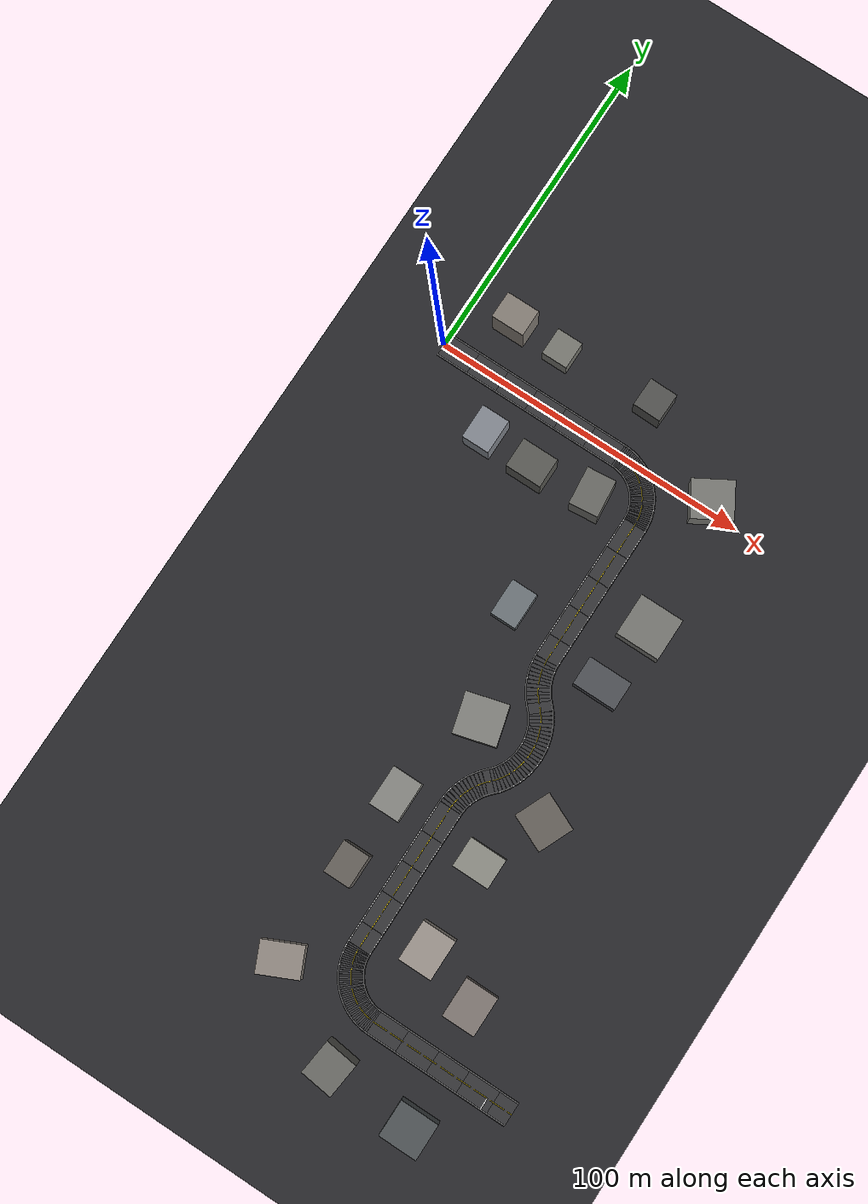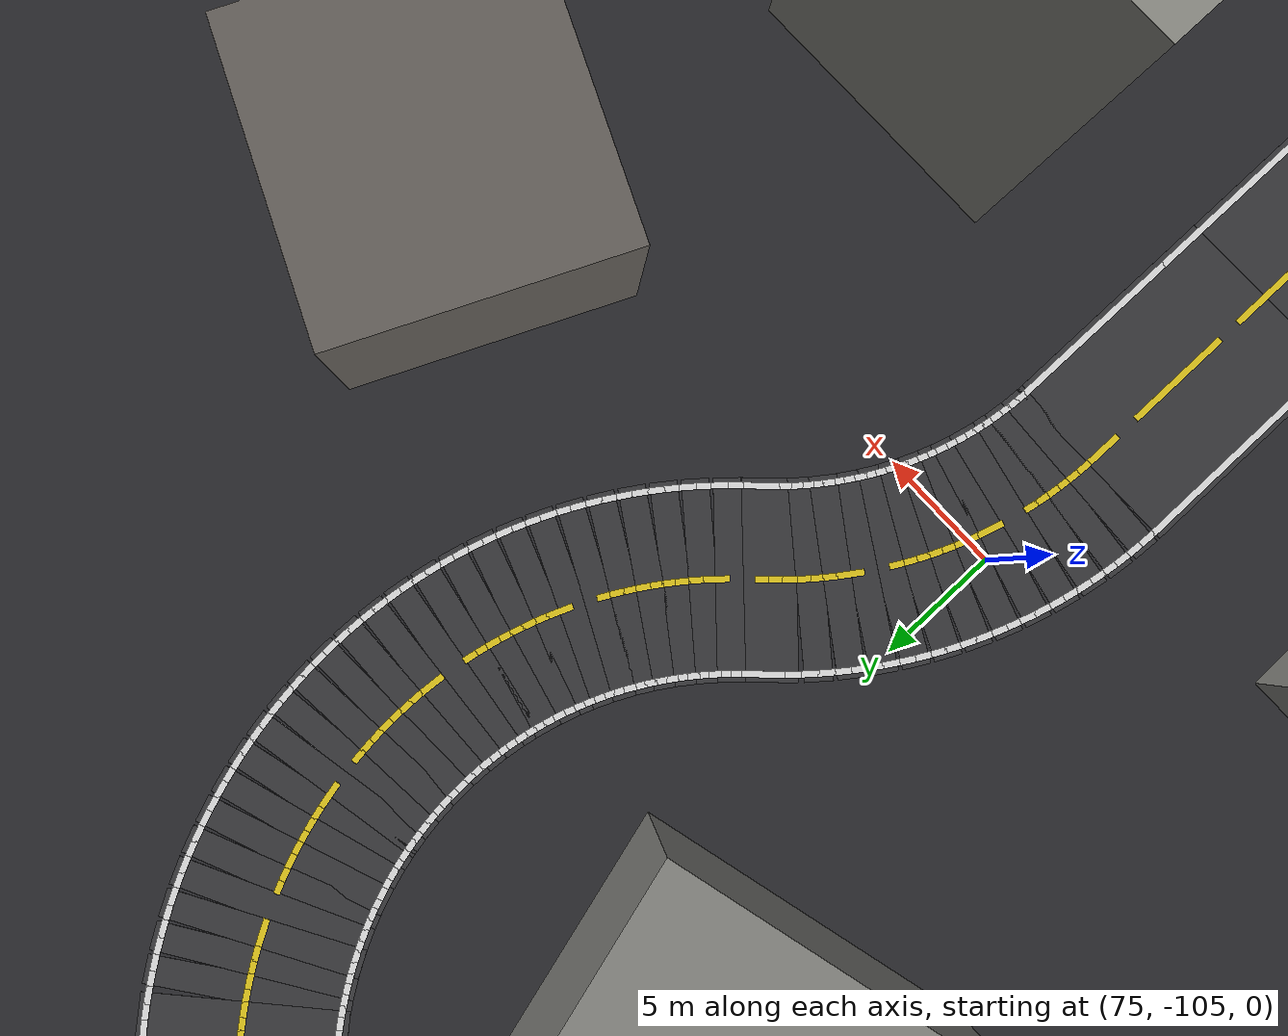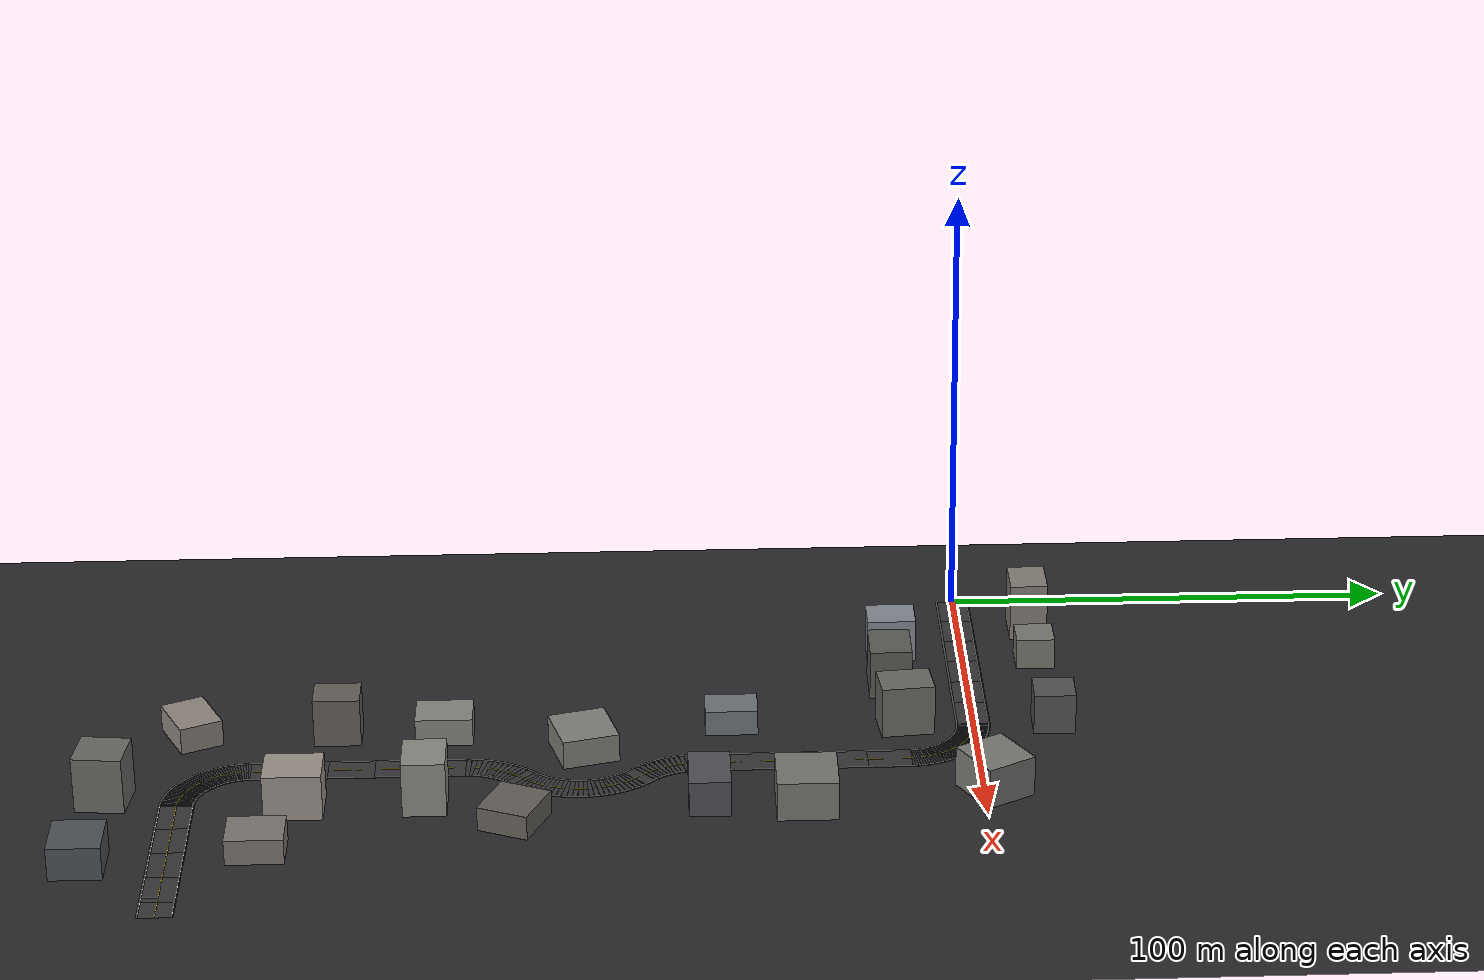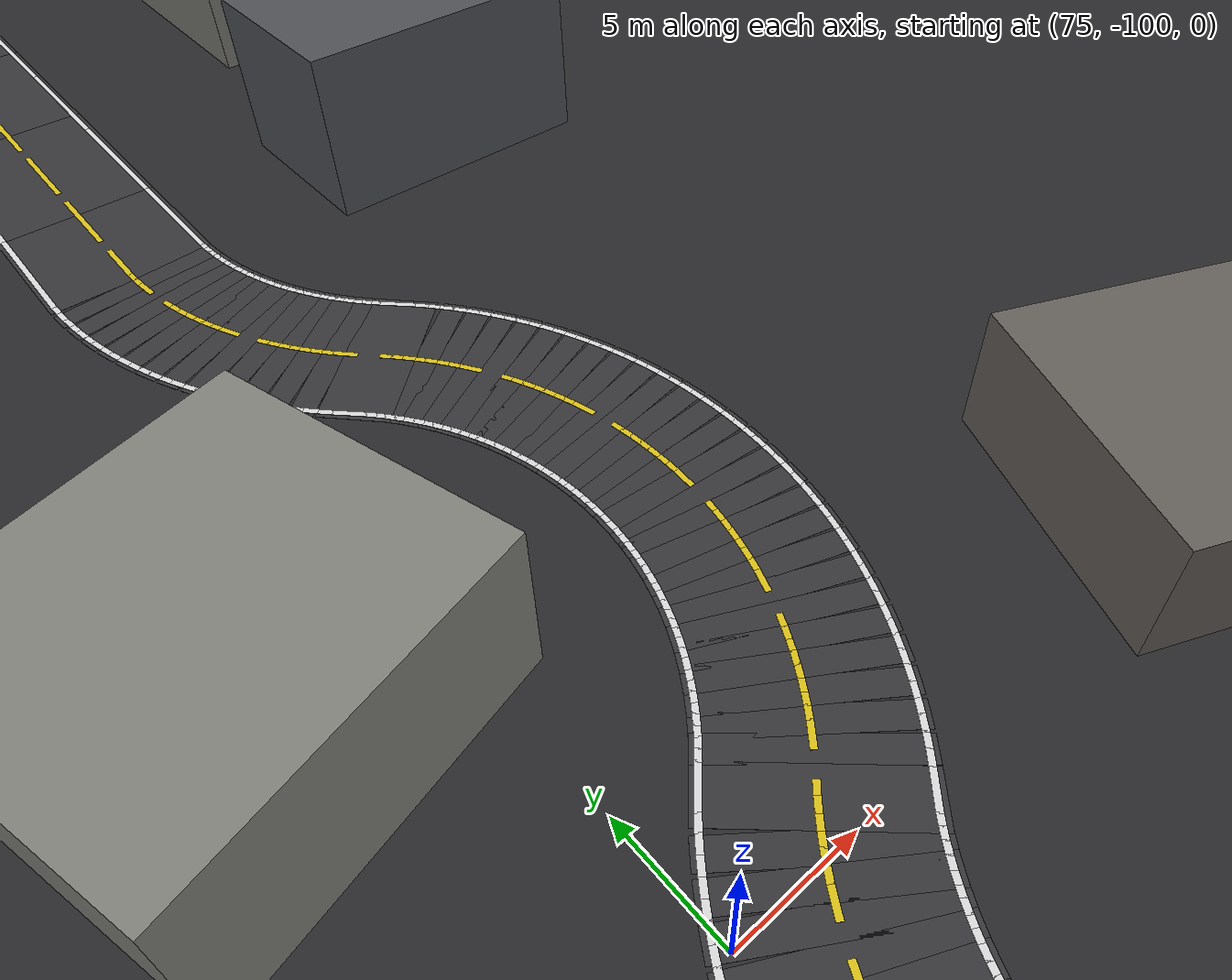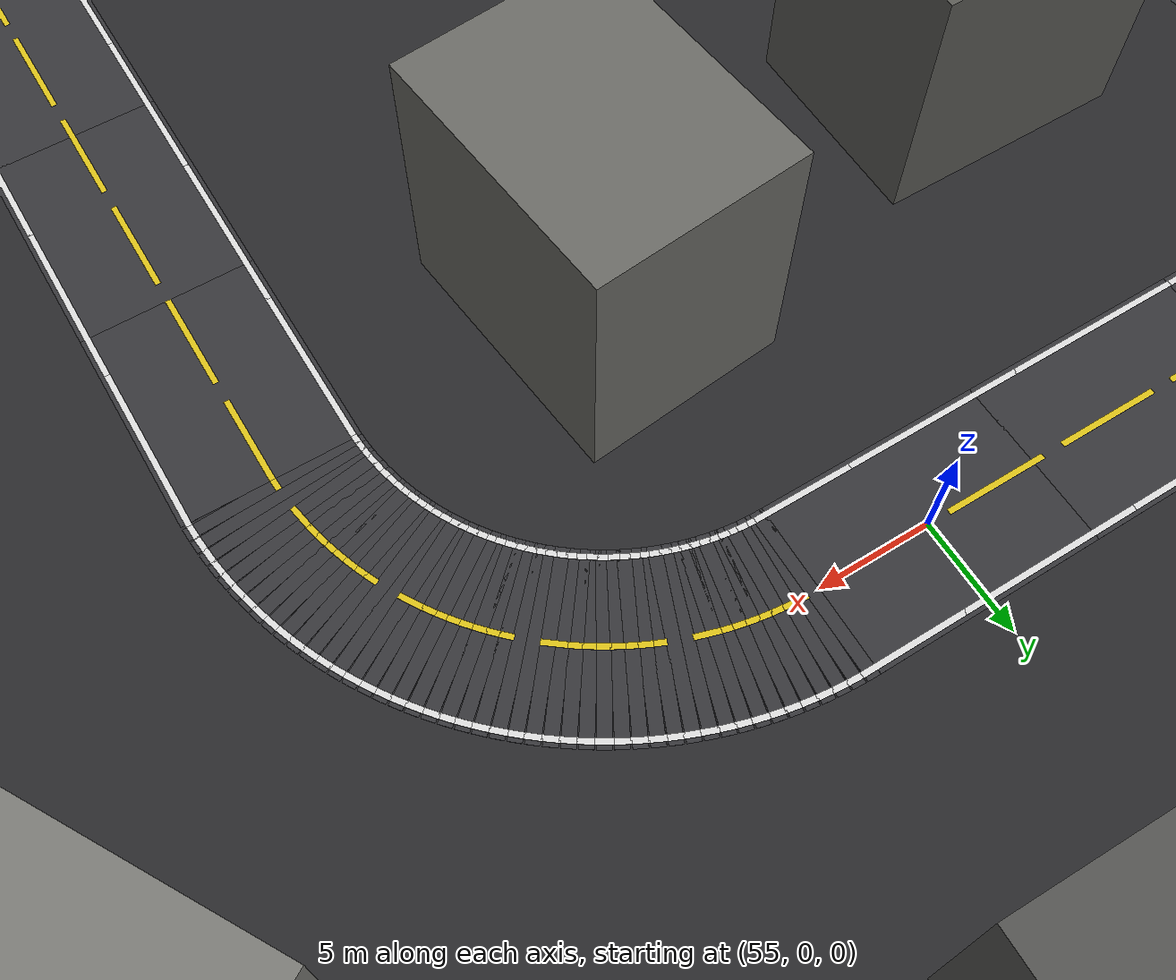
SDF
<sdf version="1.7">
 <world name="urban_course">
  <physics type="ode"><max_step_size>0.004</max_step_size><real_time_factor>1.0</real_time_factor></physics>
  <plugin filename="libignition-gazebo-physics-system.so" name="ignition::gazebo::systems::Physics"/>
  <plugin filename="libignition-gazebo-user-commands-system.so" name="ignition::gazebo::systems::UserCommands"/>
  <plugin filename="libignition-gazebo-scene-broadcaster-system.so" name="ignition::gazebo::systems::SceneBroadcaster"/>
  <plugin filename="libignition-gazebo-sensors-system.so" name="ignition::gazebo::systems::Sensors">
   <render_engine>ogre2</render_engine>
  </plugin>
  <plugin filename="libignition-gazebo-imu-system.so" name="ignition::gazebo::systems::Imu"/>
  <scene><ambient>0.4 0.4 0.4 1</ambient><background>0.55 0.7 0.9 1</background><shadows>false</shadows></scene>
  <light type="directional" name="sun">
   <cast_shadows>false</cast_shadows>
   <pose>0 0 30 0 0 0</pose>
   <diffuse>0.9 0.9 0.9 1</diffuse>
   <specular>0.2 0.2 0.2 1</specular>
   <direction>-0.3 0.2 -0.9</direction>
  </light>
  <model name="ground">
   <static>true</static>
   <pose>67.5 -85.5 0 0 0 0</pose>
   <link name="l">
    <collision name="c"><geometry><plane><normal>0 0 1</normal><size>195 231</size></plane></geometry></collision>
    <visual name="v">
     <geometry><plane><normal>0 0 1</normal><size>195 231</size></plane></geometry>
     <material><ambient>0.16 0.16 0.17 1</ambient><diffuse>0.16 0.16 0.17 1</diffuse></material>
    </visual>
   </link>
  </model>
  <model name="road">
   <static>true</static>
   <link name="l">
    <visual name="asfalt_0001">
     <pose>5.000 0.000 0.003 0 0 0.0000</pose>
     <geometry><box><size>10.060 7.600 0.006</size></box></geometry>
     <material><ambient>0.21 0.21 0.22 1</ambient><diffuse>0.21 0.21 0.22 1</diffuse></material>
    </visual>
    <visual name="asfalt_0002">
     <pose>15.000 0.000 0.003 0 0 0.0000</pose>
     <geometry><box><size>10.060 7.600 0.006</size></box></geometry>
     <material><ambient>0.21 0.21 0.22 1</ambient><diffuse>0.21 0.21 0.22 1</diffuse></material>
    </visual>
    <visual name="asfalt_0003">
     <pose>25.000 0.000 0.003 0 0 0.0000</pose>
     <geometry><box><size>10.060 7.600 0.006</size></box></geometry>
     <material><ambient>0.21 0.21 0.22 1</ambient><diffuse>0.21 0.21 0.22 1</diffuse></material>
    </visual>
    <visual name="asfalt_0004">
     <pose>35.000 0.000 0.003 0 0 0.0000</pose>
     <geometry><box><size>10.060 7.600 0.006</size></box></geometry>
     <material><ambient>0.21 0.21 0.22 1</ambient><diffuse>0.21 0.21 0.22 1</diffuse></material>
    </visual>
    <visual name="asfalt_0005">
     <pose>45.000 0.000 0.003 0 0 0.0000</pose>
     <geometry><box><size>10.060 7.600 0.006</size></box></geometry>
     <material><ambient>0.21 0.21 0.22 1</ambient><diffuse>0.21 0.21 0.22 1</diffuse></material>
    </visual>
    <visual name="asfalt_0006">
     <pose>55.000 0.000 0.003 0 0 0.0000</pose>
     <geometry><box><size>10.060 7.600 0.006</size></box></geometry>
     <material><ambient>0.21 0.21 0.22 1</ambient><diffuse>0.21 0.21 0.22 1</diffuse></material>
    </visual>
    <visual name="asfalt_0007">
     <pose>60.251 -0.004 0.003 0 0 -0.0167</pose>
     <geometry><box><size>0.561 7.600 0.006</size></box></geometry>
     <material><ambient>0.21 0.21 0.22 1</ambient><diffuse>0.21 0.21 0.22 1</diffuse></material>
    </visual>
    <visual name="asfalt_0008">
     <pose>60.752 -0.021 0.003 0 0 -0.0501</pose>
     <geometry><box><size>0.561 7.600 0.006</size></box></geometry>
     <material><ambient>0.21 0.21 0.22 1</ambient><diffuse>0.21 0.21 0.22 1</diffuse></material>
    </visual>
    <visual name="asfalt_0009">
     <pose>61.252 -0.054 0.003 0 0 -0.0836</pose>
     <geometry><box><size>0.561 7.600 0.006</size></box></geometry>
     <material><ambient>0.21 0.21 0.22 1</ambient><diffuse>0.21 0.21 0.22 1</diffuse></material>
    </visual>
    <visual name="asfalt_0010">
     <pose>61.750 -0.105 0.003 0 0 -0.1170</pose>
     <geometry><box><size>0.561 7.600 0.006</size></box></geometry>
     <material><ambient>0.21 0.21 0.22 1</ambient><diffuse>0.21 0.21 0.22 1</diffuse></material>
    </visual>
    <visual name="asfalt_0011">
     <pose>62.247 -0.171 0.003 0 0 -0.1504</pose>
     <geometry><box><size>0.561 7.600 0.006</size></box></geometry>
     <material><ambient>0.21 0.21 0.22 1</ambient><diffuse>0.21 0.21 0.22 1</diffuse></material>
    </visual>
    <visual name="asfalt_0012">
     <pose>62.741 -0.255 0.003 0 0 -0.1838</pose>
     <geometry><box><size>0.561 7.600 0.006</size></box></geometry>
     <material><ambient>0.21 0.21 0.22 1</ambient><diffuse>0.21 0.21 0.22 1</diffuse></material>
    </visual>
    <visual name="asfalt_0013">
     <pose>63.233 -0.355 0.003 0 0 -0.2172</pose>
     <geometry><box><size>0.561 7.600 0.006</size></box></geometry>
     <material><ambient>0.21 0.21 0.22 1</ambient><diffuse>0.21 0.21 0.22 1</diffuse></material>
    </visual>
    <visual name="asfalt_0014">
     <pose>63.720 -0.471 0.003 0 0 -0.2507</pose>
     <geometry><box><size>0.561 7.600 0.006</size></box></geometry>
     <material><ambient>0.21 0.21 0.22 1</ambient><diffuse>0.21 0.21 0.22 1</diffuse></material>
    </visual>
    <visual name="asfalt_0015">
     <pose>64.204 -0.603 0.003 0 0 -0.2841</pose>
     <geometry><box><size>0.561 7.600 0.006</size></box></geometry>
     <material><ambient>0.21 0.21 0.22 1</ambient><diffuse>0.21 0.21 0.22 1</diffuse></material>
    </visual>
    <visual name="asfalt_0016">
     <pose>64.682 -0.752 0.003 0 0 -0.3175</pose>
     <geometry><box><size>0.561 7.600 0.006</size></box></geometry>
     <material><ambient>0.21 0.21 0.22 1</ambient><diffuse>0.21 0.21 0.22 1</diffuse></material>
    </visual>
    <visual name="asfalt_0017">
     <pose>65.156 -0.916 0.003 0 0 -0.3509</pose>
     <geometry><box><size>0.561 7.600 0.006</size></box></geometry>
     <material><ambient>0.21 0.21 0.22 1</ambient><diffuse>0.21 0.21 0.22 1</diffuse></material>
    </visual>
    <visual name="asfalt_0018">
     <pose>65.623 -1.096 0.003 0 0 -0.3843</pose>
     <geometry><box><size>0.561 7.600 0.006</size></box></geometry>
     <material><ambient>0.21 0.21 0.22 1</ambient><diffuse>0.21 0.21 0.22 1</diffuse></material>
    </visual>
    <visual name="asfalt_0019">
     <pose>66.085 -1.292 0.003 0 0 -0.4178</pose>
     <geometry><box><size>0.561 7.600 0.006</size></box></geometry>
     <material><ambient>0.21 0.21 0.22 1</ambient><diffuse>0.21 0.21 0.22 1</diffuse></material>
    </visual>
    <visual name="asfalt_0020">
     <pose>66.540 -1.503 0.003 0 0 -0.4512</pose>
     <geometry><box><size>0.561 7.600 0.006</size></box></geometry>
     <material><ambient>0.21 0.21 0.22 1</ambient><diffuse>0.21 0.21 0.22 1</diffuse></material>
    </visual>
    <visual name="asfalt_0021">
     <pose>66.987 -1.729 0.003 0 0 -0.4846</pose>
     <geometry><box><size>0.561 7.600 0.006</size></box></geometry>
     <material><ambient>0.21 0.21 0.22 1</ambient><diffuse>0.21 0.21 0.22 1</diffuse></material>
    </visual>
    <visual name="asfalt_0022">
     <pose>67.426 -1.970 0.003 0 0 -0.5180</pose>
     <geometry><box><size>0.561 7.600 0.006</size></box></geometry>
     <material><ambient>0.21 0.21 0.22 1</ambient><diffuse>0.21 0.21 0.22 1</diffuse></material>
    </visual>
    <visual name="asfalt_0023">
     <pose>67.858 -2.225 0.003 0 0 -0.5514</pose>
     <geometry><box><size>0.561 7.600 0.006</size></box></geometry>
     <material><ambient>0.21 0.21 0.22 1</ambient><diffuse>0.21 0.21 0.22 1</diffuse></material>
    </visual>
    <visual name="asfalt_0024">
     <pose>68.280 -2.495 0.003 0 0 -0.5849</pose>
     <geometry><box><size>0.561 7.600 0.006</size></box></geometry>
     <material><ambient>0.21 0.21 0.22 1</ambient><diffuse>0.21 0.21 0.22 1</diffuse></material>
    </visual>
    <visual name="asfalt_0025">
     <pose>68.693 -2.779 0.003 0 0 -0.6183</pose>
     <geometry><box><size>0.561 7.600 0.006</size></box></geometry>
     <material><ambient>0.21 0.21 0.22 1</ambient><diffuse>0.21 0.21 0.22 1</diffuse></material>
    </visual>
    <visual name="asfalt_0026">
     <pose>69.097 -3.076 0.003 0 0 -0.6517</pose>
     <geometry><box><size>0.561 7.600 0.006</size></box></geometry>
     <material><ambient>0.21 0.21 0.22 1</ambient><diffuse>0.21 0.21 0.22 1</diffuse></material>
    </visual>
    <visual name="asfalt_0027">
     <pose>69.490 -3.387 0.003 0 0 -0.6851</pose>
     <geometry><box><size>0.561 7.600 0.006</size></box></geometry>
     <material><ambient>0.21 0.21 0.22 1</ambient><diffuse>0.21 0.21 0.22 1</diffuse></material>
    </visual>
    <visual name="asfalt_0028">
     <pose>69.873 -3.710 0.003 0 0 -0.7186</pose>
     <geometry><box><size>0.561 7.600 0.006</size></box></geometry>
     <material><ambient>0.21 0.21 0.22 1</ambient><diffuse>0.21 0.21 0.22 1</diffuse></material>
    </visual>
    <visual name="asfalt_0029">
     <pose>70.245 -4.046 0.003 0 0 -0.7520</pose>
     <geometry><box><size>0.561 7.600 0.006</size></box></geometry>
     <material><ambient>0.21 0.21 0.22 1</ambient><diffuse>0.21 0.21 0.22 1</diffuse></material>
    </visual>
    <visual name="asfalt_0030">
     <pose>70.605 -4.395 0.003 0 0 -0.7854</pose>
     <geometry><box><size>0.561 7.600 0.006</size></box></geometry>
     <material><ambient>0.21 0.21 0.22 1</ambient><diffuse>0.21 0.21 0.22 1</diffuse></material>
    </visual>
    <visual name="asfalt_0031">
     <pose>70.954 -4.755 0.003 0 0 -0.8188</pose>
     <geometry><box><size>0.561 7.600 0.006</size></box></geometry>
     <material><ambient>0.21 0.21 0.22 1</ambient><diffuse>0.21 0.21 0.22 1</diffuse></material>
    </visual>
    <visual name="asfalt_0032">
     <pose>71.290 -5.127 0.003 0 0 -0.8522</pose>
     <geometry><box><size>0.561 7.600 0.006</size></box></geometry>
     <material><ambient>0.21 0.21 0.22 1</ambient><diffuse>0.21 0.21 0.22 1</diffuse></material>
    </visual>
    <visual name="asfalt_0033">
     <pose>71.613 -5.510 0.003 0 0 -0.8857</pose>
     <geometry><box><size>0.561 7.600 0.006</size></box></geometry>
     <material><ambient>0.21 0.21 0.22 1</ambient><diffuse>0.21 0.21 0.22 1</diffuse></material>
    </visual>
    <visual name="asfalt_0034">
     <pose>71.924 -5.903 0.003 0 0 -0.9191</pose>
     <geometry><box><size>0.561 7.600 0.006</size></box></geometry>
     <material><ambient>0.21 0.21 0.22 1</ambient><diffuse>0.21 0.21 0.22 1</diffuse></material>
    </visual>
    <visual name="asfalt_0035">
     <pose>72.221 -6.307 0.003 0 0 -0.9525</pose>
     <geometry><box><size>0.561 7.600 0.006</size></box></geometry>
     <material><ambient>0.21 0.21 0.22 1</ambient><diffuse>0.21 0.21 0.22 1</diffuse></material>
    </visual>
    <visual name="asfalt_0036">
     <pose>72.505 -6.720 0.003 0 0 -0.9859</pose>
     <geometry><box><size>0.561 7.600 0.006</size></box></geometry>
     <material><ambient>0.21 0.21 0.22 1</ambient><diffuse>0.21 0.21 0.22 1</diffuse></material>
    </visual>
    <visual name="asfalt_0037">
     <pose>72.775 -7.142 0.003 0 0 -1.0193</pose>
     <geometry><box><size>0.561 7.600 0.006</size></box></geometry>
     <material><ambient>0.21 0.21 0.22 1</ambient><diffuse>0.21 0.21 0.22 1</diffuse></material>
    </visual>
    <visual name="asfalt_0038">
     <pose>73.030 -7.574 0.003 0 0 -1.0528</pose>
     <geometry><box><size>0.561 7.600 0.006</size></box></geometry>
     <material><ambient>0.21 0.21 0.22 1</ambient><diffuse>0.21 0.21 0.22 1</diffuse></material>
    </visual>
    <visual name="asfalt_0039">
     <pose>73.271 -8.013 0.003 0 0 -1.0862</pose>
     <geometry><box><size>0.561 7.600 0.006</size></box></geometry>
     <material><ambient>0.21 0.21 0.22 1</ambient><diffuse>0.21 0.21 0.22 1</diffuse></material>
    </visual>
    <visual name="asfalt_0040">
     <pose>73.497 -8.460 0.003 0 0 -1.1196</pose>
     <geometry><box><size>0.561 7.600 0.006</size></box></geometry>
     <material><ambient>0.21 0.21 0.22 1</ambient><diffuse>0.21 0.21 0.22 1</diffuse></material>
    </visual>
    <visual name="asfalt_0041">
     <pose>73.708 -8.915 0.003 0 0 -1.1530</pose>
     <geometry><box><size>0.561 7.600 0.006</size></box></geometry>
     <material><ambient>0.21 0.21 0.22 1</ambient><diffuse>0.21 0.21 0.22 1</diffuse></material>
    </visual>
    <visual name="asfalt_0042">
     <pose>73.904 -9.377 0.003 0 0 -1.1865</pose>
     <geometry><box><size>0.561 7.600 0.006</size></box></geometry>
     <material><ambient>0.21 0.21 0.22 1</ambient><diffuse>0.21 0.21 0.22 1</diffuse></material>
    </visual>
    <visual name="asfalt_0043">
     <pose>74.084 -9.844 0.003 0 0 -1.2199</pose>
     <geometry><box><size>0.561 7.600 0.006</size></box></geometry>
     <material><ambient>0.21 0.21 0.22 1</ambient><diffuse>0.21 0.21 0.22 1</diffuse></material>
    </visual>
    <visual name="asfalt_0044">
     <pose>74.248 -10.318 0.003 0 0 -1.2533</pose>
     <geometry><box><size>0.561 7.600 0.006</size></box></geometry>
     <material><ambient>0.21 0.21 0.22 1</ambient><diffuse>0.21 0.21 0.22 1</diffuse></material>
    </visual>
    <visual name="asfalt_0045">
     <pose>74.397 -10.796 0.003 0 0 -1.2867</pose>
     <geometry><box><size>0.561 7.600 0.006</size></box></geometry>
     <material><ambient>0.21 0.21 0.22 1</ambient><diffuse>0.21 0.21 0.22 1</diffuse></material>
    </visual>
    <visual name="asfalt_0046">
     <pose>74.529 -11.280 0.003 0 0 -1.3201</pose>
     <geometry><box><size>0.561 7.600 0.006</size></box></geometry>
     <material><ambient>0.21 0.21 0.22 1</ambient><diffuse>0.21 0.21 0.22 1</diffuse></material>
    </visual>
    <visual name="asfalt_0047">
     <pose>74.645 -11.767 0.003 0 0 -1.3536</pose>
     <geometry><box><size>0.561 7.600 0.006</size></box></geometry>
     <material><ambient>0.21 0.21 0.22 1</ambient><diffuse>0.21 0.21 0.22 1</diffuse></material>
    </visual>
    <visual name="asfalt_0048">
     <pose>74.745 -12.259 0.003 0 0 -1.3870</pose>
     <geometry><box><size>0.561 7.600 0.006</size></box></geometry>
     <material><ambient>0.21 0.21 0.22 1</ambient><diffuse>0.21 0.21 0.22 1</diffuse></material>
    </visual>
    <visual name="asfalt_0049">
     <pose>74.829 -12.753 0.003 0 0 -1.4204</pose>
     <geometry><box><size>0.561 7.600 0.006</size></box></geometry>
     <material><ambient>0.21 0.21 0.22 1</ambient><diffuse>0.21 0.21 0.22 1</diffuse></material>
    </visual>
    <visual name="asfalt_0050">
     <pose>74.895 -13.250 0.003 0 0 -1.4538</pose>
     <geometry><box><size>0.561 7.600 0.006</size></box></geometry>
     <material><ambient>0.21 0.21 0.22 1</ambient><diffuse>0.21 0.21 0.22 1</diffuse></material>
    </visual>
    <visual name="asfalt_0051">
     <pose>74.946 -13.748 0.003 0 0 -1.4872</pose>
     <geometry><box><size>0.561 7.600 0.006</size></box></geometry>
     <material><ambient>0.21 0.21 0.22 1</ambient><diffuse>0.21 0.21 0.22 1</diffuse></material>
    </visual>
    <visual name="asfalt_0052">
     <pose>74.979 -14.248 0.003 0 0 -1.5207</pose>
     <geometry><box><size>0.561 7.600 0.006</size></box></geometry>
     <material><ambient>0.21 0.21 0.22 1</ambient><diffuse>0.21 0.21 0.22 1</diffuse></material>
    </visual>
    <visual name="asfalt_0053">
     <pose>74.996 -19.249 0.003 0 0 -1.5699</pose>
     <geometry><box><size>9.561 7.600 0.006</size></box></geometry>
     <material><ambient>0.21 0.21 0.22 1</ambient><diffuse>0.21 0.21 0.22 1</diffuse></material>
    </visual>
    <visual name="asfalt_0054">
     <pose>75.000 -29.000 0.003 0 0 -1.5708</pose>
     <geometry><box><size>10.060 7.600 0.006</size></box></geometry>
     <material><ambient>0.21 0.21 0.22 1</ambient><diffuse>0.21 0.21 0.22 1</diffuse></material>
    </visual>
    <visual name="asfalt_0055">
     <pose>75.000 -39.000 0.003 0 0 -1.5708</pose>
     <geometry><box><size>10.060 7.600 0.006</size></box></geometry>
     <material><ambient>0.21 0.21 0.22 1</ambient><diffuse>0.21 0.21 0.22 1</diffuse></material>
    </visual>
    <visual name="asfalt_0056">
     <pose>75.000 -49.000 0.003 0 0 -1.5708</pose>
     <geometry><box><size>10.060 7.600 0.006</size></box></geometry>
     <material><ambient>0.21 0.21 0.22 1</ambient><diffuse>0.21 0.21 0.22 1</diffuse></material>
    </visual>
    <visual name="asfalt_0057">
     <pose>75.014 -57.505 0.003 0 0 -1.5668</pose>
     <geometry><box><size>7.069 7.600 0.006</size></box></geometry>
     <material><ambient>0.21 0.21 0.22 1</ambient><diffuse>0.21 0.21 0.22 1</diffuse></material>
    </visual>
    <visual name="asfalt_0058">
     <pose>75.071 -61.512 0.003 0 0 -1.4866</pose>
     <geometry><box><size>1.070 7.600 0.006</size></box></geometry>
     <material><ambient>0.21 0.21 0.22 1</ambient><diffuse>0.21 0.21 0.22 1</diffuse></material>
    </visual>
    <visual name="asfalt_0059">
     <pose>75.184 -62.515 0.003 0 0 -1.4305</pose>
     <geometry><box><size>1.070 7.600 0.006</size></box></geometry>
     <material><ambient>0.21 0.21 0.22 1</ambient><diffuse>0.21 0.21 0.22 1</diffuse></material>
    </visual>
    <visual name="asfalt_0060">
     <pose>75.353 -63.510 0.003 0 0 -1.3744</pose>
     <geometry><box><size>1.070 7.600 0.006</size></box></geometry>
     <material><ambient>0.21 0.21 0.22 1</ambient><diffuse>0.21 0.21 0.22 1</diffuse></material>
    </visual>
    <visual name="asfalt_0061">
     <pose>75.577 -64.494 0.003 0 0 -1.3183</pose>
     <geometry><box><size>1.070 7.600 0.006</size></box></geometry>
     <material><ambient>0.21 0.21 0.22 1</ambient><diffuse>0.21 0.21 0.22 1</diffuse></material>
    </visual>
    <visual name="asfalt_0062">
     <pose>75.857 -65.464 0.003 0 0 -1.2622</pose>
     <geometry><box><size>1.070 7.600 0.006</size></box></geometry>
     <material><ambient>0.21 0.21 0.22 1</ambient><diffuse>0.21 0.21 0.22 1</diffuse></material>
    </visual>
    <visual name="asfalt_0063">
     <pose>76.190 -66.417 0.003 0 0 -1.2061</pose>
     <geometry><box><size>1.070 7.600 0.006</size></box></geometry>
     <material><ambient>0.21 0.21 0.22 1</ambient><diffuse>0.21 0.21 0.22 1</diffuse></material>
    </visual>
    <visual name="asfalt_0064">
     <pose>76.576 -67.349 0.003 0 0 -1.1500</pose>
     <geometry><box><size>1.070 7.600 0.006</size></box></geometry>
     <material><ambient>0.21 0.21 0.22 1</ambient><diffuse>0.21 0.21 0.22 1</diffuse></material>
    </visual>
    <visual name="asfalt_0065">
     <pose>77.014 -68.258 0.003 0 0 -1.0939</pose>
     <geometry><box><size>1.070 7.600 0.006</size></box></geometry>
     <material><ambient>0.21 0.21 0.22 1</ambient><diffuse>0.21 0.21 0.22 1</diffuse></material>
    </visual>
    <visual name="asfalt_0066">
     <pose>77.502 -69.142 0.003 0 0 -1.0378</pose>
     <geometry><box><size>1.070 7.600 0.006</size></box></geometry>
     <material><ambient>0.21 0.21 0.22 1</ambient><diffuse>0.21 0.21 0.22 1</diffuse></material>
    </visual>
    <visual name="asfalt_0067">
     <pose>78.039 -69.996 0.003 0 0 -0.9817</pose>
     <geometry><box><size>1.070 7.600 0.006</size></box></geometry>
     <material><ambient>0.21 0.21 0.22 1</ambient><diffuse>0.21 0.21 0.22 1</diffuse></material>
    </visual>
    <visual name="asfalt_0068">
     <pose>78.623 -70.819 0.003 0 0 -0.9256</pose>
     <geometry><box><size>1.070 7.600 0.006</size></box></geometry>
     <material><ambient>0.21 0.21 0.22 1</ambient><diffuse>0.21 0.21 0.22 1</diffuse></material>
    </visual>
    <visual name="asfalt_0069">
     <pose>79.253 -71.609 0.003 0 0 -0.8695</pose>
     <geometry><box><size>1.070 7.600 0.006</size></box></geometry>
     <material><ambient>0.21 0.21 0.22 1</ambient><diffuse>0.21 0.21 0.22 1</diffuse></material>
    </visual>
    <visual name="asfalt_0070">
     <pose>80.587 -73.100 0.003 0 0 -0.8314</pose>
     <geometry><box><size>3.053 7.600 0.006</size></box></geometry>
     <material><ambient>0.21 0.21 0.22 1</ambient><diffuse>0.21 0.21 0.22 1</diffuse></material>
    </visual>
    <visual name="asfalt_0071">
     <pose>81.894 -74.601 0.003 0 0 -0.9232</pose>
     <geometry><box><size>1.052 7.600 0.006</size></box></geometry>
     <material><ambient>0.21 0.21 0.22 1</ambient><diffuse>0.21 0.21 0.22 1</diffuse></material>
    </visual>
    <visual name="asfalt_0072">
     <pose>82.470 -75.408 0.003 0 0 -0.9783</pose>
     <geometry><box><size>1.052 7.600 0.006</size></box></geometry>
     <material><ambient>0.21 0.21 0.22 1</ambient><diffuse>0.21 0.21 0.22 1</diffuse></material>
    </visual>
    <visual name="asfalt_0073">
     <pose>83.001 -76.245 0.003 0 0 -1.0334</pose>
     <geometry><box><size>1.052 7.600 0.006</size></box></geometry>
     <material><ambient>0.21 0.21 0.22 1</ambient><diffuse>0.21 0.21 0.22 1</diffuse></material>
    </visual>
    <visual name="asfalt_0074">
     <pose>83.485 -77.111 0.003 0 0 -1.0885</pose>
     <geometry><box><size>1.052 7.600 0.006</size></box></geometry>
     <material><ambient>0.21 0.21 0.22 1</ambient><diffuse>0.21 0.21 0.22 1</diffuse></material>
    </visual>
    <visual name="asfalt_0075">
     <pose>83.921 -78.002 0.003 0 0 -1.1436</pose>
     <geometry><box><size>1.052 7.600 0.006</size></box></geometry>
     <material><ambient>0.21 0.21 0.22 1</ambient><diffuse>0.21 0.21 0.22 1</diffuse></material>
    </visual>
    <visual name="asfalt_0076">
     <pose>84.306 -78.915 0.003 0 0 -1.1988</pose>
     <geometry><box><size>1.052 7.600 0.006</size></box></geometry>
     <material><ambient>0.21 0.21 0.22 1</ambient><diffuse>0.21 0.21 0.22 1</diffuse></material>
    </visual>
    <visual name="asfalt_0077">
     <pose>84.641 -79.849 0.003 0 0 -1.2539</pose>
     <geometry><box><size>1.052 7.600 0.006</size></box></geometry>
     <material><ambient>0.21 0.21 0.22 1</ambient><diffuse>0.21 0.21 0.22 1</diffuse></material>
    </visual>
    <visual name="asfalt_0078">
     <pose>84.924 -80.799 0.003 0 0 -1.3090</pose>
     <geometry><box><size>1.052 7.600 0.006</size></box></geometry>
     <material><ambient>0.21 0.21 0.22 1</ambient><diffuse>0.21 0.21 0.22 1</diffuse></material>
    </visual>
    <visual name="asfalt_0079">
     <pose>85.154 -81.763 0.003 0 0 -1.3641</pose>
     <geometry><box><size>1.052 7.600 0.006</size></box></geometry>
     <material><ambient>0.21 0.21 0.22 1</ambient><diffuse>0.21 0.21 0.22 1</diffuse></material>
    </visual>
    <visual name="asfalt_0080">
     <pose>85.331 -82.739 0.003 0 0 -1.4192</pose>
     <geometry><box><size>1.052 7.600 0.006</size></box></geometry>
     <material><ambient>0.21 0.21 0.22 1</ambient><diffuse>0.21 0.21 0.22 1</diffuse></material>
    </visual>
    <visual name="asfalt_0081">
     <pose>85.454 -83.723 0.003 0 0 -1.4743</pose>
     <geometry><box><size>1.052 7.600 0.006</size></box></geometry>
     <material><ambient>0.21 0.21 0.22 1</ambient><diffuse>0.21 0.21 0.22 1</diffuse></material>
    </visual>
    <visual name="asfalt_0082">
     <pose>85.522 -84.712 0.003 0 0 -1.5295</pose>
     <geometry><box><size>1.052 7.600 0.006</size></box></geometry>
     <material><ambient>0.21 0.21 0.22 1</ambient><diffuse>0.21 0.21 0.22 1</diffuse></material>
    </visual>
    <visual name="asfalt_0083">
     <pose>85.536 -85.704 0.003 0 0 -1.5846</pose>
     <geometry><box><size>1.052 7.600 0.006</size></box></geometry>
     <material><ambient>0.21 0.21 0.22 1</ambient><diffuse>0.21 0.21 0.22 1</diffuse></material>
    </visual>
    <visual name="asfalt_0084">
     <pose>85.495 -86.694 0.003 0 0 -1.6397</pose>
     <geometry><box><size>1.052 7.600 0.006</size></box></geometry>
     <material><ambient>0.21 0.21 0.22 1</ambient><diffuse>0.21 0.21 0.22 1</diffuse></material>
    </visual>
    <visual name="asfalt_0085">
     <pose>85.399 -87.681 0.003 0 0 -1.6948</pose>
     <geometry><box><size>1.052 7.600 0.006</size></box></geometry>
     <material><ambient>0.21 0.21 0.22 1</ambient><diffuse>0.21 0.21 0.22 1</diffuse></material>
    </visual>
    <visual name="asfalt_0086">
     <pose>85.249 -88.662 0.003 0 0 -1.7499</pose>
     <geometry><box><size>1.052 7.600 0.006</size></box></geometry>
     <material><ambient>0.21 0.21 0.22 1</ambient><diffuse>0.21 0.21 0.22 1</diffuse></material>
    </visual>
    <visual name="asfalt_0087">
     <pose>85.046 -89.632 0.003 0 0 -1.8050</pose>
     <geometry><box><size>1.052 7.600 0.006</size></box></geometry>
     <material><ambient>0.21 0.21 0.22 1</ambient><diffuse>0.21 0.21 0.22 1</diffuse></material>
    </visual>
    <visual name="asfalt_0088">
     <pose>84.789 -90.590 0.003 0 0 -1.8602</pose>
     <geometry><box><size>1.052 7.600 0.006</size></box></geometry>
     <material><ambient>0.21 0.21 0.22 1</ambient><diffuse>0.21 0.21 0.22 1</diffuse></material>
    </visual>
    <visual name="asfalt_0089">
     <pose>84.480 -91.532 0.003 0 0 -1.9153</pose>
     <geometry><box><size>1.052 7.600 0.006</size></box></geometry>
     <material><ambient>0.21 0.21 0.22 1</ambient><diffuse>0.21 0.21 0.22 1</diffuse></material>
    </visual>
    <visual name="asfalt_0090">
     <pose>84.120 -92.456 0.003 0 0 -1.9704</pose>
     <geometry><box><size>1.052 7.600 0.006</size></box></geometry>
     <material><ambient>0.21 0.21 0.22 1</ambient><diffuse>0.21 0.21 0.22 1</diffuse></material>
    </visual>
    <visual name="asfalt_0091">
     <pose>83.709 -93.358 0.003 0 0 -2.0255</pose>
     <geometry><box><size>1.052 7.600 0.006</size></box></geometry>
     <material><ambient>0.21 0.21 0.22 1</ambient><diffuse>0.21 0.21 0.22 1</diffuse></material>
    </visual>
    <visual name="asfalt_0092">
     <pose>83.249 -94.237 0.003 0 0 -2.0806</pose>
     <geometry><box><size>1.052 7.600 0.006</size></box></geometry>
     <material><ambient>0.21 0.21 0.22 1</ambient><diffuse>0.21 0.21 0.22 1</diffuse></material>
    </visual>
    <visual name="asfalt_0093">
     <pose>82.742 -95.089 0.003 0 0 -2.1357</pose>
     <geometry><box><size>1.052 7.600 0.006</size></box></geometry>
     <material><ambient>0.21 0.21 0.22 1</ambient><diffuse>0.21 0.21 0.22 1</diffuse></material>
    </visual>
    <visual name="asfalt_0094">
     <pose>82.188 -95.911 0.003 0 0 -2.1908</pose>
     <geometry><box><size>1.052 7.600 0.006</size></box></geometry>
     <material><ambient>0.21 0.21 0.22 1</ambient><diffuse>0.21 0.21 0.22 1</diffuse></material>
    </visual>
    <visual name="asfalt_0095">
     <pose>81.590 -96.702 0.003 0 0 -2.2460</pose>
     <geometry><box><size>1.052 7.600 0.006</size></box></geometry>
     <material><ambient>0.21 0.21 0.22 1</ambient><diffuse>0.21 0.21 0.22 1</diffuse></material>
    </visual>
    <visual name="asfalt_0096">
     <pose>80.949 -97.459 0.003 0 0 -2.3011</pose>
     <geometry><box><size>1.052 7.600 0.006</size></box></geometry>
     <material><ambient>0.21 0.21 0.22 1</ambient><diffuse>0.21 0.21 0.22 1</diffuse></material>
    </visual>
    <visual name="asfalt_0097">
     <pose>79.933 -98.563 0.003 0 0 -2.3211</pose>
     <geometry><box><size>2.070 7.600 0.006</size></box></geometry>
     <material><ambient>0.21 0.21 0.22 1</ambient><diffuse>0.21 0.21 0.22 1</diffuse></material>
    </visual>
    <visual name="asfalt_0098">
     <pose>78.933 -99.693 0.003 0 0 -2.2440</pose>
     <geometry><box><size>1.070 7.600 0.006</size></box></geometry>
     <material><ambient>0.21 0.21 0.22 1</ambient><diffuse>0.21 0.21 0.22 1</diffuse></material>
    </visual>
    <visual name="asfalt_0099">
     <pose>78.326 -100.500 0.003 0 0 -2.1879</pose>
     <geometry><box><size>1.070 7.600 0.006</size></box></geometry>
     <material><ambient>0.21 0.21 0.22 1</ambient><diffuse>0.21 0.21 0.22 1</diffuse></material>
    </visual>
    <visual name="asfalt_0100">
     <pose>77.765 -101.339 0.003 0 0 -2.1318</pose>
     <geometry><box><size>1.070 7.600 0.006</size></box></geometry>
     <material><ambient>0.21 0.21 0.22 1</ambient><diffuse>0.21 0.21 0.22 1</diffuse></material>
    </visual>
    <visual name="asfalt_0101">
     <pose>77.252 -102.208 0.003 0 0 -2.0757</pose>
     <geometry><box><size>1.070 7.600 0.006</size></box></geometry>
     <material><ambient>0.21 0.21 0.22 1</ambient><diffuse>0.21 0.21 0.22 1</diffuse></material>
    </visual>
    <visual name="asfalt_0102">
     <pose>76.789 -103.105 0.003 0 0 -2.0196</pose>
     <geometry><box><size>1.070 7.600 0.006</size></box></geometry>
     <material><ambient>0.21 0.21 0.22 1</ambient><diffuse>0.21 0.21 0.22 1</diffuse></material>
    </visual>
    <visual name="asfalt_0103">
     <pose>76.377 -104.026 0.003 0 0 -1.9635</pose>
     <geometry><box><size>1.070 7.600 0.006</size></box></geometry>
     <material><ambient>0.21 0.21 0.22 1</ambient><diffuse>0.21 0.21 0.22 1</diffuse></material>
    </visual>
    <visual name="asfalt_0104">
     <pose>76.017 -104.969 0.003 0 0 -1.9074</pose>
     <geometry><box><size>1.070 7.600 0.006</size></box></geometry>
     <material><ambient>0.21 0.21 0.22 1</ambient><diffuse>0.21 0.21 0.22 1</diffuse></material>
    </visual>
    <visual name="asfalt_0105">
     <pose>75.710 -105.931 0.003 0 0 -1.8513</pose>
     <geometry><box><size>1.070 7.600 0.006</size></box></geometry>
     <material><ambient>0.21 0.21 0.22 1</ambient><diffuse>0.21 0.21 0.22 1</diffuse></material>
    </visual>
    <visual name="asfalt_0106">
     <pose>75.458 -106.908 0.003 0 0 -1.7952</pose>
     <geometry><box><size>1.070 7.600 0.006</size></box></geometry>
     <material><ambient>0.21 0.21 0.22 1</ambient><diffuse>0.21 0.21 0.22 1</diffuse></material>
    </visual>
    <visual name="asfalt_0107">
     <pose>75.261 -107.898 0.003 0 0 -1.7391</pose>
     <geometry><box><size>1.070 7.600 0.006</size></box></geometry>
     <material><ambient>0.21 0.21 0.22 1</ambient><diffuse>0.21 0.21 0.22 1</diffuse></material>
    </visual>
    <visual name="asfalt_0108">
     <pose>75.120 -108.897 0.003 0 0 -1.6830</pose>
     <geometry><box><size>1.070 7.600 0.006</size></box></geometry>
     <material><ambient>0.21 0.21 0.22 1</ambient><diffuse>0.21 0.21 0.22 1</diffuse></material>
    </visual>
    <visual name="asfalt_0109">
     <pose>75.035 -109.903 0.003 0 0 -1.6269</pose>
     <geometry><box><size>1.070 7.600 0.006</size></box></geometry>
     <material><ambient>0.21 0.21 0.22 1</ambient><diffuse>0.21 0.21 0.22 1</diffuse></material>
    </visual>
    <visual name="asfalt_0110">
     <pose>75.004 -115.159 0.003 0 0 -1.5715</pose>
     <geometry><box><size>9.565 7.600 0.006</size></box></geometry>
     <material><ambient>0.21 0.21 0.22 1</ambient><diffuse>0.21 0.21 0.22 1</diffuse></material>
    </visual>
    <visual name="asfalt_0111">
     <pose>75.000 -124.912 0.003 0 0 -1.5708</pose>
     <geometry><box><size>10.060 7.600 0.006</size></box></geometry>
     <material><ambient>0.21 0.21 0.22 1</ambient><diffuse>0.21 0.21 0.22 1</diffuse></material>
    </visual>
    <visual name="asfalt_0112">
     <pose>75.000 -134.912 0.003 0 0 -1.5708</pose>
     <geometry><box><size>10.060 7.600 0.006</size></box></geometry>
     <material><ambient>0.21 0.21 0.22 1</ambient><diffuse>0.21 0.21 0.22 1</diffuse></material>
    </visual>
    <visual name="asfalt_0113">
     <pose>75.000 -144.912 0.003 0 0 -1.5708</pose>
     <geometry><box><size>10.060 7.600 0.006</size></box></geometry>
     <material><ambient>0.21 0.21 0.22 1</ambient><diffuse>0.21 0.21 0.22 1</diffuse></material>
    </visual>
    <visual name="asfalt_0114">
     <pose>75.004 -153.162 0.003 0 0 -1.5695</pose>
     <geometry><box><size>6.561 7.600 0.006</size></box></geometry>
     <material><ambient>0.21 0.21 0.22 1</ambient><diffuse>0.21 0.21 0.22 1</diffuse></material>
    </visual>
    <visual name="asfalt_0115">
     <pose>75.021 -156.663 0.003 0 0 -1.5207</pose>
     <geometry><box><size>0.561 7.600 0.006</size></box></geometry>
     <material><ambient>0.21 0.21 0.22 1</ambient><diffuse>0.21 0.21 0.22 1</diffuse></material>
    </visual>
    <visual name="asfalt_0116">
     <pose>75.054 -157.163 0.003 0 0 -1.4872</pose>
     <geometry><box><size>0.561 7.600 0.006</size></box></geometry>
     <material><ambient>0.21 0.21 0.22 1</ambient><diffuse>0.21 0.21 0.22 1</diffuse></material>
    </visual>
    <visual name="asfalt_0117">
     <pose>75.105 -157.662 0.003 0 0 -1.4538</pose>
     <geometry><box><size>0.561 7.600 0.006</size></box></geometry>
     <material><ambient>0.21 0.21 0.22 1</ambient><diffuse>0.21 0.21 0.22 1</diffuse></material>
    </visual>
    <visual name="asfalt_0118">
     <pose>75.171 -158.159 0.003 0 0 -1.4204</pose>
     <geometry><box><size>0.561 7.600 0.006</size></box></geometry>
     <material><ambient>0.21 0.21 0.22 1</ambient><diffuse>0.21 0.21 0.22 1</diffuse></material>
    </visual>
    <visual name="asfalt_0119">
     <pose>75.255 -158.653 0.003 0 0 -1.3870</pose>
     <geometry><box><size>0.561 7.600 0.006</size></box></geometry>
     <material><ambient>0.21 0.21 0.22 1</ambient><diffuse>0.21 0.21 0.22 1</diffuse></material>
    </visual>
    <visual name="asfalt_0120">
     <pose>75.355 -159.144 0.003 0 0 -1.3536</pose>
     <geometry><box><size>0.561 7.600 0.006</size></box></geometry>
     <material><ambient>0.21 0.21 0.22 1</ambient><diffuse>0.21 0.21 0.22 1</diffuse></material>
    </visual>
    <visual name="asfalt_0121">
     <pose>75.471 -159.632 0.003 0 0 -1.3201</pose>
     <geometry><box><size>0.561 7.600 0.006</size></box></geometry>
     <material><ambient>0.21 0.21 0.22 1</ambient><diffuse>0.21 0.21 0.22 1</diffuse></material>
    </visual>
    <visual name="asfalt_0122">
     <pose>75.603 -160.115 0.003 0 0 -1.2867</pose>
     <geometry><box><size>0.561 7.600 0.006</size></box></geometry>
     <material><ambient>0.21 0.21 0.22 1</ambient><diffuse>0.21 0.21 0.22 1</diffuse></material>
    </visual>
    <visual name="asfalt_0123">
     <pose>75.752 -160.594 0.003 0 0 -1.2533</pose>
     <geometry><box><size>0.561 7.600 0.006</size></box></geometry>
     <material><ambient>0.21 0.21 0.22 1</ambient><diffuse>0.21 0.21 0.22 1</diffuse></material>
    </visual>
    <visual name="asfalt_0124">
     <pose>75.916 -161.067 0.003 0 0 -1.2199</pose>
     <geometry><box><size>0.561 7.600 0.006</size></box></geometry>
     <material><ambient>0.21 0.21 0.22 1</ambient><diffuse>0.21 0.21 0.22 1</diffuse></material>
    </visual>
    <visual name="asfalt_0125">
     <pose>76.096 -161.535 0.003 0 0 -1.1865</pose>
     <geometry><box><size>0.561 7.600 0.006</size></box></geometry>
     <material><ambient>0.21 0.21 0.22 1</ambient><diffuse>0.21 0.21 0.22 1</diffuse></material>
    </visual>
    <visual name="asfalt_0126">
     <pose>76.292 -161.997 0.003 0 0 -1.1530</pose>
     <geometry><box><size>0.561 7.600 0.006</size></box></geometry>
     <material><ambient>0.21 0.21 0.22 1</ambient><diffuse>0.21 0.21 0.22 1</diffuse></material>
    </visual>
    <visual name="asfalt_0127">
     <pose>76.503 -162.451 0.003 0 0 -1.1196</pose>
     <geometry><box><size>0.561 7.600 0.006</size></box></geometry>
     <material><ambient>0.21 0.21 0.22 1</ambient><diffuse>0.21 0.21 0.22 1</diffuse></material>
    </visual>
    <visual name="asfalt_0128">
     <pose>76.729 -162.899 0.003 0 0 -1.0862</pose>
     <geometry><box><size>0.561 7.600 0.006</size></box></geometry>
     <material><ambient>0.21 0.21 0.22 1</ambient><diffuse>0.21 0.21 0.22 1</diffuse></material>
    </visual>
    <visual name="asfalt_0129">
     <pose>76.970 -163.338 0.003 0 0 -1.0528</pose>
     <geometry><box><size>0.561 7.600 0.006</size></box></geometry>
     <material><ambient>0.21 0.21 0.22 1</ambient><diffuse>0.21 0.21 0.22 1</diffuse></material>
    </visual>
    <visual name="asfalt_0130">
     <pose>77.225 -163.769 0.003 0 0 -1.0193</pose>
     <geometry><box><size>0.561 7.600 0.006</size></box></geometry>
     <material><ambient>0.21 0.21 0.22 1</ambient><diffuse>0.21 0.21 0.22 1</diffuse></material>
    </visual>
    <visual name="asfalt_0131">
     <pose>77.495 -164.192 0.003 0 0 -0.9859</pose>
     <geometry><box><size>0.561 7.600 0.006</size></box></geometry>
     <material><ambient>0.21 0.21 0.22 1</ambient><diffuse>0.21 0.21 0.22 1</diffuse></material>
    </visual>
    <visual name="asfalt_0132">
     <pose>77.779 -164.605 0.003 0 0 -0.9525</pose>
     <geometry><box><size>0.561 7.600 0.006</size></box></geometry>
     <material><ambient>0.21 0.21 0.22 1</ambient><diffuse>0.21 0.21 0.22 1</diffuse></material>
    </visual>
    <visual name="asfalt_0133">
     <pose>78.076 -165.009 0.003 0 0 -0.9191</pose>
     <geometry><box><size>0.561 7.600 0.006</size></box></geometry>
     <material><ambient>0.21 0.21 0.22 1</ambient><diffuse>0.21 0.21 0.22 1</diffuse></material>
    </visual>
    <visual name="asfalt_0134">
     <pose>78.387 -165.402 0.003 0 0 -0.8857</pose>
     <geometry><box><size>0.561 7.600 0.006</size></box></geometry>
     <material><ambient>0.21 0.21 0.22 1</ambient><diffuse>0.21 0.21 0.22 1</diffuse></material>
    </visual>
    <visual name="asfalt_0135">
     <pose>78.710 -165.785 0.003 0 0 -0.8522</pose>
     <geometry><box><size>0.561 7.600 0.006</size></box></geometry>
     <material><ambient>0.21 0.21 0.22 1</ambient><diffuse>0.21 0.21 0.22 1</diffuse></material>
    </visual>
    <visual name="asfalt_0136">
     <pose>79.046 -166.157 0.003 0 0 -0.8188</pose>
     <geometry><box><size>0.561 7.600 0.006</size></box></geometry>
     <material><ambient>0.21 0.21 0.22 1</ambient><diffuse>0.21 0.21 0.22 1</diffuse></material>
    </visual>
    <visual name="asfalt_0137">
     <pose>79.395 -166.517 0.003 0 0 -0.7854</pose>
     <geometry><box><size>0.561 7.600 0.006</size></box></geometry>
     <material><ambient>0.21 0.21 0.22 1</ambient><diffuse>0.21 0.21 0.22 1</diffuse></material>
    </visual>
    <visual name="asfalt_0138">
     <pose>79.755 -166.865 0.003 0 0 -0.7520</pose>
     <geometry><box><size>0.561 7.600 0.006</size></box></geometry>
     <material><ambient>0.21 0.21 0.22 1</ambient><diffuse>0.21 0.21 0.22 1</diffuse></material>
    </visual>
    <visual name="asfalt_0139">
     <pose>80.127 -167.201 0.003 0 0 -0.7186</pose>
     <geometry><box><size>0.561 7.600 0.006</size></box></geometry>
     <material><ambient>0.21 0.21 0.22 1</ambient><diffuse>0.21 0.21 0.22 1</diffuse></material>
    </visual>
    <visual name="asfalt_0140">
     <pose>80.510 -167.525 0.003 0 0 -0.6851</pose>
     <geometry><box><size>0.561 7.600 0.006</size></box></geometry>
     <material><ambient>0.21 0.21 0.22 1</ambient><diffuse>0.21 0.21 0.22 1</diffuse></material>
    </visual>
    <visual name="asfalt_0141">
     <pose>80.903 -167.836 0.003 0 0 -0.6517</pose>
     <geometry><box><size>0.561 7.600 0.006</size></box></geometry>
     <material><ambient>0.21 0.21 0.22 1</ambient><diffuse>0.21 0.21 0.22 1</diffuse></material>
    </visual>
    <visual name="asfalt_0142">
     <pose>81.307 -168.133 0.003 0 0 -0.6183</pose>
     <geometry><box><size>0.561 7.600 0.006</size></box></geometry>
     <material><ambient>0.21 0.21 0.22 1</ambient><diffuse>0.21 0.21 0.22 1</diffuse></material>
    </visual>
    <visual name="asfalt_0143">
     <pose>81.720 -168.417 0.003 0 0 -0.5849</pose>
     <geometry><box><size>0.561 7.600 0.006</size></box></geometry>
     <material><ambient>0.21 0.21 0.22 1</ambient><diffuse>0.21 0.21 0.22 1</diffuse></material>
    </visual>
    <visual name="asfalt_0144">
     <pose>82.142 -168.686 0.003 0 0 -0.5514</pose>
     <geometry><box><size>0.561 7.600 0.006</size></box></geometry>
     <material><ambient>0.21 0.21 0.22 1</ambient><diffuse>0.21 0.21 0.22 1</diffuse></material>
    </visual>
    <visual name="asfalt_0145">
     <pose>82.574 -168.942 0.003 0 0 -0.5180</pose>
     <geometry><box><size>0.561 7.600 0.006</size></box></geometry>
     <material><ambient>0.21 0.21 0.22 1</ambient><diffuse>0.21 0.21 0.22 1</diffuse></material>
    </visual>
    <visual name="asfalt_0146">
     <pose>83.013 -169.183 0.003 0 0 -0.4846</pose>
     <geometry><box><size>0.561 7.600 0.006</size></box></geometry>
     <material><ambient>0.21 0.21 0.22 1</ambient><diffuse>0.21 0.21 0.22 1</diffuse></material>
    </visual>
    <visual name="asfalt_0147">
     <pose>83.460 -169.409 0.003 0 0 -0.4512</pose>
     <geometry><box><size>0.561 7.600 0.006</size></box></geometry>
     <material><ambient>0.21 0.21 0.22 1</ambient><diffuse>0.21 0.21 0.22 1</diffuse></material>
    </visual>
    <visual name="asfalt_0148">
     <pose>83.915 -169.620 0.003 0 0 -0.4178</pose>
     <geometry><box><size>0.561 7.600 0.006</size></box></geometry>
     <material><ambient>0.21 0.21 0.22 1</ambient><diffuse>0.21 0.21 0.22 1</diffuse></material>
    </visual>
    <visual name="asfalt_0149">
     <pose>84.377 -169.815 0.003 0 0 -0.3843</pose>
     <geometry><box><size>0.561 7.600 0.006</size></box></geometry>
     <material><ambient>0.21 0.21 0.22 1</ambient><diffuse>0.21 0.21 0.22 1</diffuse></material>
    </visual>
    <visual name="asfalt_0150">
     <pose>84.844 -169.996 0.003 0 0 -0.3509</pose>
     <geometry><box><size>0.561 7.600 0.006</size></box></geometry>
     <material><ambient>0.21 0.21 0.22 1</ambient><diffuse>0.21 0.21 0.22 1</diffuse></material>
    </visual>
    <visual name="asfalt_0151">
     <pose>85.318 -170.160 0.003 0 0 -0.3175</pose>
     <geometry><box><size>0.561 7.600 0.006</size></box></geometry>
     <material><ambient>0.21 0.21 0.22 1</ambient><diffuse>0.21 0.21 0.22 1</diffuse></material>
    </visual>
    <visual name="asfalt_0152">
     <pose>85.796 -170.308 0.003 0 0 -0.2841</pose>
     <geometry><box><size>0.561 7.600 0.006</size></box></geometry>
     <material><ambient>0.21 0.21 0.22 1</ambient><diffuse>0.21 0.21 0.22 1</diffuse></material>
    </visual>
    <visual name="asfalt_0153">
     <pose>86.280 -170.441 0.003 0 0 -0.2507</pose>
     <geometry><box><size>0.561 7.600 0.006</size></box></geometry>
     <material><ambient>0.21 0.21 0.22 1</ambient><diffuse>0.21 0.21 0.22 1</diffuse></material>
    </visual>
    <visual name="asfalt_0154">
     <pose>86.767 -170.557 0.003 0 0 -0.2172</pose>
     <geometry><box><size>0.561 7.600 0.006</size></box></geometry>
     <material><ambient>0.21 0.21 0.22 1</ambient><diffuse>0.21 0.21 0.22 1</diffuse></material>
    </visual>
    <visual name="asfalt_0155">
     <pose>87.259 -170.657 0.003 0 0 -0.1838</pose>
     <geometry><box><size>0.561 7.600 0.006</size></box></geometry>
     <material><ambient>0.21 0.21 0.22 1</ambient><diffuse>0.21 0.21 0.22 1</diffuse></material>
    </visual>
    <visual name="asfalt_0156">
     <pose>87.753 -170.740 0.003 0 0 -0.1504</pose>
     <geometry><box><size>0.561 7.600 0.006</size></box></geometry>
     <material><ambient>0.21 0.21 0.22 1</ambient><diffuse>0.21 0.21 0.22 1</diffuse></material>
    </visual>
    <visual name="asfalt_0157">
     <pose>88.250 -170.807 0.003 0 0 -0.1170</pose>
     <geometry><box><size>0.561 7.600 0.006</size></box></geometry>
     <material><ambient>0.21 0.21 0.22 1</ambient><diffuse>0.21 0.21 0.22 1</diffuse></material>
    </visual>
    <visual name="asfalt_0158">
     <pose>88.748 -170.857 0.003 0 0 -0.0836</pose>
     <geometry><box><size>0.561 7.600 0.006</size></box></geometry>
     <material><ambient>0.21 0.21 0.22 1</ambient><diffuse>0.21 0.21 0.22 1</diffuse></material>
    </visual>
    <visual name="asfalt_0159">
     <pose>89.248 -170.891 0.003 0 0 -0.0501</pose>
     <geometry><box><size>0.561 7.600 0.006</size></box></geometry>
     <material><ambient>0.21 0.21 0.22 1</ambient><diffuse>0.21 0.21 0.22 1</diffuse></material>
    </visual>
    <visual name="asfalt_0160">
     <pose>94.249 -170.907 0.003 0 0 -0.0009</pose>
     <geometry><box><size>9.561 7.600 0.006</size></box></geometry>
     <material><ambient>0.21 0.21 0.22 1</ambient><diffuse>0.21 0.21 0.22 1</diffuse></material>
    </visual>
    <visual name="asfalt_0161">
     <pose>104.000 -170.912 0.003 0 0 0.0000</pose>
     <geometry><box><size>10.060 7.600 0.006</size></box></geometry>
     <material><ambient>0.21 0.21 0.22 1</ambient><diffuse>0.21 0.21 0.22 1</diffuse></material>
    </visual>
    <visual name="asfalt_0162">
     <pose>114.000 -170.912 0.003 0 0 0.0000</pose>
     <geometry><box><size>10.060 7.600 0.006</size></box></geometry>
     <material><ambient>0.21 0.21 0.22 1</ambient><diffuse>0.21 0.21 0.22 1</diffuse></material>
    </visual>
    <visual name="asfalt_0163">
     <pose>124.000 -170.912 0.003 0 0 0.0000</pose>
     <geometry><box><size>10.060 7.600 0.006</size></box></geometry>
     <material><ambient>0.21 0.21 0.22 1</ambient><diffuse>0.21 0.21 0.22 1</diffuse></material>
    </visual>
    <visual name="asfalt_0164">
     <pose>132.000 -170.912 0.003 0 0 0.0000</pose>
     <geometry><box><size>6.060 7.600 0.006</size></box></geometry>
     <material><ambient>0.21 0.21 0.22 1</ambient><diffuse>0.21 0.21 0.22 1</diffuse></material>
    </visual>
    <visual name="edge_l_0001">
     <pose>4.000 3.500 0.010 0 0 0.0000</pose>
     <geometry><box><size>8.060 0.250 0.010</size></box></geometry>
     <material><ambient>0.85 0.85 0.85 1</ambient><diffuse>0.85 0.85 0.85 1</diffuse></material>
    </visual>
    <visual name="edge_l_0002">
     <pose>12.000 3.500 0.010 0 0 0.0000</pose>
     <geometry><box><size>8.060 0.250 0.010</size></box></geometry>
     <material><ambient>0.85 0.85 0.85 1</ambient><diffuse>0.85 0.85 0.85 1</diffuse></material>
    </visual>
    <visual name="edge_l_0003">
     <pose>20.000 3.500 0.010 0 0 0.0000</pose>
     <geometry><box><size>8.060 0.250 0.010</size></box></geometry>
     <material><ambient>0.85 0.85 0.85 1</ambient><diffuse>0.85 0.85 0.85 1</diffuse></material>
    </visual>
    <visual name="edge_l_0004">
     <pose>28.000 3.500 0.010 0 0 0.0000</pose>
     <geometry><box><size>8.060 0.250 0.010</size></box></geometry>
     <material><ambient>0.85 0.85 0.85 1</ambient><diffuse>0.85 0.85 0.85 1</diffuse></material>
    </visual>
    <visual name="edge_l_0005">
     <pose>36.000 3.500 0.010 0 0 0.0000</pose>
     <geometry><box><size>8.060 0.250 0.010</size></box></geometry>
     <material><ambient>0.85 0.85 0.85 1</ambient><diffuse>0.85 0.85 0.85 1</diffuse></material>
    </visual>
    <visual name="edge_l_0006">
     <pose>44.000 3.500 0.010 0 0 0.0000</pose>
     <geometry><box><size>8.060 0.250 0.010</size></box></geometry>
     <material><ambient>0.85 0.85 0.85 1</ambient><diffuse>0.85 0.85 0.85 1</diffuse></material>
    </visual>
    <visual name="edge_l_0007">
     <pose>52.000 3.500 0.010 0 0 0.0000</pose>
     <geometry><box><size>8.060 0.250 0.010</size></box></geometry>
     <material><ambient>0.85 0.85 0.85 1</ambient><diffuse>0.85 0.85 0.85 1</diffuse></material>
    </visual>
    <visual name="edge_l_0008">
     <pose>58.309 3.495 0.010 0 0 -0.0022</pose>
     <geometry><box><size>4.678 0.250 0.010</size></box></geometry>
     <material><ambient>0.85 0.85 0.85 1</ambient><diffuse>0.85 0.85 0.85 1</diffuse></material>
    </visual>
    <visual name="edge_l_0009">
     <pose>60.927 3.474 0.010 0 0 -0.0501</pose>
     <geometry><box><size>0.678 0.250 0.010</size></box></geometry>
     <material><ambient>0.85 0.85 0.85 1</ambient><diffuse>0.85 0.85 0.85 1</diffuse></material>
    </visual>
    <visual name="edge_l_0010">
     <pose>61.544 3.433 0.010 0 0 -0.0836</pose>
     <geometry><box><size>0.678 0.250 0.010</size></box></geometry>
     <material><ambient>0.85 0.85 0.85 1</ambient><diffuse>0.85 0.85 0.85 1</diffuse></material>
    </visual>
    <visual name="edge_l_0011">
     <pose>62.159 3.371 0.010 0 0 -0.1170</pose>
     <geometry><box><size>0.678 0.250 0.010</size></box></geometry>
     <material><ambient>0.85 0.85 0.85 1</ambient><diffuse>0.85 0.85 0.85 1</diffuse></material>
    </visual>
    <visual name="edge_l_0012">
     <pose>62.771 3.289 0.010 0 0 -0.1504</pose>
     <geometry><box><size>0.678 0.250 0.010</size></box></geometry>
     <material><ambient>0.85 0.85 0.85 1</ambient><diffuse>0.85 0.85 0.85 1</diffuse></material>
    </visual>
    <visual name="edge_l_0013">
     <pose>63.381 3.186 0.010 0 0 -0.1838</pose>
     <geometry><box><size>0.678 0.250 0.010</size></box></geometry>
     <material><ambient>0.85 0.85 0.85 1</ambient><diffuse>0.85 0.85 0.85 1</diffuse></material>
    </visual>
    <visual name="edge_l_0014">
     <pose>63.987 3.063 0.010 0 0 -0.2172</pose>
     <geometry><box><size>0.678 0.250 0.010</size></box></geometry>
     <material><ambient>0.85 0.85 0.85 1</ambient><diffuse>0.85 0.85 0.85 1</diffuse></material>
    </visual>
    <visual name="edge_l_0015">
     <pose>64.588 2.919 0.010 0 0 -0.2507</pose>
     <geometry><box><size>0.678 0.250 0.010</size></box></geometry>
     <material><ambient>0.85 0.85 0.85 1</ambient><diffuse>0.85 0.85 0.85 1</diffuse></material>
    </visual>
    <visual name="edge_l_0016">
     <pose>65.184 2.756 0.010 0 0 -0.2841</pose>
     <geometry><box><size>0.678 0.250 0.010</size></box></geometry>
     <material><ambient>0.85 0.85 0.85 1</ambient><diffuse>0.85 0.85 0.85 1</diffuse></material>
    </visual>
    <visual name="edge_l_0017">
     <pose>65.775 2.573 0.010 0 0 -0.3175</pose>
     <geometry><box><size>0.678 0.250 0.010</size></box></geometry>
     <material><ambient>0.85 0.85 0.85 1</ambient><diffuse>0.85 0.85 0.85 1</diffuse></material>
    </visual>
    <visual name="edge_l_0018">
     <pose>66.359 2.370 0.010 0 0 -0.3509</pose>
     <geometry><box><size>0.678 0.250 0.010</size></box></geometry>
     <material><ambient>0.85 0.85 0.85 1</ambient><diffuse>0.85 0.85 0.85 1</diffuse></material>
    </visual>
    <visual name="edge_l_0019">
     <pose>66.936 2.148 0.010 0 0 -0.3843</pose>
     <geometry><box><size>0.678 0.250 0.010</size></box></geometry>
     <material><ambient>0.85 0.85 0.85 1</ambient><diffuse>0.85 0.85 0.85 1</diffuse></material>
    </visual>
    <visual name="edge_l_0020">
     <pose>67.505 1.907 0.010 0 0 -0.4178</pose>
     <geometry><box><size>0.678 0.250 0.010</size></box></geometry>
     <material><ambient>0.85 0.85 0.85 1</ambient><diffuse>0.85 0.85 0.85 1</diffuse></material>
    </visual>
    <visual name="edge_l_0021">
     <pose>68.065 1.646 0.010 0 0 -0.4512</pose>
     <geometry><box><size>0.678 0.250 0.010</size></box></geometry>
     <material><ambient>0.85 0.85 0.85 1</ambient><diffuse>0.85 0.85 0.85 1</diffuse></material>
    </visual>
    <visual name="edge_l_0022">
     <pose>68.617 1.368 0.010 0 0 -0.4846</pose>
     <geometry><box><size>0.678 0.250 0.010</size></box></geometry>
     <material><ambient>0.85 0.85 0.85 1</ambient><diffuse>0.85 0.85 0.85 1</diffuse></material>
    </visual>
    <visual name="edge_l_0023">
     <pose>69.159 1.071 0.010 0 0 -0.5180</pose>
     <geometry><box><size>0.678 0.250 0.010</size></box></geometry>
     <material><ambient>0.85 0.85 0.85 1</ambient><diffuse>0.85 0.85 0.85 1</diffuse></material>
    </visual>
    <visual name="edge_l_0024">
     <pose>69.691 0.755 0.010 0 0 -0.5514</pose>
     <geometry><box><size>0.678 0.250 0.010</size></box></geometry>
     <material><ambient>0.85 0.85 0.85 1</ambient><diffuse>0.85 0.85 0.85 1</diffuse></material>
    </visual>
    <visual name="edge_l_0025">
     <pose>70.212 0.423 0.010 0 0 -0.5849</pose>
     <geometry><box><size>0.678 0.250 0.010</size></box></geometry>
     <material><ambient>0.85 0.85 0.85 1</ambient><diffuse>0.85 0.85 0.85 1</diffuse></material>
    </visual>
    <visual name="edge_l_0026">
     <pose>70.722 0.073 0.010 0 0 -0.6183</pose>
     <geometry><box><size>0.678 0.250 0.010</size></box></geometry>
     <material><ambient>0.85 0.85 0.85 1</ambient><diffuse>0.85 0.85 0.85 1</diffuse></material>
    </visual>
    <visual name="edge_l_0027">
     <pose>71.220 -0.294 0.010 0 0 -0.6517</pose>
     <geometry><box><size>0.678 0.250 0.010</size></box></geometry>
     <material><ambient>0.85 0.85 0.85 1</ambient><diffuse>0.85 0.85 0.85 1</diffuse></material>
    </visual>
    <visual name="edge_l_0028">
     <pose>71.705 -0.677 0.010 0 0 -0.6851</pose>
     <geometry><box><size>0.678 0.250 0.010</size></box></geometry>
     <material><ambient>0.85 0.85 0.85 1</ambient><diffuse>0.85 0.85 0.85 1</diffuse></material>
    </visual>
    <visual name="edge_l_0029">
     <pose>72.177 -1.076 0.010 0 0 -0.7186</pose>
     <geometry><box><size>0.678 0.250 0.010</size></box></geometry>
     <material><ambient>0.85 0.85 0.85 1</ambient><diffuse>0.85 0.85 0.85 1</diffuse></material>
    </visual>
    <visual name="edge_l_0030">
     <pose>72.635 -1.491 0.010 0 0 -0.7520</pose>
     <geometry><box><size>0.678 0.250 0.010</size></box></geometry>
     <material><ambient>0.85 0.85 0.85 1</ambient><diffuse>0.85 0.85 0.85 1</diffuse></material>
    </visual>
    <visual name="edge_l_0031">
     <pose>73.080 -1.920 0.010 0 0 -0.7854</pose>
     <geometry><box><size>0.678 0.250 0.010</size></box></geometry>
     <material><ambient>0.85 0.85 0.85 1</ambient><diffuse>0.85 0.85 0.85 1</diffuse></material>
    </visual>
    <visual name="edge_l_0032">
     <pose>73.509 -2.365 0.010 0 0 -0.8188</pose>
     <geometry><box><size>0.678 0.250 0.010</size></box></geometry>
     <material><ambient>0.85 0.85 0.85 1</ambient><diffuse>0.85 0.85 0.85 1</diffuse></material>
    </visual>
    <visual name="edge_l_0033">
     <pose>73.924 -2.823 0.010 0 0 -0.8522</pose>
     <geometry><box><size>0.678 0.250 0.010</size></box></geometry>
     <material><ambient>0.85 0.85 0.85 1</ambient><diffuse>0.85 0.85 0.85 1</diffuse></material>
    </visual>
    <visual name="edge_l_0034">
     <pose>74.323 -3.295 0.010 0 0 -0.8857</pose>
     <geometry><box><size>0.678 0.250 0.010</size></box></geometry>
     <material><ambient>0.85 0.85 0.85 1</ambient><diffuse>0.85 0.85 0.85 1</diffuse></material>
    </visual>
    <visual name="edge_l_0035">
     <pose>74.706 -3.780 0.010 0 0 -0.9191</pose>
     <geometry><box><size>0.678 0.250 0.010</size></box></geometry>
     <material><ambient>0.85 0.85 0.85 1</ambient><diffuse>0.85 0.85 0.85 1</diffuse></material>
    </visual>
    <visual name="edge_l_0036">
     <pose>75.073 -4.278 0.010 0 0 -0.9525</pose>
     <geometry><box><size>0.678 0.250 0.010</size></box></geometry>
     <material><ambient>0.85 0.85 0.85 1</ambient><diffuse>0.85 0.85 0.85 1</diffuse></material>
    </visual>
    <visual name="edge_l_0037">
     <pose>75.423 -4.788 0.010 0 0 -0.9859</pose>
     <geometry><box><size>0.678 0.250 0.010</size></box></geometry>
     <material><ambient>0.85 0.85 0.85 1</ambient><diffuse>0.85 0.85 0.85 1</diffuse></material>
    </visual>
    <visual name="edge_l_0038">
     <pose>75.755 -5.309 0.010 0 0 -1.0193</pose>
     <geometry><box><size>0.678 0.250 0.010</size></box></geometry>
     <material><ambient>0.85 0.85 0.85 1</ambient><diffuse>0.85 0.85 0.85 1</diffuse></material>
    </visual>
    <visual name="edge_l_0039">
     <pose>76.071 -5.841 0.010 0 0 -1.0528</pose>
     <geometry><box><size>0.678 0.250 0.010</size></box></geometry>
     <material><ambient>0.85 0.85 0.85 1</ambient><diffuse>0.85 0.85 0.85 1</diffuse></material>
    </visual>
    <visual name="edge_l_0040">
     <pose>76.368 -6.383 0.010 0 0 -1.0862</pose>
     <geometry><box><size>0.678 0.250 0.010</size></box></geometry>
     <material><ambient>0.85 0.85 0.85 1</ambient><diffuse>0.85 0.85 0.85 1</diffuse></material>
    </visual>
    <visual name="edge_l_0041">
     <pose>76.646 -6.935 0.010 0 0 -1.1196</pose>
     <geometry><box><size>0.678 0.250 0.010</size></box></geometry>
     <material><ambient>0.85 0.85 0.85 1</ambient><diffuse>0.85 0.85 0.85 1</diffuse></material>
    </visual>
    <visual name="edge_l_0042">
     <pose>76.907 -7.495 0.010 0 0 -1.1530</pose>
     <geometry><box><size>0.678 0.250 0.010</size></box></geometry>
     <material><ambient>0.85 0.85 0.85 1</ambient><diffuse>0.85 0.85 0.85 1</diffuse></material>
    </visual>
    <visual name="edge_l_0043">
     <pose>77.148 -8.064 0.010 0 0 -1.1865</pose>
     <geometry><box><size>0.678 0.250 0.010</size></box></geometry>
     <material><ambient>0.85 0.85 0.85 1</ambient><diffuse>0.85 0.85 0.85 1</diffuse></material>
    </visual>
    <visual name="edge_l_0044">
     <pose>77.370 -8.641 0.010 0 0 -1.2199</pose>
     <geometry><box><size>0.678 0.250 0.010</size></box></geometry>
     <material><ambient>0.85 0.85 0.85 1</ambient><diffuse>0.85 0.85 0.85 1</diffuse></material>
    </visual>
    <visual name="edge_l_0045">
     <pose>77.573 -9.225 0.010 0 0 -1.2533</pose>
     <geometry><box><size>0.678 0.250 0.010</size></box></geometry>
     <material><ambient>0.85 0.85 0.85 1</ambient><diffuse>0.85 0.85 0.85 1</diffuse></material>
    </visual>
    <visual name="edge_l_0046">
     <pose>77.756 -9.816 0.010 0 0 -1.2867</pose>
     <geometry><box><size>0.678 0.250 0.010</size></box></geometry>
     <material><ambient>0.85 0.85 0.85 1</ambient><diffuse>0.85 0.85 0.85 1</diffuse></material>
    </visual>
    <visual name="edge_l_0047">
     <pose>77.919 -10.412 0.010 0 0 -1.3201</pose>
     <geometry><box><size>0.678 0.250 0.010</size></box></geometry>
     <material><ambient>0.85 0.85 0.85 1</ambient><diffuse>0.85 0.85 0.85 1</diffuse></material>
    </visual>
    <visual name="edge_l_0048">
     <pose>78.063 -11.013 0.010 0 0 -1.3536</pose>
     <geometry><box><size>0.678 0.250 0.010</size></box></geometry>
     <material><ambient>0.85 0.85 0.85 1</ambient><diffuse>0.85 0.85 0.85 1</diffuse></material>
    </visual>
    <visual name="edge_l_0049">
     <pose>78.186 -11.619 0.010 0 0 -1.3870</pose>
     <geometry><box><size>0.678 0.250 0.010</size></box></geometry>
     <material><ambient>0.85 0.85 0.85 1</ambient><diffuse>0.85 0.85 0.85 1</diffuse></material>
    </visual>
    <visual name="edge_l_0050">
     <pose>78.289 -12.229 0.010 0 0 -1.4204</pose>
     <geometry><box><size>0.678 0.250 0.010</size></box></geometry>
     <material><ambient>0.85 0.85 0.85 1</ambient><diffuse>0.85 0.85 0.85 1</diffuse></material>
    </visual>
    <visual name="edge_l_0051">
     <pose>78.371 -12.841 0.010 0 0 -1.4538</pose>
     <geometry><box><size>0.678 0.250 0.010</size></box></geometry>
     <material><ambient>0.85 0.85 0.85 1</ambient><diffuse>0.85 0.85 0.85 1</diffuse></material>
    </visual>
    <visual name="edge_l_0052">
     <pose>78.433 -13.456 0.010 0 0 -1.4872</pose>
     <geometry><box><size>0.678 0.250 0.010</size></box></geometry>
     <material><ambient>0.85 0.85 0.85 1</ambient><diffuse>0.85 0.85 0.85 1</diffuse></material>
    </visual>
    <visual name="edge_l_0053">
     <pose>78.474 -14.073 0.010 0 0 -1.5207</pose>
     <geometry><box><size>0.678 0.250 0.010</size></box></geometry>
     <material><ambient>0.85 0.85 0.85 1</ambient><diffuse>0.85 0.85 0.85 1</diffuse></material>
    </visual>
    <visual name="edge_l_0054">
     <pose>78.495 -18.191 0.010 0 0 -1.5694</pose>
     <geometry><box><size>7.678 0.250 0.010</size></box></geometry>
     <material><ambient>0.85 0.85 0.85 1</ambient><diffuse>0.85 0.85 0.85 1</diffuse></material>
    </visual>
    <visual name="edge_l_0055">
     <pose>78.500 -26.000 0.010 0 0 -1.5708</pose>
     <geometry><box><size>8.060 0.250 0.010</size></box></geometry>
     <material><ambient>0.85 0.85 0.85 1</ambient><diffuse>0.85 0.85 0.85 1</diffuse></material>
    </visual>
    <visual name="edge_l_0056">
     <pose>78.500 -34.000 0.010 0 0 -1.5708</pose>
     <geometry><box><size>8.060 0.250 0.010</size></box></geometry>
     <material><ambient>0.85 0.85 0.85 1</ambient><diffuse>0.85 0.85 0.85 1</diffuse></material>
    </visual>
    <visual name="edge_l_0057">
     <pose>78.500 -42.000 0.010 0 0 -1.5708</pose>
     <geometry><box><size>8.060 0.250 0.010</size></box></geometry>
     <material><ambient>0.85 0.85 0.85 1</ambient><diffuse>0.85 0.85 0.85 1</diffuse></material>
    </visual>
    <visual name="edge_l_0058">
     <pose>78.500 -50.000 0.010 0 0 -1.5708</pose>
     <geometry><box><size>8.060 0.250 0.010</size></box></geometry>
     <material><ambient>0.85 0.85 0.85 1</ambient><diffuse>0.85 0.85 0.85 1</diffuse></material>
    </visual>
    <visual name="edge_l_0059">
     <pose>78.503 -57.203 0.010 0 0 -1.5699</pose>
     <geometry><box><size>6.467 0.250 0.010</size></box></geometry>
     <material><ambient>0.85 0.85 0.85 1</ambient><diffuse>0.85 0.85 0.85 1</diffuse></material>
    </visual>
    <visual name="edge_l_0060">
     <pose>78.514 -60.610 0.010 0 0 -1.5287</pose>
     <geometry><box><size>0.467 0.250 0.010</size></box></geometry>
     <material><ambient>0.85 0.85 0.85 1</ambient><diffuse>0.85 0.85 0.85 1</diffuse></material>
    </visual>
    <visual name="edge_l_0061">
     <pose>78.537 -61.016 0.010 0 0 -1.5007</pose>
     <geometry><box><size>0.467 0.250 0.010</size></box></geometry>
     <material><ambient>0.85 0.85 0.85 1</ambient><diffuse>0.85 0.85 0.85 1</diffuse></material>
    </visual>
    <visual name="edge_l_0062">
     <pose>78.571 -61.421 0.010 0 0 -1.4726</pose>
     <geometry><box><size>0.467 0.250 0.010</size></box></geometry>
     <material><ambient>0.85 0.85 0.85 1</ambient><diffuse>0.85 0.85 0.85 1</diffuse></material>
    </visual>
    <visual name="edge_l_0063">
     <pose>78.617 -61.825 0.010 0 0 -1.4446</pose>
     <geometry><box><size>0.467 0.250 0.010</size></box></geometry>
     <material><ambient>0.85 0.85 0.85 1</ambient><diffuse>0.85 0.85 0.85 1</diffuse></material>
    </visual>
    <visual name="edge_l_0064">
     <pose>78.674 -62.228 0.010 0 0 -1.4165</pose>
     <geometry><box><size>0.467 0.250 0.010</size></box></geometry>
     <material><ambient>0.85 0.85 0.85 1</ambient><diffuse>0.85 0.85 0.85 1</diffuse></material>
    </visual>
    <visual name="edge_l_0065">
     <pose>78.742 -62.629 0.010 0 0 -1.3885</pose>
     <geometry><box><size>0.467 0.250 0.010</size></box></geometry>
     <material><ambient>0.85 0.85 0.85 1</ambient><diffuse>0.85 0.85 0.85 1</diffuse></material>
    </visual>
    <visual name="edge_l_0066">
     <pose>78.821 -63.028 0.010 0 0 -1.3604</pose>
     <geometry><box><size>0.467 0.250 0.010</size></box></geometry>
     <material><ambient>0.85 0.85 0.85 1</ambient><diffuse>0.85 0.85 0.85 1</diffuse></material>
    </visual>
    <visual name="edge_l_0067">
     <pose>78.912 -63.424 0.010 0 0 -1.3324</pose>
     <geometry><box><size>0.467 0.250 0.010</size></box></geometry>
     <material><ambient>0.85 0.85 0.85 1</ambient><diffuse>0.85 0.85 0.85 1</diffuse></material>
    </visual>
    <visual name="edge_l_0068">
     <pose>79.013 -63.818 0.010 0 0 -1.3043</pose>
     <geometry><box><size>0.467 0.250 0.010</size></box></geometry>
     <material><ambient>0.85 0.85 0.85 1</ambient><diffuse>0.85 0.85 0.85 1</diffuse></material>
    </visual>
    <visual name="edge_l_0069">
     <pose>79.126 -64.209 0.010 0 0 -1.2763</pose>
     <geometry><box><size>0.467 0.250 0.010</size></box></geometry>
     <material><ambient>0.85 0.85 0.85 1</ambient><diffuse>0.85 0.85 0.85 1</diffuse></material>
    </visual>
    <visual name="edge_l_0070">
     <pose>79.249 -64.596 0.010 0 0 -1.2482</pose>
     <geometry><box><size>0.467 0.250 0.010</size></box></geometry>
     <material><ambient>0.85 0.85 0.85 1</ambient><diffuse>0.85 0.85 0.85 1</diffuse></material>
    </visual>
    <visual name="edge_l_0071">
     <pose>79.384 -64.980 0.010 0 0 -1.2202</pose>
     <geometry><box><size>0.467 0.250 0.010</size></box></geometry>
     <material><ambient>0.85 0.85 0.85 1</ambient><diffuse>0.85 0.85 0.85 1</diffuse></material>
    </visual>
    <visual name="edge_l_0072">
     <pose>79.529 -65.360 0.010 0 0 -1.1921</pose>
     <geometry><box><size>0.467 0.250 0.010</size></box></geometry>
     <material><ambient>0.85 0.85 0.85 1</ambient><diffuse>0.85 0.85 0.85 1</diffuse></material>
    </visual>
    <visual name="edge_l_0073">
     <pose>79.684 -65.736 0.010 0 0 -1.1641</pose>
     <geometry><box><size>0.467 0.250 0.010</size></box></geometry>
     <material><ambient>0.85 0.85 0.85 1</ambient><diffuse>0.85 0.85 0.85 1</diffuse></material>
    </visual>
    <visual name="edge_l_0074">
     <pose>79.850 -66.107 0.010 0 0 -1.1360</pose>
     <geometry><box><size>0.467 0.250 0.010</size></box></geometry>
     <material><ambient>0.85 0.85 0.85 1</ambient><diffuse>0.85 0.85 0.85 1</diffuse></material>
    </visual>
    <visual name="edge_l_0075">
     <pose>80.027 -66.473 0.010 0 0 -1.1080</pose>
     <geometry><box><size>0.467 0.250 0.010</size></box></geometry>
     <material><ambient>0.85 0.85 0.85 1</ambient><diffuse>0.85 0.85 0.85 1</diffuse></material>
    </visual>
    <visual name="edge_l_0076">
     <pose>80.213 -66.835 0.010 0 0 -1.0799</pose>
     <geometry><box><size>0.467 0.250 0.010</size></box></geometry>
     <material><ambient>0.85 0.85 0.85 1</ambient><diffuse>0.85 0.85 0.85 1</diffuse></material>
    </visual>
    <visual name="edge_l_0077">
     <pose>80.410 -67.191 0.010 0 0 -1.0519</pose>
     <geometry><box><size>0.467 0.250 0.010</size></box></geometry>
     <material><ambient>0.85 0.85 0.85 1</ambient><diffuse>0.85 0.85 0.85 1</diffuse></material>
    </visual>
    <visual name="edge_l_0078">
     <pose>80.617 -67.541 0.010 0 0 -1.0238</pose>
     <geometry><box><size>0.467 0.250 0.010</size></box></geometry>
     <material><ambient>0.85 0.85 0.85 1</ambient><diffuse>0.85 0.85 0.85 1</diffuse></material>
    </visual>
    <visual name="edge_l_0079">
     <pose>80.833 -67.885 0.010 0 0 -0.9958</pose>
     <geometry><box><size>0.467 0.250 0.010</size></box></geometry>
     <material><ambient>0.85 0.85 0.85 1</ambient><diffuse>0.85 0.85 0.85 1</diffuse></material>
    </visual>
    <visual name="edge_l_0080">
     <pose>81.059 -68.223 0.010 0 0 -0.9677</pose>
     <geometry><box><size>0.467 0.250 0.010</size></box></geometry>
     <material><ambient>0.85 0.85 0.85 1</ambient><diffuse>0.85 0.85 0.85 1</diffuse></material>
    </visual>
    <visual name="edge_l_0081">
     <pose>81.294 -68.555 0.010 0 0 -0.9397</pose>
     <geometry><box><size>0.467 0.250 0.010</size></box></geometry>
     <material><ambient>0.85 0.85 0.85 1</ambient><diffuse>0.85 0.85 0.85 1</diffuse></material>
    </visual>
    <visual name="edge_l_0082">
     <pose>81.539 -68.880 0.010 0 0 -0.9116</pose>
     <geometry><box><size>0.467 0.250 0.010</size></box></geometry>
     <material><ambient>0.85 0.85 0.85 1</ambient><diffuse>0.85 0.85 0.85 1</diffuse></material>
    </visual>
    <visual name="edge_l_0083">
     <pose>81.792 -69.198 0.010 0 0 -0.8836</pose>
     <geometry><box><size>0.467 0.250 0.010</size></box></geometry>
     <material><ambient>0.85 0.85 0.85 1</ambient><diffuse>0.85 0.85 0.85 1</diffuse></material>
    </visual>
    <visual name="edge_l_0084">
     <pose>82.055 -69.509 0.010 0 0 -0.8555</pose>
     <geometry><box><size>0.467 0.250 0.010</size></box></geometry>
     <material><ambient>0.85 0.85 0.85 1</ambient><diffuse>0.85 0.85 0.85 1</diffuse></material>
    </visual>
    <visual name="edge_l_0085">
     <pose>82.326 -69.812 0.010 0 0 -0.8275</pose>
     <geometry><box><size>0.467 0.250 0.010</size></box></geometry>
     <material><ambient>0.85 0.85 0.85 1</ambient><diffuse>0.85 0.85 0.85 1</diffuse></material>
    </visual>
    <visual name="edge_l_0086">
     <pose>83.012 -70.538 0.010 0 0 -0.8095</pose>
     <geometry><box><size>1.652 0.250 0.010</size></box></geometry>
     <material><ambient>0.85 0.85 0.85 1</ambient><diffuse>0.85 0.85 0.85 1</diffuse></material>
    </visual>
    <visual name="edge_l_0087">
     <pose>83.756 -71.337 0.010 0 0 -0.8543</pose>
     <geometry><box><size>0.652 0.250 0.010</size></box></geometry>
     <material><ambient>0.85 0.85 0.85 1</ambient><diffuse>0.85 0.85 0.85 1</diffuse></material>
    </visual>
    <visual name="edge_l_0088">
     <pose>84.139 -71.789 0.010 0 0 -0.8819</pose>
     <geometry><box><size>0.652 0.250 0.010</size></box></geometry>
     <material><ambient>0.85 0.85 0.85 1</ambient><diffuse>0.85 0.85 0.85 1</diffuse></material>
    </visual>
    <visual name="edge_l_0089">
     <pose>84.509 -72.252 0.010 0 0 -0.9094</pose>
     <geometry><box><size>0.652 0.250 0.010</size></box></geometry>
     <material><ambient>0.85 0.85 0.85 1</ambient><diffuse>0.85 0.85 0.85 1</diffuse></material>
    </visual>
    <visual name="edge_l_0090">
     <pose>84.866 -72.724 0.010 0 0 -0.9370</pose>
     <geometry><box><size>0.652 0.250 0.010</size></box></geometry>
     <material><ambient>0.85 0.85 0.85 1</ambient><diffuse>0.85 0.85 0.85 1</diffuse></material>
    </visual>
    <visual name="edge_l_0091">
     <pose>85.211 -73.206 0.010 0 0 -0.9645</pose>
     <geometry><box><size>0.652 0.250 0.010</size></box></geometry>
     <material><ambient>0.85 0.85 0.85 1</ambient><diffuse>0.85 0.85 0.85 1</diffuse></material>
    </visual>
    <visual name="edge_l_0092">
     <pose>85.542 -73.698 0.010 0 0 -0.9921</pose>
     <geometry><box><size>0.652 0.250 0.010</size></box></geometry>
     <material><ambient>0.85 0.85 0.85 1</ambient><diffuse>0.85 0.85 0.85 1</diffuse></material>
    </visual>
    <visual name="edge_l_0093">
     <pose>85.859 -74.198 0.010 0 0 -1.0196</pose>
     <geometry><box><size>0.652 0.250 0.010</size></box></geometry>
     <material><ambient>0.85 0.85 0.85 1</ambient><diffuse>0.85 0.85 0.85 1</diffuse></material>
    </visual>
    <visual name="edge_l_0094">
     <pose>86.162 -74.707 0.010 0 0 -1.0472</pose>
     <geometry><box><size>0.652 0.250 0.010</size></box></geometry>
     <material><ambient>0.85 0.85 0.85 1</ambient><diffuse>0.85 0.85 0.85 1</diffuse></material>
    </visual>
    <visual name="edge_l_0095">
     <pose>86.451 -75.224 0.010 0 0 -1.0748</pose>
     <geometry><box><size>0.652 0.250 0.010</size></box></geometry>
     <material><ambient>0.85 0.85 0.85 1</ambient><diffuse>0.85 0.85 0.85 1</diffuse></material>
    </visual>
    <visual name="edge_l_0096">
     <pose>86.726 -75.749 0.010 0 0 -1.1023</pose>
     <geometry><box><size>0.652 0.250 0.010</size></box></geometry>
     <material><ambient>0.85 0.85 0.85 1</ambient><diffuse>0.85 0.85 0.85 1</diffuse></material>
    </visual>
    <visual name="edge_l_0097">
     <pose>86.986 -76.281 0.010 0 0 -1.1299</pose>
     <geometry><box><size>0.652 0.250 0.010</size></box></geometry>
     <material><ambient>0.85 0.85 0.85 1</ambient><diffuse>0.85 0.85 0.85 1</diffuse></material>
    </visual>
    <visual name="edge_l_0098">
     <pose>87.231 -76.820 0.010 0 0 -1.1574</pose>
     <geometry><box><size>0.652 0.250 0.010</size></box></geometry>
     <material><ambient>0.85 0.85 0.85 1</ambient><diffuse>0.85 0.85 0.85 1</diffuse></material>
    </visual>
    <visual name="edge_l_0099">
     <pose>87.462 -77.366 0.010 0 0 -1.1850</pose>
     <geometry><box><size>0.652 0.250 0.010</size></box></geometry>
     <material><ambient>0.85 0.85 0.85 1</ambient><diffuse>0.85 0.85 0.85 1</diffuse></material>
    </visual>
    <visual name="edge_l_0100">
     <pose>87.677 -77.918 0.010 0 0 -1.2125</pose>
     <geometry><box><size>0.652 0.250 0.010</size></box></geometry>
     <material><ambient>0.85 0.85 0.85 1</ambient><diffuse>0.85 0.85 0.85 1</diffuse></material>
    </visual>
    <visual name="edge_l_0101">
     <pose>87.877 -78.475 0.010 0 0 -1.2401</pose>
     <geometry><box><size>0.652 0.250 0.010</size></box></geometry>
     <material><ambient>0.85 0.85 0.85 1</ambient><diffuse>0.85 0.85 0.85 1</diffuse></material>
    </visual>
    <visual name="edge_l_0102">
     <pose>88.062 -79.038 0.010 0 0 -1.2677</pose>
     <geometry><box><size>0.652 0.250 0.010</size></box></geometry>
     <material><ambient>0.85 0.85 0.85 1</ambient><diffuse>0.85 0.85 0.85 1</diffuse></material>
    </visual>
    <visual name="edge_l_0103">
     <pose>88.231 -79.606 0.010 0 0 -1.2952</pose>
     <geometry><box><size>0.652 0.250 0.010</size></box></geometry>
     <material><ambient>0.85 0.85 0.85 1</ambient><diffuse>0.85 0.85 0.85 1</diffuse></material>
    </visual>
    <visual name="edge_l_0104">
     <pose>88.384 -80.178 0.010 0 0 -1.3228</pose>
     <geometry><box><size>0.652 0.250 0.010</size></box></geometry>
     <material><ambient>0.85 0.85 0.85 1</ambient><diffuse>0.85 0.85 0.85 1</diffuse></material>
    </visual>
    <visual name="edge_l_0105">
     <pose>88.522 -80.755 0.010 0 0 -1.3503</pose>
     <geometry><box><size>0.652 0.250 0.010</size></box></geometry>
     <material><ambient>0.85 0.85 0.85 1</ambient><diffuse>0.85 0.85 0.85 1</diffuse></material>
    </visual>
    <visual name="edge_l_0106">
     <pose>88.643 -81.334 0.010 0 0 -1.3779</pose>
     <geometry><box><size>0.652 0.250 0.010</size></box></geometry>
     <material><ambient>0.85 0.85 0.85 1</ambient><diffuse>0.85 0.85 0.85 1</diffuse></material>
    </visual>
    <visual name="edge_l_0107">
     <pose>88.749 -81.917 0.010 0 0 -1.4054</pose>
     <geometry><box><size>0.652 0.250 0.010</size></box></geometry>
     <material><ambient>0.85 0.85 0.85 1</ambient><diffuse>0.85 0.85 0.85 1</diffuse></material>
    </visual>
    <visual name="edge_l_0108">
     <pose>88.838 -82.503 0.010 0 0 -1.4330</pose>
     <geometry><box><size>0.652 0.250 0.010</size></box></geometry>
     <material><ambient>0.85 0.85 0.85 1</ambient><diffuse>0.85 0.85 0.85 1</diffuse></material>
    </visual>
    <visual name="edge_l_0109">
     <pose>88.912 -83.091 0.010 0 0 -1.4606</pose>
     <geometry><box><size>0.652 0.250 0.010</size></box></geometry>
     <material><ambient>0.85 0.85 0.85 1</ambient><diffuse>0.85 0.85 0.85 1</diffuse></material>
    </visual>
    <visual name="edge_l_0110">
     <pose>88.969 -83.681 0.010 0 0 -1.4881</pose>
     <geometry><box><size>0.652 0.250 0.010</size></box></geometry>
     <material><ambient>0.85 0.85 0.85 1</ambient><diffuse>0.85 0.85 0.85 1</diffuse></material>
    </visual>
    <visual name="edge_l_0111">
     <pose>89.009 -84.272 0.010 0 0 -1.5157</pose>
     <geometry><box><size>0.652 0.250 0.010</size></box></geometry>
     <material><ambient>0.85 0.85 0.85 1</ambient><diffuse>0.85 0.85 0.85 1</diffuse></material>
    </visual>
    <visual name="edge_l_0112">
     <pose>89.034 -84.863 0.010 0 0 -1.5432</pose>
     <geometry><box><size>0.652 0.250 0.010</size></box></geometry>
     <material><ambient>0.85 0.85 0.85 1</ambient><diffuse>0.85 0.85 0.85 1</diffuse></material>
    </visual>
    <visual name="edge_l_0113">
     <pose>89.042 -85.456 0.010 0 0 -1.5708</pose>
     <geometry><box><size>0.652 0.250 0.010</size></box></geometry>
     <material><ambient>0.85 0.85 0.85 1</ambient><diffuse>0.85 0.85 0.85 1</diffuse></material>
    </visual>
    <visual name="edge_l_0114">
     <pose>89.034 -86.048 0.010 0 0 -1.5984</pose>
     <geometry><box><size>0.652 0.250 0.010</size></box></geometry>
     <material><ambient>0.85 0.85 0.85 1</ambient><diffuse>0.85 0.85 0.85 1</diffuse></material>
    </visual>
    <visual name="edge_l_0115">
     <pose>89.009 -86.640 0.010 0 0 -1.6259</pose>
     <geometry><box><size>0.652 0.250 0.010</size></box></geometry>
     <material><ambient>0.85 0.85 0.85 1</ambient><diffuse>0.85 0.85 0.85 1</diffuse></material>
    </visual>
    <visual name="edge_l_0116">
     <pose>88.969 -87.231 0.010 0 0 -1.6535</pose>
     <geometry><box><size>0.652 0.250 0.010</size></box></geometry>
     <material><ambient>0.85 0.85 0.85 1</ambient><diffuse>0.85 0.85 0.85 1</diffuse></material>
    </visual>
    <visual name="edge_l_0117">
     <pose>88.912 -87.821 0.010 0 0 -1.6810</pose>
     <geometry><box><size>0.652 0.250 0.010</size></box></geometry>
     <material><ambient>0.85 0.85 0.85 1</ambient><diffuse>0.85 0.85 0.85 1</diffuse></material>
    </visual>
    <visual name="edge_l_0118">
     <pose>88.838 -88.409 0.010 0 0 -1.7086</pose>
     <geometry><box><size>0.652 0.250 0.010</size></box></geometry>
     <material><ambient>0.85 0.85 0.85 1</ambient><diffuse>0.85 0.85 0.85 1</diffuse></material>
    </visual>
    <visual name="edge_l_0119">
     <pose>88.749 -88.994 0.010 0 0 -1.7361</pose>
     <geometry><box><size>0.652 0.250 0.010</size></box></geometry>
     <material><ambient>0.85 0.85 0.85 1</ambient><diffuse>0.85 0.85 0.85 1</diffuse></material>
    </visual>
    <visual name="edge_l_0120">
     <pose>88.643 -89.577 0.010 0 0 -1.7637</pose>
     <geometry><box><size>0.652 0.250 0.010</size></box></geometry>
     <material><ambient>0.85 0.85 0.85 1</ambient><diffuse>0.85 0.85 0.85 1</diffuse></material>
    </visual>
    <visual name="edge_l_0121">
     <pose>88.522 -90.157 0.010 0 0 -1.7913</pose>
     <geometry><box><size>0.652 0.250 0.010</size></box></geometry>
     <material><ambient>0.85 0.85 0.85 1</ambient><diffuse>0.85 0.85 0.85 1</diffuse></material>
    </visual>
    <visual name="edge_l_0122">
     <pose>88.384 -90.733 0.010 0 0 -1.8188</pose>
     <geometry><box><size>0.652 0.250 0.010</size></box></geometry>
     <material><ambient>0.85 0.85 0.85 1</ambient><diffuse>0.85 0.85 0.85 1</diffuse></material>
    </visual>
    <visual name="edge_l_0123">
     <pose>88.231 -91.306 0.010 0 0 -1.8464</pose>
     <geometry><box><size>0.652 0.250 0.010</size></box></geometry>
     <material><ambient>0.85 0.85 0.85 1</ambient><diffuse>0.85 0.85 0.85 1</diffuse></material>
    </visual>
    <visual name="edge_l_0124">
     <pose>88.062 -91.873 0.010 0 0 -1.8739</pose>
     <geometry><box><size>0.652 0.250 0.010</size></box></geometry>
     <material><ambient>0.85 0.85 0.85 1</ambient><diffuse>0.85 0.85 0.85 1</diffuse></material>
    </visual>
    <visual name="edge_l_0125">
     <pose>87.877 -92.436 0.010 0 0 -1.9015</pose>
     <geometry><box><size>0.652 0.250 0.010</size></box></geometry>
     <material><ambient>0.85 0.85 0.85 1</ambient><diffuse>0.85 0.85 0.85 1</diffuse></material>
    </visual>
    <visual name="edge_l_0126">
     <pose>87.677 -92.994 0.010 0 0 -1.9290</pose>
     <geometry><box><size>0.652 0.250 0.010</size></box></geometry>
     <material><ambient>0.85 0.85 0.85 1</ambient><diffuse>0.85 0.85 0.85 1</diffuse></material>
    </visual>
    <visual name="edge_l_0127">
     <pose>87.462 -93.546 0.010 0 0 -1.9566</pose>
     <geometry><box><size>0.652 0.250 0.010</size></box></geometry>
     <material><ambient>0.85 0.85 0.85 1</ambient><diffuse>0.85 0.85 0.85 1</diffuse></material>
    </visual>
    <visual name="edge_l_0128">
     <pose>87.231 -94.091 0.010 0 0 -1.9842</pose>
     <geometry><box><size>0.652 0.250 0.010</size></box></geometry>
     <material><ambient>0.85 0.85 0.85 1</ambient><diffuse>0.85 0.85 0.85 1</diffuse></material>
    </visual>
    <visual name="edge_l_0129">
     <pose>86.986 -94.631 0.010 0 0 -2.0117</pose>
     <geometry><box><size>0.652 0.250 0.010</size></box></geometry>
     <material><ambient>0.85 0.85 0.85 1</ambient><diffuse>0.85 0.85 0.85 1</diffuse></material>
    </visual>
    <visual name="edge_l_0130">
     <pose>86.726 -95.163 0.010 0 0 -2.0393</pose>
     <geometry><box><size>0.652 0.250 0.010</size></box></geometry>
     <material><ambient>0.85 0.85 0.85 1</ambient><diffuse>0.85 0.85 0.85 1</diffuse></material>
    </visual>
    <visual name="edge_l_0131">
     <pose>86.451 -95.688 0.010 0 0 -2.0668</pose>
     <geometry><box><size>0.652 0.250 0.010</size></box></geometry>
     <material><ambient>0.85 0.85 0.85 1</ambient><diffuse>0.85 0.85 0.85 1</diffuse></material>
    </visual>
    <visual name="edge_l_0132">
     <pose>86.162 -96.205 0.010 0 0 -2.0944</pose>
     <geometry><box><size>0.652 0.250 0.010</size></box></geometry>
     <material><ambient>0.85 0.85 0.85 1</ambient><diffuse>0.85 0.85 0.85 1</diffuse></material>
    </visual>
    <visual name="edge_l_0133">
     <pose>85.859 -96.714 0.010 0 0 -2.1220</pose>
     <geometry><box><size>0.652 0.250 0.010</size></box></geometry>
     <material><ambient>0.85 0.85 0.85 1</ambient><diffuse>0.85 0.85 0.85 1</diffuse></material>
    </visual>
    <visual name="edge_l_0134">
     <pose>85.542 -97.214 0.010 0 0 -2.1495</pose>
     <geometry><box><size>0.652 0.250 0.010</size></box></geometry>
     <material><ambient>0.85 0.85 0.85 1</ambient><diffuse>0.85 0.85 0.85 1</diffuse></material>
    </visual>
    <visual name="edge_l_0135">
     <pose>85.211 -97.706 0.010 0 0 -2.1771</pose>
     <geometry><box><size>0.652 0.250 0.010</size></box></geometry>
     <material><ambient>0.85 0.85 0.85 1</ambient><diffuse>0.85 0.85 0.85 1</diffuse></material>
    </visual>
    <visual name="edge_l_0136">
     <pose>84.866 -98.188 0.010 0 0 -2.2046</pose>
     <geometry><box><size>0.652 0.250 0.010</size></box></geometry>
     <material><ambient>0.85 0.85 0.85 1</ambient><diffuse>0.85 0.85 0.85 1</diffuse></material>
    </visual>
    <visual name="edge_l_0137">
     <pose>84.509 -98.660 0.010 0 0 -2.2322</pose>
     <geometry><box><size>0.652 0.250 0.010</size></box></geometry>
     <material><ambient>0.85 0.85 0.85 1</ambient><diffuse>0.85 0.85 0.85 1</diffuse></material>
    </visual>
    <visual name="edge_l_0138">
     <pose>84.139 -99.123 0.010 0 0 -2.2597</pose>
     <geometry><box><size>0.652 0.250 0.010</size></box></geometry>
     <material><ambient>0.85 0.85 0.85 1</ambient><diffuse>0.85 0.85 0.85 1</diffuse></material>
    </visual>
    <visual name="edge_l_0139">
     <pose>83.756 -99.575 0.010 0 0 -2.2873</pose>
     <geometry><box><size>0.652 0.250 0.010</size></box></geometry>
     <material><ambient>0.85 0.85 0.85 1</ambient><diffuse>0.85 0.85 0.85 1</diffuse></material>
    </visual>
    <visual name="edge_l_0140">
     <pose>83.361 -100.016 0.010 0 0 -2.3149</pose>
     <geometry><box><size>0.652 0.250 0.010</size></box></geometry>
     <material><ambient>0.85 0.85 0.85 1</ambient><diffuse>0.85 0.85 0.85 1</diffuse></material>
    </visual>
    <visual name="edge_l_0141">
     <pose>82.674 -100.742 0.010 0 0 -2.3342</pose>
     <geometry><box><size>1.466 0.250 0.010</size></box></geometry>
     <material><ambient>0.85 0.85 0.85 1</ambient><diffuse>0.85 0.85 0.85 1</diffuse></material>
    </visual>
    <visual name="edge_l_0142">
     <pose>82.055 -101.403 0.010 0 0 -2.2861</pose>
     <geometry><box><size>0.467 0.250 0.010</size></box></geometry>
     <material><ambient>0.85 0.85 0.85 1</ambient><diffuse>0.85 0.85 0.85 1</diffuse></material>
    </visual>
    <visual name="edge_l_0143">
     <pose>81.792 -101.714 0.010 0 0 -2.2580</pose>
     <geometry><box><size>0.467 0.250 0.010</size></box></geometry>
     <material><ambient>0.85 0.85 0.85 1</ambient><diffuse>0.85 0.85 0.85 1</diffuse></material>
    </visual>
    <visual name="edge_l_0144">
     <pose>81.539 -102.032 0.010 0 0 -2.2300</pose>
     <geometry><box><size>0.467 0.250 0.010</size></box></geometry>
     <material><ambient>0.85 0.85 0.85 1</ambient><diffuse>0.85 0.85 0.85 1</diffuse></material>
    </visual>
    <visual name="edge_l_0145">
     <pose>81.294 -102.357 0.010 0 0 -2.2019</pose>
     <geometry><box><size>0.467 0.250 0.010</size></box></geometry>
     <material><ambient>0.85 0.85 0.85 1</ambient><diffuse>0.85 0.85 0.85 1</diffuse></material>
    </visual>
    <visual name="edge_l_0146">
     <pose>81.059 -102.688 0.010 0 0 -2.1739</pose>
     <geometry><box><size>0.467 0.250 0.010</size></box></geometry>
     <material><ambient>0.85 0.85 0.85 1</ambient><diffuse>0.85 0.85 0.85 1</diffuse></material>
    </visual>
    <visual name="edge_l_0147">
     <pose>80.833 -103.027 0.010 0 0 -2.1458</pose>
     <geometry><box><size>0.467 0.250 0.010</size></box></geometry>
     <material><ambient>0.85 0.85 0.85 1</ambient><diffuse>0.85 0.85 0.85 1</diffuse></material>
    </visual>
    <visual name="edge_l_0148">
     <pose>80.617 -103.371 0.010 0 0 -2.1178</pose>
     <geometry><box><size>0.467 0.250 0.010</size></box></geometry>
     <material><ambient>0.85 0.85 0.85 1</ambient><diffuse>0.85 0.85 0.85 1</diffuse></material>
    </visual>
    <visual name="edge_l_0149">
     <pose>80.410 -103.721 0.010 0 0 -2.0897</pose>
     <geometry><box><size>0.467 0.250 0.010</size></box></geometry>
     <material><ambient>0.85 0.85 0.85 1</ambient><diffuse>0.85 0.85 0.85 1</diffuse></material>
    </visual>
    <visual name="edge_l_0150">
     <pose>80.213 -104.077 0.010 0 0 -2.0617</pose>
     <geometry><box><size>0.467 0.250 0.010</size></box></geometry>
     <material><ambient>0.85 0.85 0.85 1</ambient><diffuse>0.85 0.85 0.85 1</diffuse></material>
    </visual>
    <visual name="edge_l_0151">
     <pose>80.027 -104.438 0.010 0 0 -2.0336</pose>
     <geometry><box><size>0.467 0.250 0.010</size></box></geometry>
     <material><ambient>0.85 0.85 0.85 1</ambient><diffuse>0.85 0.85 0.85 1</diffuse></material>
    </visual>
    <visual name="edge_l_0152">
     <pose>79.850 -104.805 0.010 0 0 -2.0056</pose>
     <geometry><box><size>0.467 0.250 0.010</size></box></geometry>
     <material><ambient>0.85 0.85 0.85 1</ambient><diffuse>0.85 0.85 0.85 1</diffuse></material>
    </visual>
    <visual name="edge_l_0153">
     <pose>79.684 -105.176 0.010 0 0 -1.9775</pose>
     <geometry><box><size>0.467 0.250 0.010</size></box></geometry>
     <material><ambient>0.85 0.85 0.85 1</ambient><diffuse>0.85 0.85 0.85 1</diffuse></material>
    </visual>
    <visual name="edge_l_0154">
     <pose>79.529 -105.552 0.010 0 0 -1.9495</pose>
     <geometry><box><size>0.467 0.250 0.010</size></box></geometry>
     <material><ambient>0.85 0.85 0.85 1</ambient><diffuse>0.85 0.85 0.85 1</diffuse></material>
    </visual>
    <visual name="edge_l_0155">
     <pose>79.384 -105.932 0.010 0 0 -1.9214</pose>
     <geometry><box><size>0.467 0.250 0.010</size></box></geometry>
     <material><ambient>0.85 0.85 0.85 1</ambient><diffuse>0.85 0.85 0.85 1</diffuse></material>
    </visual>
    <visual name="edge_l_0156">
     <pose>79.249 -106.316 0.010 0 0 -1.8934</pose>
     <geometry><box><size>0.467 0.250 0.010</size></box></geometry>
     <material><ambient>0.85 0.85 0.85 1</ambient><diffuse>0.85 0.85 0.85 1</diffuse></material>
    </visual>
    <visual name="edge_l_0157">
     <pose>79.126 -106.703 0.010 0 0 -1.8653</pose>
     <geometry><box><size>0.467 0.250 0.010</size></box></geometry>
     <material><ambient>0.85 0.85 0.85 1</ambient><diffuse>0.85 0.85 0.85 1</diffuse></material>
    </visual>
    <visual name="edge_l_0158">
     <pose>79.013 -107.094 0.010 0 0 -1.8373</pose>
     <geometry><box><size>0.467 0.250 0.010</size></box></geometry>
     <material><ambient>0.85 0.85 0.85 1</ambient><diffuse>0.85 0.85 0.85 1</diffuse></material>
    </visual>
    <visual name="edge_l_0159">
     <pose>78.912 -107.488 0.010 0 0 -1.8092</pose>
     <geometry><box><size>0.467 0.250 0.010</size></box></geometry>
     <material><ambient>0.85 0.85 0.85 1</ambient><diffuse>0.85 0.85 0.85 1</diffuse></material>
    </visual>
    <visual name="edge_l_0160">
     <pose>78.821 -107.884 0.010 0 0 -1.7812</pose>
     <geometry><box><size>0.467 0.250 0.010</size></box></geometry>
     <material><ambient>0.85 0.85 0.85 1</ambient><diffuse>0.85 0.85 0.85 1</diffuse></material>
    </visual>
    <visual name="edge_l_0161">
     <pose>78.742 -108.283 0.010 0 0 -1.7531</pose>
     <geometry><box><size>0.467 0.250 0.010</size></box></geometry>
     <material><ambient>0.85 0.85 0.85 1</ambient><diffuse>0.85 0.85 0.85 1</diffuse></material>
    </visual>
    <visual name="edge_l_0162">
     <pose>78.674 -108.684 0.010 0 0 -1.7251</pose>
     <geometry><box><size>0.467 0.250 0.010</size></box></geometry>
     <material><ambient>0.85 0.85 0.85 1</ambient><diffuse>0.85 0.85 0.85 1</diffuse></material>
    </visual>
    <visual name="edge_l_0163">
     <pose>78.617 -109.086 0.010 0 0 -1.6970</pose>
     <geometry><box><size>0.467 0.250 0.010</size></box></geometry>
     <material><ambient>0.85 0.85 0.85 1</ambient><diffuse>0.85 0.85 0.85 1</diffuse></material>
    </visual>
    <visual name="edge_l_0164">
     <pose>78.571 -109.491 0.010 0 0 -1.6690</pose>
     <geometry><box><size>0.467 0.250 0.010</size></box></geometry>
     <material><ambient>0.85 0.85 0.85 1</ambient><diffuse>0.85 0.85 0.85 1</diffuse></material>
    </visual>
    <visual name="edge_l_0165">
     <pose>78.537 -109.896 0.010 0 0 -1.6409</pose>
     <geometry><box><size>0.467 0.250 0.010</size></box></geometry>
     <material><ambient>0.85 0.85 0.85 1</ambient><diffuse>0.85 0.85 0.85 1</diffuse></material>
    </visual>
    <visual name="edge_l_0166">
     <pose>78.514 -110.302 0.010 0 0 -1.6129</pose>
     <geometry><box><size>0.467 0.250 0.010</size></box></geometry>
     <material><ambient>0.85 0.85 0.85 1</ambient><diffuse>0.85 0.85 0.85 1</diffuse></material>
    </visual>
    <visual name="edge_l_0167">
     <pose>78.503 -114.208 0.010 0 0 -1.5716</pose>
     <geometry><box><size>7.467 0.250 0.010</size></box></geometry>
     <material><ambient>0.85 0.85 0.85 1</ambient><diffuse>0.85 0.85 0.85 1</diffuse></material>
    </visual>
    <visual name="edge_l_0168">
     <pose>78.500 -121.912 0.010 0 0 -1.5708</pose>
     <geometry><box><size>8.060 0.250 0.010</size></box></geometry>
     <material><ambient>0.85 0.85 0.85 1</ambient><diffuse>0.85 0.85 0.85 1</diffuse></material>
    </visual>
    <visual name="edge_l_0169">
     <pose>78.500 -129.912 0.010 0 0 -1.5708</pose>
     <geometry><box><size>8.060 0.250 0.010</size></box></geometry>
     <material><ambient>0.85 0.85 0.85 1</ambient><diffuse>0.85 0.85 0.85 1</diffuse></material>
    </visual>
    <visual name="edge_l_0170">
     <pose>78.500 -137.912 0.010 0 0 -1.5708</pose>
     <geometry><box><size>8.060 0.250 0.010</size></box></geometry>
     <material><ambient>0.85 0.85 0.85 1</ambient><diffuse>0.85 0.85 0.85 1</diffuse></material>
    </visual>
    <visual name="edge_l_0171">
     <pose>78.500 -145.912 0.010 0 0 -1.5708</pose>
     <geometry><box><size>8.060 0.250 0.010</size></box></geometry>
     <material><ambient>0.85 0.85 0.85 1</ambient><diffuse>0.85 0.85 0.85 1</diffuse></material>
    </visual>
    <visual name="edge_l_0172">
     <pose>78.503 -153.104 0.010 0 0 -1.5698</pose>
     <geometry><box><size>6.444 0.250 0.010</size></box></geometry>
     <material><ambient>0.85 0.85 0.85 1</ambient><diffuse>0.85 0.85 0.85 1</diffuse></material>
    </visual>
    <visual name="edge_l_0173">
     <pose>78.516 -156.488 0.010 0 0 -1.5207</pose>
     <geometry><box><size>0.444 0.250 0.010</size></box></geometry>
     <material><ambient>0.85 0.85 0.85 1</ambient><diffuse>0.85 0.85 0.85 1</diffuse></material>
    </visual>
    <visual name="edge_l_0174">
     <pose>78.542 -156.871 0.010 0 0 -1.4872</pose>
     <geometry><box><size>0.444 0.250 0.010</size></box></geometry>
     <material><ambient>0.85 0.85 0.85 1</ambient><diffuse>0.85 0.85 0.85 1</diffuse></material>
    </visual>
    <visual name="edge_l_0175">
     <pose>78.580 -157.254 0.010 0 0 -1.4538</pose>
     <geometry><box><size>0.444 0.250 0.010</size></box></geometry>
     <material><ambient>0.85 0.85 0.85 1</ambient><diffuse>0.85 0.85 0.85 1</diffuse></material>
    </visual>
    <visual name="edge_l_0176">
     <pose>78.631 -157.634 0.010 0 0 -1.4204</pose>
     <geometry><box><size>0.444 0.250 0.010</size></box></geometry>
     <material><ambient>0.85 0.85 0.85 1</ambient><diffuse>0.85 0.85 0.85 1</diffuse></material>
    </visual>
    <visual name="edge_l_0177">
     <pose>78.695 -158.013 0.010 0 0 -1.3870</pose>
     <geometry><box><size>0.444 0.250 0.010</size></box></geometry>
     <material><ambient>0.85 0.85 0.85 1</ambient><diffuse>0.85 0.85 0.85 1</diffuse></material>
    </visual>
    <visual name="edge_l_0178">
     <pose>78.772 -158.390 0.010 0 0 -1.3536</pose>
     <geometry><box><size>0.444 0.250 0.010</size></box></geometry>
     <material><ambient>0.85 0.85 0.85 1</ambient><diffuse>0.85 0.85 0.85 1</diffuse></material>
    </visual>
    <visual name="edge_l_0179">
     <pose>78.861 -158.764 0.010 0 0 -1.3201</pose>
     <geometry><box><size>0.444 0.250 0.010</size></box></geometry>
     <material><ambient>0.85 0.85 0.85 1</ambient><diffuse>0.85 0.85 0.85 1</diffuse></material>
    </visual>
    <visual name="edge_l_0180">
     <pose>78.962 -159.134 0.010 0 0 -1.2867</pose>
     <geometry><box><size>0.444 0.250 0.010</size></box></geometry>
     <material><ambient>0.85 0.85 0.85 1</ambient><diffuse>0.85 0.85 0.85 1</diffuse></material>
    </visual>
    <visual name="edge_l_0181">
     <pose>79.076 -159.501 0.010 0 0 -1.2533</pose>
     <geometry><box><size>0.444 0.250 0.010</size></box></geometry>
     <material><ambient>0.85 0.85 0.85 1</ambient><diffuse>0.85 0.85 0.85 1</diffuse></material>
    </visual>
    <visual name="edge_l_0182">
     <pose>79.202 -159.864 0.010 0 0 -1.2199</pose>
     <geometry><box><size>0.444 0.250 0.010</size></box></geometry>
     <material><ambient>0.85 0.85 0.85 1</ambient><diffuse>0.85 0.85 0.85 1</diffuse></material>
    </visual>
    <visual name="edge_l_0183">
     <pose>79.340 -160.223 0.010 0 0 -1.1865</pose>
     <geometry><box><size>0.444 0.250 0.010</size></box></geometry>
     <material><ambient>0.85 0.85 0.85 1</ambient><diffuse>0.85 0.85 0.85 1</diffuse></material>
    </visual>
    <visual name="edge_l_0184">
     <pose>79.490 -160.577 0.010 0 0 -1.1530</pose>
     <geometry><box><size>0.444 0.250 0.010</size></box></geometry>
     <material><ambient>0.85 0.85 0.85 1</ambient><diffuse>0.85 0.85 0.85 1</diffuse></material>
    </visual>
    <visual name="edge_l_0185">
     <pose>79.652 -160.925 0.010 0 0 -1.1196</pose>
     <geometry><box><size>0.444 0.250 0.010</size></box></geometry>
     <material><ambient>0.85 0.85 0.85 1</ambient><diffuse>0.85 0.85 0.85 1</diffuse></material>
    </visual>
    <visual name="edge_l_0186">
     <pose>79.826 -161.268 0.010 0 0 -1.0862</pose>
     <geometry><box><size>0.444 0.250 0.010</size></box></geometry>
     <material><ambient>0.85 0.85 0.85 1</ambient><diffuse>0.85 0.85 0.85 1</diffuse></material>
    </visual>
    <visual name="edge_l_0187">
     <pose>80.010 -161.605 0.010 0 0 -1.0528</pose>
     <geometry><box><size>0.444 0.250 0.010</size></box></geometry>
     <material><ambient>0.85 0.85 0.85 1</ambient><diffuse>0.85 0.85 0.85 1</diffuse></material>
    </visual>
    <visual name="edge_l_0188">
     <pose>80.206 -161.936 0.010 0 0 -1.0193</pose>
     <geometry><box><size>0.444 0.250 0.010</size></box></geometry>
     <material><ambient>0.85 0.85 0.85 1</ambient><diffuse>0.85 0.85 0.85 1</diffuse></material>
    </visual>
    <visual name="edge_l_0189">
     <pose>80.413 -162.260 0.010 0 0 -0.9859</pose>
     <geometry><box><size>0.444 0.250 0.010</size></box></geometry>
     <material><ambient>0.85 0.85 0.85 1</ambient><diffuse>0.85 0.85 0.85 1</diffuse></material>
    </visual>
    <visual name="edge_l_0190">
     <pose>80.630 -162.577 0.010 0 0 -0.9525</pose>
     <geometry><box><size>0.444 0.250 0.010</size></box></geometry>
     <material><ambient>0.85 0.85 0.85 1</ambient><diffuse>0.85 0.85 0.85 1</diffuse></material>
    </visual>
    <visual name="edge_l_0191">
     <pose>80.858 -162.886 0.010 0 0 -0.9191</pose>
     <geometry><box><size>0.444 0.250 0.010</size></box></geometry>
     <material><ambient>0.85 0.85 0.85 1</ambient><diffuse>0.85 0.85 0.85 1</diffuse></material>
    </visual>
    <visual name="edge_l_0192">
     <pose>81.096 -163.188 0.010 0 0 -0.8857</pose>
     <geometry><box><size>0.444 0.250 0.010</size></box></geometry>
     <material><ambient>0.85 0.85 0.85 1</ambient><diffuse>0.85 0.85 0.85 1</diffuse></material>
    </visual>
    <visual name="edge_l_0193">
     <pose>81.345 -163.481 0.010 0 0 -0.8522</pose>
     <geometry><box><size>0.444 0.250 0.010</size></box></geometry>
     <material><ambient>0.85 0.85 0.85 1</ambient><diffuse>0.85 0.85 0.85 1</diffuse></material>
    </visual>
    <visual name="edge_l_0194">
     <pose>81.602 -163.766 0.010 0 0 -0.8188</pose>
     <geometry><box><size>0.444 0.250 0.010</size></box></geometry>
     <material><ambient>0.85 0.85 0.85 1</ambient><diffuse>0.85 0.85 0.85 1</diffuse></material>
    </visual>
    <visual name="edge_l_0195">
     <pose>81.869 -164.042 0.010 0 0 -0.7854</pose>
     <geometry><box><size>0.444 0.250 0.010</size></box></geometry>
     <material><ambient>0.85 0.85 0.85 1</ambient><diffuse>0.85 0.85 0.85 1</diffuse></material>
    </visual>
    <visual name="edge_l_0196">
     <pose>82.146 -164.309 0.010 0 0 -0.7520</pose>
     <geometry><box><size>0.444 0.250 0.010</size></box></geometry>
     <material><ambient>0.85 0.85 0.85 1</ambient><diffuse>0.85 0.85 0.85 1</diffuse></material>
    </visual>
    <visual name="edge_l_0197">
     <pose>82.431 -164.567 0.010 0 0 -0.7186</pose>
     <geometry><box><size>0.444 0.250 0.010</size></box></geometry>
     <material><ambient>0.85 0.85 0.85 1</ambient><diffuse>0.85 0.85 0.85 1</diffuse></material>
    </visual>
    <visual name="edge_l_0198">
     <pose>82.724 -164.815 0.010 0 0 -0.6851</pose>
     <geometry><box><size>0.444 0.250 0.010</size></box></geometry>
     <material><ambient>0.85 0.85 0.85 1</ambient><diffuse>0.85 0.85 0.85 1</diffuse></material>
    </visual>
    <visual name="edge_l_0199">
     <pose>83.026 -165.053 0.010 0 0 -0.6517</pose>
     <geometry><box><size>0.444 0.250 0.010</size></box></geometry>
     <material><ambient>0.85 0.85 0.85 1</ambient><diffuse>0.85 0.85 0.85 1</diffuse></material>
    </visual>
    <visual name="edge_l_0200">
     <pose>83.335 -165.281 0.010 0 0 -0.6183</pose>
     <geometry><box><size>0.444 0.250 0.010</size></box></geometry>
     <material><ambient>0.85 0.85 0.85 1</ambient><diffuse>0.85 0.85 0.85 1</diffuse></material>
    </visual>
    <visual name="edge_l_0201">
     <pose>83.652 -165.499 0.010 0 0 -0.5849</pose>
     <geometry><box><size>0.444 0.250 0.010</size></box></geometry>
     <material><ambient>0.85 0.85 0.85 1</ambient><diffuse>0.85 0.85 0.85 1</diffuse></material>
    </visual>
    <visual name="edge_l_0202">
     <pose>83.976 -165.706 0.010 0 0 -0.5514</pose>
     <geometry><box><size>0.444 0.250 0.010</size></box></geometry>
     <material><ambient>0.85 0.85 0.85 1</ambient><diffuse>0.85 0.85 0.85 1</diffuse></material>
    </visual>
    <visual name="edge_l_0203">
     <pose>84.306 -165.901 0.010 0 0 -0.5180</pose>
     <geometry><box><size>0.444 0.250 0.010</size></box></geometry>
     <material><ambient>0.85 0.85 0.85 1</ambient><diffuse>0.85 0.85 0.85 1</diffuse></material>
    </visual>
    <visual name="edge_l_0204">
     <pose>84.643 -166.086 0.010 0 0 -0.4846</pose>
     <geometry><box><size>0.444 0.250 0.010</size></box></geometry>
     <material><ambient>0.85 0.85 0.85 1</ambient><diffuse>0.85 0.85 0.85 1</diffuse></material>
    </visual>
    <visual name="edge_l_0205">
     <pose>84.986 -166.259 0.010 0 0 -0.4512</pose>
     <geometry><box><size>0.444 0.250 0.010</size></box></geometry>
     <material><ambient>0.85 0.85 0.85 1</ambient><diffuse>0.85 0.85 0.85 1</diffuse></material>
    </visual>
    <visual name="edge_l_0206">
     <pose>85.335 -166.421 0.010 0 0 -0.4178</pose>
     <geometry><box><size>0.444 0.250 0.010</size></box></geometry>
     <material><ambient>0.85 0.85 0.85 1</ambient><diffuse>0.85 0.85 0.85 1</diffuse></material>
    </visual>
    <visual name="edge_l_0207">
     <pose>85.689 -166.571 0.010 0 0 -0.3843</pose>
     <geometry><box><size>0.444 0.250 0.010</size></box></geometry>
     <material><ambient>0.85 0.85 0.85 1</ambient><diffuse>0.85 0.85 0.85 1</diffuse></material>
    </visual>
    <visual name="edge_l_0208">
     <pose>86.047 -166.709 0.010 0 0 -0.3509</pose>
     <geometry><box><size>0.444 0.250 0.010</size></box></geometry>
     <material><ambient>0.85 0.85 0.85 1</ambient><diffuse>0.85 0.85 0.85 1</diffuse></material>
    </visual>
    <visual name="edge_l_0209">
     <pose>86.410 -166.835 0.010 0 0 -0.3175</pose>
     <geometry><box><size>0.444 0.250 0.010</size></box></geometry>
     <material><ambient>0.85 0.85 0.85 1</ambient><diffuse>0.85 0.85 0.85 1</diffuse></material>
    </visual>
    <visual name="edge_l_0210">
     <pose>86.777 -166.949 0.010 0 0 -0.2841</pose>
     <geometry><box><size>0.444 0.250 0.010</size></box></geometry>
     <material><ambient>0.85 0.85 0.85 1</ambient><diffuse>0.85 0.85 0.85 1</diffuse></material>
    </visual>
    <visual name="edge_l_0211">
     <pose>87.148 -167.051 0.010 0 0 -0.2507</pose>
     <geometry><box><size>0.444 0.250 0.010</size></box></geometry>
     <material><ambient>0.85 0.85 0.85 1</ambient><diffuse>0.85 0.85 0.85 1</diffuse></material>
    </visual>
    <visual name="edge_l_0212">
     <pose>87.522 -167.140 0.010 0 0 -0.2172</pose>
     <geometry><box><size>0.444 0.250 0.010</size></box></geometry>
     <material><ambient>0.85 0.85 0.85 1</ambient><diffuse>0.85 0.85 0.85 1</diffuse></material>
    </visual>
    <visual name="edge_l_0213">
     <pose>87.898 -167.216 0.010 0 0 -0.1838</pose>
     <geometry><box><size>0.444 0.250 0.010</size></box></geometry>
     <material><ambient>0.85 0.85 0.85 1</ambient><diffuse>0.85 0.85 0.85 1</diffuse></material>
    </visual>
    <visual name="edge_l_0214">
     <pose>88.277 -167.280 0.010 0 0 -0.1504</pose>
     <geometry><box><size>0.444 0.250 0.010</size></box></geometry>
     <material><ambient>0.85 0.85 0.85 1</ambient><diffuse>0.85 0.85 0.85 1</diffuse></material>
    </visual>
    <visual name="edge_l_0215">
     <pose>88.658 -167.332 0.010 0 0 -0.1170</pose>
     <geometry><box><size>0.444 0.250 0.010</size></box></geometry>
     <material><ambient>0.85 0.85 0.85 1</ambient><diffuse>0.85 0.85 0.85 1</diffuse></material>
    </visual>
    <visual name="edge_l_0216">
     <pose>89.040 -167.370 0.010 0 0 -0.0836</pose>
     <geometry><box><size>0.444 0.250 0.010</size></box></geometry>
     <material><ambient>0.85 0.85 0.85 1</ambient><diffuse>0.85 0.85 0.85 1</diffuse></material>
    </visual>
    <visual name="edge_l_0217">
     <pose>89.424 -167.396 0.010 0 0 -0.0501</pose>
     <geometry><box><size>0.444 0.250 0.010</size></box></geometry>
     <material><ambient>0.85 0.85 0.85 1</ambient><diffuse>0.85 0.85 0.85 1</diffuse></material>
    </visual>
    <visual name="edge_l_0218">
     <pose>93.308 -167.408 0.010 0 0 -0.0009</pose>
     <geometry><box><size>7.444 0.250 0.010</size></box></geometry>
     <material><ambient>0.85 0.85 0.85 1</ambient><diffuse>0.85 0.85 0.85 1</diffuse></material>
    </visual>
    <visual name="edge_l_0219">
     <pose>101.000 -167.412 0.010 0 0 0.0000</pose>
     <geometry><box><size>8.060 0.250 0.010</size></box></geometry>
     <material><ambient>0.85 0.85 0.85 1</ambient><diffuse>0.85 0.85 0.85 1</diffuse></material>
    </visual>
    <visual name="edge_l_0220">
     <pose>109.000 -167.412 0.010 0 0 0.0000</pose>
     <geometry><box><size>8.060 0.250 0.010</size></box></geometry>
     <material><ambient>0.85 0.85 0.85 1</ambient><diffuse>0.85 0.85 0.85 1</diffuse></material>
    </visual>
    <visual name="edge_l_0221">
     <pose>117.000 -167.412 0.010 0 0 0.0000</pose>
     <geometry><box><size>8.060 0.250 0.010</size></box></geometry>
     <material><ambient>0.85 0.85 0.85 1</ambient><diffuse>0.85 0.85 0.85 1</diffuse></material>
    </visual>
    <visual name="edge_l_0222">
     <pose>125.000 -167.412 0.010 0 0 0.0000</pose>
     <geometry><box><size>8.060 0.250 0.010</size></box></geometry>
     <material><ambient>0.85 0.85 0.85 1</ambient><diffuse>0.85 0.85 0.85 1</diffuse></material>
    </visual>
    <visual name="edge_l_0223">
     <pose>132.000 -167.412 0.010 0 0 0.0000</pose>
     <geometry><box><size>6.060 0.250 0.010</size></box></geometry>
     <material><ambient>0.85 0.85 0.85 1</ambient><diffuse>0.85 0.85 0.85 1</diffuse></material>
    </visual>
    <visual name="edge_r_0001">
     <pose>4.000 -3.500 0.010 0 0 0.0000</pose>
     <geometry><box><size>8.060 0.250 0.010</size></box></geometry>
     <material><ambient>0.85 0.85 0.85 1</ambient><diffuse>0.85 0.85 0.85 1</diffuse></material>
    </visual>
    <visual name="edge_r_0002">
     <pose>12.000 -3.500 0.010 0 0 0.0000</pose>
     <geometry><box><size>8.060 0.250 0.010</size></box></geometry>
     <material><ambient>0.85 0.85 0.85 1</ambient><diffuse>0.85 0.85 0.85 1</diffuse></material>
    </visual>
    <visual name="edge_r_0003">
     <pose>20.000 -3.500 0.010 0 0 0.0000</pose>
     <geometry><box><size>8.060 0.250 0.010</size></box></geometry>
     <material><ambient>0.85 0.85 0.85 1</ambient><diffuse>0.85 0.85 0.85 1</diffuse></material>
    </visual>
    <visual name="edge_r_0004">
     <pose>28.000 -3.500 0.010 0 0 0.0000</pose>
     <geometry><box><size>8.060 0.250 0.010</size></box></geometry>
     <material><ambient>0.85 0.85 0.85 1</ambient><diffuse>0.85 0.85 0.85 1</diffuse></material>
    </visual>
    <visual name="edge_r_0005">
     <pose>36.000 -3.500 0.010 0 0 0.0000</pose>
     <geometry><box><size>8.060 0.250 0.010</size></box></geometry>
     <material><ambient>0.85 0.85 0.85 1</ambient><diffuse>0.85 0.85 0.85 1</diffuse></material>
    </visual>
    <visual name="edge_r_0006">
     <pose>44.000 -3.500 0.010 0 0 0.0000</pose>
     <geometry><box><size>8.060 0.250 0.010</size></box></geometry>
     <material><ambient>0.85 0.85 0.85 1</ambient><diffuse>0.85 0.85 0.85 1</diffuse></material>
    </visual>
    <visual name="edge_r_0007">
     <pose>52.000 -3.500 0.010 0 0 0.0000</pose>
     <geometry><box><size>8.060 0.250 0.010</size></box></geometry>
     <material><ambient>0.85 0.85 0.85 1</ambient><diffuse>0.85 0.85 0.85 1</diffuse></material>
    </visual>
    <visual name="edge_r_0008">
     <pose>58.192 -3.503 0.010 0 0 -0.0015</pose>
     <geometry><box><size>4.444 0.250 0.010</size></box></geometry>
     <material><ambient>0.85 0.85 0.85 1</ambient><diffuse>0.85 0.85 0.85 1</diffuse></material>
    </visual>
    <visual name="edge_r_0009">
     <pose>60.576 -3.516 0.010 0 0 -0.0501</pose>
     <geometry><box><size>0.444 0.250 0.010</size></box></geometry>
     <material><ambient>0.85 0.85 0.85 1</ambient><diffuse>0.85 0.85 0.85 1</diffuse></material>
    </visual>
    <visual name="edge_r_0010">
     <pose>60.960 -3.542 0.010 0 0 -0.0836</pose>
     <geometry><box><size>0.444 0.250 0.010</size></box></geometry>
     <material><ambient>0.85 0.85 0.85 1</ambient><diffuse>0.85 0.85 0.85 1</diffuse></material>
    </visual>
    <visual name="edge_r_0011">
     <pose>61.342 -3.580 0.010 0 0 -0.1170</pose>
     <geometry><box><size>0.444 0.250 0.010</size></box></geometry>
     <material><ambient>0.85 0.85 0.85 1</ambient><diffuse>0.85 0.85 0.85 1</diffuse></material>
    </visual>
    <visual name="edge_r_0012">
     <pose>61.723 -3.631 0.010 0 0 -0.1504</pose>
     <geometry><box><size>0.444 0.250 0.010</size></box></geometry>
     <material><ambient>0.85 0.85 0.85 1</ambient><diffuse>0.85 0.85 0.85 1</diffuse></material>
    </visual>
    <visual name="edge_r_0013">
     <pose>62.102 -3.695 0.010 0 0 -0.1838</pose>
     <geometry><box><size>0.444 0.250 0.010</size></box></geometry>
     <material><ambient>0.85 0.85 0.85 1</ambient><diffuse>0.85 0.85 0.85 1</diffuse></material>
    </visual>
    <visual name="edge_r_0014">
     <pose>62.478 -3.772 0.010 0 0 -0.2172</pose>
     <geometry><box><size>0.444 0.250 0.010</size></box></geometry>
     <material><ambient>0.85 0.85 0.85 1</ambient><diffuse>0.85 0.85 0.85 1</diffuse></material>
    </visual>
    <visual name="edge_r_0015">
     <pose>62.852 -3.861 0.010 0 0 -0.2507</pose>
     <geometry><box><size>0.444 0.250 0.010</size></box></geometry>
     <material><ambient>0.85 0.85 0.85 1</ambient><diffuse>0.85 0.85 0.85 1</diffuse></material>
    </visual>
    <visual name="edge_r_0016">
     <pose>63.223 -3.962 0.010 0 0 -0.2841</pose>
     <geometry><box><size>0.444 0.250 0.010</size></box></geometry>
     <material><ambient>0.85 0.85 0.85 1</ambient><diffuse>0.85 0.85 0.85 1</diffuse></material>
    </visual>
    <visual name="edge_r_0017">
     <pose>63.590 -4.076 0.010 0 0 -0.3175</pose>
     <geometry><box><size>0.444 0.250 0.010</size></box></geometry>
     <material><ambient>0.85 0.85 0.85 1</ambient><diffuse>0.85 0.85 0.85 1</diffuse></material>
    </visual>
    <visual name="edge_r_0018">
     <pose>63.953 -4.202 0.010 0 0 -0.3509</pose>
     <geometry><box><size>0.444 0.250 0.010</size></box></geometry>
     <material><ambient>0.85 0.85 0.85 1</ambient><diffuse>0.85 0.85 0.85 1</diffuse></material>
    </visual>
    <visual name="edge_r_0019">
     <pose>64.311 -4.340 0.010 0 0 -0.3843</pose>
     <geometry><box><size>0.444 0.250 0.010</size></box></geometry>
     <material><ambient>0.85 0.85 0.85 1</ambient><diffuse>0.85 0.85 0.85 1</diffuse></material>
    </visual>
    <visual name="edge_r_0020">
     <pose>64.665 -4.490 0.010 0 0 -0.4178</pose>
     <geometry><box><size>0.444 0.250 0.010</size></box></geometry>
     <material><ambient>0.85 0.85 0.85 1</ambient><diffuse>0.85 0.85 0.85 1</diffuse></material>
    </visual>
    <visual name="edge_r_0021">
     <pose>65.014 -4.652 0.010 0 0 -0.4512</pose>
     <geometry><box><size>0.444 0.250 0.010</size></box></geometry>
     <material><ambient>0.85 0.85 0.85 1</ambient><diffuse>0.85 0.85 0.85 1</diffuse></material>
    </visual>
    <visual name="edge_r_0022">
     <pose>65.357 -4.826 0.010 0 0 -0.4846</pose>
     <geometry><box><size>0.444 0.250 0.010</size></box></geometry>
     <material><ambient>0.85 0.85 0.85 1</ambient><diffuse>0.85 0.85 0.85 1</diffuse></material>
    </visual>
    <visual name="edge_r_0023">
     <pose>65.694 -5.010 0.010 0 0 -0.5180</pose>
     <geometry><box><size>0.444 0.250 0.010</size></box></geometry>
     <material><ambient>0.85 0.85 0.85 1</ambient><diffuse>0.85 0.85 0.85 1</diffuse></material>
    </visual>
    <visual name="edge_r_0024">
     <pose>66.024 -5.206 0.010 0 0 -0.5514</pose>
     <geometry><box><size>0.444 0.250 0.010</size></box></geometry>
     <material><ambient>0.85 0.85 0.85 1</ambient><diffuse>0.85 0.85 0.85 1</diffuse></material>
    </visual>
    <visual name="edge_r_0025">
     <pose>66.348 -5.413 0.010 0 0 -0.5849</pose>
     <geometry><box><size>0.444 0.250 0.010</size></box></geometry>
     <material><ambient>0.85 0.85 0.85 1</ambient><diffuse>0.85 0.85 0.85 1</diffuse></material>
    </visual>
    <visual name="edge_r_0026">
     <pose>66.665 -5.630 0.010 0 0 -0.6183</pose>
     <geometry><box><size>0.444 0.250 0.010</size></box></geometry>
     <material><ambient>0.85 0.85 0.85 1</ambient><diffuse>0.85 0.85 0.85 1</diffuse></material>
    </visual>
    <visual name="edge_r_0027">
     <pose>66.974 -5.858 0.010 0 0 -0.6517</pose>
     <geometry><box><size>0.444 0.250 0.010</size></box></geometry>
     <material><ambient>0.85 0.85 0.85 1</ambient><diffuse>0.85 0.85 0.85 1</diffuse></material>
    </visual>
    <visual name="edge_r_0028">
     <pose>67.276 -6.096 0.010 0 0 -0.6851</pose>
     <geometry><box><size>0.444 0.250 0.010</size></box></geometry>
     <material><ambient>0.85 0.85 0.85 1</ambient><diffuse>0.85 0.85 0.85 1</diffuse></material>
    </visual>
    <visual name="edge_r_0029">
     <pose>67.569 -6.345 0.010 0 0 -0.7186</pose>
     <geometry><box><size>0.444 0.250 0.010</size></box></geometry>
     <material><ambient>0.85 0.85 0.85 1</ambient><diffuse>0.85 0.85 0.85 1</diffuse></material>
    </visual>
    <visual name="edge_r_0030">
     <pose>67.854 -6.602 0.010 0 0 -0.7520</pose>
     <geometry><box><size>0.444 0.250 0.010</size></box></geometry>
     <material><ambient>0.85 0.85 0.85 1</ambient><diffuse>0.85 0.85 0.85 1</diffuse></material>
    </visual>
    <visual name="edge_r_0031">
     <pose>68.131 -6.869 0.010 0 0 -0.7854</pose>
     <geometry><box><size>0.444 0.250 0.010</size></box></geometry>
     <material><ambient>0.85 0.85 0.85 1</ambient><diffuse>0.85 0.85 0.85 1</diffuse></material>
    </visual>
    <visual name="edge_r_0032">
     <pose>68.398 -7.146 0.010 0 0 -0.8188</pose>
     <geometry><box><size>0.444 0.250 0.010</size></box></geometry>
     <material><ambient>0.85 0.85 0.85 1</ambient><diffuse>0.85 0.85 0.85 1</diffuse></material>
    </visual>
    <visual name="edge_r_0033">
     <pose>68.655 -7.431 0.010 0 0 -0.8522</pose>
     <geometry><box><size>0.444 0.250 0.010</size></box></geometry>
     <material><ambient>0.85 0.85 0.85 1</ambient><diffuse>0.85 0.85 0.85 1</diffuse></material>
    </visual>
    <visual name="edge_r_0034">
     <pose>68.904 -7.724 0.010 0 0 -0.8857</pose>
     <geometry><box><size>0.444 0.250 0.010</size></box></geometry>
     <material><ambient>0.85 0.85 0.85 1</ambient><diffuse>0.85 0.85 0.85 1</diffuse></material>
    </visual>
    <visual name="edge_r_0035">
     <pose>69.142 -8.026 0.010 0 0 -0.9191</pose>
     <geometry><box><size>0.444 0.250 0.010</size></box></geometry>
     <material><ambient>0.85 0.85 0.85 1</ambient><diffuse>0.85 0.85 0.85 1</diffuse></material>
    </visual>
    <visual name="edge_r_0036">
     <pose>69.370 -8.335 0.010 0 0 -0.9525</pose>
     <geometry><box><size>0.444 0.250 0.010</size></box></geometry>
     <material><ambient>0.85 0.85 0.85 1</ambient><diffuse>0.85 0.85 0.85 1</diffuse></material>
    </visual>
    <visual name="edge_r_0037">
     <pose>69.587 -8.652 0.010 0 0 -0.9859</pose>
     <geometry><box><size>0.444 0.250 0.010</size></box></geometry>
     <material><ambient>0.85 0.85 0.85 1</ambient><diffuse>0.85 0.85 0.85 1</diffuse></material>
    </visual>
    <visual name="edge_r_0038">
     <pose>69.794 -8.976 0.010 0 0 -1.0193</pose>
     <geometry><box><size>0.444 0.250 0.010</size></box></geometry>
     <material><ambient>0.85 0.85 0.85 1</ambient><diffuse>0.85 0.85 0.85 1</diffuse></material>
    </visual>
    <visual name="edge_r_0039">
     <pose>69.990 -9.306 0.010 0 0 -1.0528</pose>
     <geometry><box><size>0.444 0.250 0.010</size></box></geometry>
     <material><ambient>0.85 0.85 0.85 1</ambient><diffuse>0.85 0.85 0.85 1</diffuse></material>
    </visual>
    <visual name="edge_r_0040">
     <pose>70.174 -9.643 0.010 0 0 -1.0862</pose>
     <geometry><box><size>0.444 0.250 0.010</size></box></geometry>
     <material><ambient>0.85 0.85 0.85 1</ambient><diffuse>0.85 0.85 0.85 1</diffuse></material>
    </visual>
    <visual name="edge_r_0041">
     <pose>70.348 -9.986 0.010 0 0 -1.1196</pose>
     <geometry><box><size>0.444 0.250 0.010</size></box></geometry>
     <material><ambient>0.85 0.85 0.85 1</ambient><diffuse>0.85 0.85 0.85 1</diffuse></material>
    </visual>
    <visual name="edge_r_0042">
     <pose>70.510 -10.335 0.010 0 0 -1.1530</pose>
     <geometry><box><size>0.444 0.250 0.010</size></box></geometry>
     <material><ambient>0.85 0.85 0.85 1</ambient><diffuse>0.85 0.85 0.85 1</diffuse></material>
    </visual>
    <visual name="edge_r_0043">
     <pose>70.660 -10.689 0.010 0 0 -1.1865</pose>
     <geometry><box><size>0.444 0.250 0.010</size></box></geometry>
     <material><ambient>0.85 0.85 0.85 1</ambient><diffuse>0.85 0.85 0.85 1</diffuse></material>
    </visual>
    <visual name="edge_r_0044">
     <pose>70.798 -11.047 0.010 0 0 -1.2199</pose>
     <geometry><box><size>0.444 0.250 0.010</size></box></geometry>
     <material><ambient>0.85 0.85 0.85 1</ambient><diffuse>0.85 0.85 0.85 1</diffuse></material>
    </visual>
    <visual name="edge_r_0045">
     <pose>70.924 -11.410 0.010 0 0 -1.2533</pose>
     <geometry><box><size>0.444 0.250 0.010</size></box></geometry>
     <material><ambient>0.85 0.85 0.85 1</ambient><diffuse>0.85 0.85 0.85 1</diffuse></material>
    </visual>
    <visual name="edge_r_0046">
     <pose>71.038 -11.777 0.010 0 0 -1.2867</pose>
     <geometry><box><size>0.444 0.250 0.010</size></box></geometry>
     <material><ambient>0.85 0.85 0.85 1</ambient><diffuse>0.85 0.85 0.85 1</diffuse></material>
    </visual>
    <visual name="edge_r_0047">
     <pose>71.139 -12.148 0.010 0 0 -1.3201</pose>
     <geometry><box><size>0.444 0.250 0.010</size></box></geometry>
     <material><ambient>0.85 0.85 0.85 1</ambient><diffuse>0.85 0.85 0.85 1</diffuse></material>
    </visual>
    <visual name="edge_r_0048">
     <pose>71.228 -12.522 0.010 0 0 -1.3536</pose>
     <geometry><box><size>0.444 0.250 0.010</size></box></geometry>
     <material><ambient>0.85 0.85 0.85 1</ambient><diffuse>0.85 0.85 0.85 1</diffuse></material>
    </visual>
    <visual name="edge_r_0049">
     <pose>71.305 -12.898 0.010 0 0 -1.3870</pose>
     <geometry><box><size>0.444 0.250 0.010</size></box></geometry>
     <material><ambient>0.85 0.85 0.85 1</ambient><diffuse>0.85 0.85 0.85 1</diffuse></material>
    </visual>
    <visual name="edge_r_0050">
     <pose>71.369 -13.277 0.010 0 0 -1.4204</pose>
     <geometry><box><size>0.444 0.250 0.010</size></box></geometry>
     <material><ambient>0.85 0.85 0.85 1</ambient><diffuse>0.85 0.85 0.85 1</diffuse></material>
    </visual>
    <visual name="edge_r_0051">
     <pose>71.420 -13.658 0.010 0 0 -1.4538</pose>
     <geometry><box><size>0.444 0.250 0.010</size></box></geometry>
     <material><ambient>0.85 0.85 0.85 1</ambient><diffuse>0.85 0.85 0.85 1</diffuse></material>
    </visual>
    <visual name="edge_r_0052">
     <pose>71.458 -14.040 0.010 0 0 -1.4872</pose>
     <geometry><box><size>0.444 0.250 0.010</size></box></geometry>
     <material><ambient>0.85 0.85 0.85 1</ambient><diffuse>0.85 0.85 0.85 1</diffuse></material>
    </visual>
    <visual name="edge_r_0053">
     <pose>71.484 -14.424 0.010 0 0 -1.5207</pose>
     <geometry><box><size>0.444 0.250 0.010</size></box></geometry>
     <material><ambient>0.85 0.85 0.85 1</ambient><diffuse>0.85 0.85 0.85 1</diffuse></material>
    </visual>
    <visual name="edge_r_0054">
     <pose>71.497 -18.308 0.010 0 0 -1.5699</pose>
     <geometry><box><size>7.444 0.250 0.010</size></box></geometry>
     <material><ambient>0.85 0.85 0.85 1</ambient><diffuse>0.85 0.85 0.85 1</diffuse></material>
    </visual>
    <visual name="edge_r_0055">
     <pose>71.500 -26.000 0.010 0 0 -1.5708</pose>
     <geometry><box><size>8.060 0.250 0.010</size></box></geometry>
     <material><ambient>0.85 0.85 0.85 1</ambient><diffuse>0.85 0.85 0.85 1</diffuse></material>
    </visual>
    <visual name="edge_r_0056">
     <pose>71.500 -34.000 0.010 0 0 -1.5708</pose>
     <geometry><box><size>8.060 0.250 0.010</size></box></geometry>
     <material><ambient>0.85 0.85 0.85 1</ambient><diffuse>0.85 0.85 0.85 1</diffuse></material>
    </visual>
    <visual name="edge_r_0057">
     <pose>71.500 -42.000 0.010 0 0 -1.5708</pose>
     <geometry><box><size>8.060 0.250 0.010</size></box></geometry>
     <material><ambient>0.85 0.85 0.85 1</ambient><diffuse>0.85 0.85 0.85 1</diffuse></material>
    </visual>
    <visual name="edge_r_0058">
     <pose>71.500 -50.000 0.010 0 0 -1.5708</pose>
     <geometry><box><size>8.060 0.250 0.010</size></box></geometry>
     <material><ambient>0.85 0.85 0.85 1</ambient><diffuse>0.85 0.85 0.85 1</diffuse></material>
    </visual>
    <visual name="edge_r_0059">
     <pose>71.504 -57.301 0.010 0 0 -1.5695</pose>
     <geometry><box><size>6.663 0.250 0.010</size></box></geometry>
     <material><ambient>0.85 0.85 0.85 1</ambient><diffuse>0.85 0.85 0.85 1</diffuse></material>
    </visual>
    <visual name="edge_r_0060">
     <pose>71.521 -60.904 0.010 0 0 -1.5287</pose>
     <geometry><box><size>0.663 0.250 0.010</size></box></geometry>
     <material><ambient>0.85 0.85 0.85 1</ambient><diffuse>0.85 0.85 0.85 1</diffuse></material>
    </visual>
    <visual name="edge_r_0061">
     <pose>71.555 -61.506 0.010 0 0 -1.5007</pose>
     <geometry><box><size>0.663 0.250 0.010</size></box></geometry>
     <material><ambient>0.85 0.85 0.85 1</ambient><diffuse>0.85 0.85 0.85 1</diffuse></material>
    </visual>
    <visual name="edge_r_0062">
     <pose>71.606 -62.107 0.010 0 0 -1.4726</pose>
     <geometry><box><size>0.663 0.250 0.010</size></box></geometry>
     <material><ambient>0.85 0.85 0.85 1</ambient><diffuse>0.85 0.85 0.85 1</diffuse></material>
    </visual>
    <visual name="edge_r_0063">
     <pose>71.673 -62.706 0.010 0 0 -1.4446</pose>
     <geometry><box><size>0.663 0.250 0.010</size></box></geometry>
     <material><ambient>0.85 0.85 0.85 1</ambient><diffuse>0.85 0.85 0.85 1</diffuse></material>
    </visual>
    <visual name="edge_r_0064">
     <pose>71.757 -63.303 0.010 0 0 -1.4165</pose>
     <geometry><box><size>0.663 0.250 0.010</size></box></geometry>
     <material><ambient>0.85 0.85 0.85 1</ambient><diffuse>0.85 0.85 0.85 1</diffuse></material>
    </visual>
    <visual name="edge_r_0065">
     <pose>71.858 -63.898 0.010 0 0 -1.3885</pose>
     <geometry><box><size>0.663 0.250 0.010</size></box></geometry>
     <material><ambient>0.85 0.85 0.85 1</ambient><diffuse>0.85 0.85 0.85 1</diffuse></material>
    </visual>
    <visual name="edge_r_0066">
     <pose>71.976 -64.489 0.010 0 0 -1.3604</pose>
     <geometry><box><size>0.663 0.250 0.010</size></box></geometry>
     <material><ambient>0.85 0.85 0.85 1</ambient><diffuse>0.85 0.85 0.85 1</diffuse></material>
    </visual>
    <visual name="edge_r_0067">
     <pose>72.110 -65.077 0.010 0 0 -1.3324</pose>
     <geometry><box><size>0.663 0.250 0.010</size></box></geometry>
     <material><ambient>0.85 0.85 0.85 1</ambient><diffuse>0.85 0.85 0.85 1</diffuse></material>
    </visual>
    <visual name="edge_r_0068">
     <pose>72.261 -65.661 0.010 0 0 -1.3043</pose>
     <geometry><box><size>0.663 0.250 0.010</size></box></geometry>
     <material><ambient>0.85 0.85 0.85 1</ambient><diffuse>0.85 0.85 0.85 1</diffuse></material>
    </visual>
    <visual name="edge_r_0069">
     <pose>72.428 -66.241 0.010 0 0 -1.2763</pose>
     <geometry><box><size>0.663 0.250 0.010</size></box></geometry>
     <material><ambient>0.85 0.85 0.85 1</ambient><diffuse>0.85 0.85 0.85 1</diffuse></material>
    </visual>
    <visual name="edge_r_0070">
     <pose>72.611 -66.815 0.010 0 0 -1.2482</pose>
     <geometry><box><size>0.663 0.250 0.010</size></box></geometry>
     <material><ambient>0.85 0.85 0.85 1</ambient><diffuse>0.85 0.85 0.85 1</diffuse></material>
    </visual>
    <visual name="edge_r_0071">
     <pose>72.810 -67.384 0.010 0 0 -1.2202</pose>
     <geometry><box><size>0.663 0.250 0.010</size></box></geometry>
     <material><ambient>0.85 0.85 0.85 1</ambient><diffuse>0.85 0.85 0.85 1</diffuse></material>
    </visual>
    <visual name="edge_r_0072">
     <pose>73.025 -67.948 0.010 0 0 -1.1921</pose>
     <geometry><box><size>0.663 0.250 0.010</size></box></geometry>
     <material><ambient>0.85 0.85 0.85 1</ambient><diffuse>0.85 0.85 0.85 1</diffuse></material>
    </visual>
    <visual name="edge_r_0073">
     <pose>73.256 -68.505 0.010 0 0 -1.1641</pose>
     <geometry><box><size>0.663 0.250 0.010</size></box></geometry>
     <material><ambient>0.85 0.85 0.85 1</ambient><diffuse>0.85 0.85 0.85 1</diffuse></material>
    </visual>
    <visual name="edge_r_0074">
     <pose>73.502 -69.055 0.010 0 0 -1.1360</pose>
     <geometry><box><size>0.663 0.250 0.010</size></box></geometry>
     <material><ambient>0.85 0.85 0.85 1</ambient><diffuse>0.85 0.85 0.85 1</diffuse></material>
    </visual>
    <visual name="edge_r_0075">
     <pose>73.764 -69.598 0.010 0 0 -1.1080</pose>
     <geometry><box><size>0.663 0.250 0.010</size></box></geometry>
     <material><ambient>0.85 0.85 0.85 1</ambient><diffuse>0.85 0.85 0.85 1</diffuse></material>
    </visual>
    <visual name="edge_r_0076">
     <pose>74.041 -70.134 0.010 0 0 -1.0799</pose>
     <geometry><box><size>0.663 0.250 0.010</size></box></geometry>
     <material><ambient>0.85 0.85 0.85 1</ambient><diffuse>0.85 0.85 0.85 1</diffuse></material>
    </visual>
    <visual name="edge_r_0077">
     <pose>74.332 -70.662 0.010 0 0 -1.0519</pose>
     <geometry><box><size>0.663 0.250 0.010</size></box></geometry>
     <material><ambient>0.85 0.85 0.85 1</ambient><diffuse>0.85 0.85 0.85 1</diffuse></material>
    </visual>
    <visual name="edge_r_0078">
     <pose>74.639 -71.181 0.010 0 0 -1.0238</pose>
     <geometry><box><size>0.663 0.250 0.010</size></box></geometry>
     <material><ambient>0.85 0.85 0.85 1</ambient><diffuse>0.85 0.85 0.85 1</diffuse></material>
    </visual>
    <visual name="edge_r_0079">
     <pose>74.959 -71.692 0.010 0 0 -0.9958</pose>
     <geometry><box><size>0.663 0.250 0.010</size></box></geometry>
     <material><ambient>0.85 0.85 0.85 1</ambient><diffuse>0.85 0.85 0.85 1</diffuse></material>
    </visual>
    <visual name="edge_r_0080">
     <pose>75.294 -72.193 0.010 0 0 -0.9677</pose>
     <geometry><box><size>0.663 0.250 0.010</size></box></geometry>
     <material><ambient>0.85 0.85 0.85 1</ambient><diffuse>0.85 0.85 0.85 1</diffuse></material>
    </visual>
    <visual name="edge_r_0081">
     <pose>75.643 -72.685 0.010 0 0 -0.9397</pose>
     <geometry><box><size>0.663 0.250 0.010</size></box></geometry>
     <material><ambient>0.85 0.85 0.85 1</ambient><diffuse>0.85 0.85 0.85 1</diffuse></material>
    </visual>
    <visual name="edge_r_0082">
     <pose>76.006 -73.167 0.010 0 0 -0.9116</pose>
     <geometry><box><size>0.663 0.250 0.010</size></box></geometry>
     <material><ambient>0.85 0.85 0.85 1</ambient><diffuse>0.85 0.85 0.85 1</diffuse></material>
    </visual>
    <visual name="edge_r_0083">
     <pose>76.382 -73.638 0.010 0 0 -0.8836</pose>
     <geometry><box><size>0.663 0.250 0.010</size></box></geometry>
     <material><ambient>0.85 0.85 0.85 1</ambient><diffuse>0.85 0.85 0.85 1</diffuse></material>
    </visual>
    <visual name="edge_r_0084">
     <pose>76.771 -74.099 0.010 0 0 -0.8555</pose>
     <geometry><box><size>0.663 0.250 0.010</size></box></geometry>
     <material><ambient>0.85 0.85 0.85 1</ambient><diffuse>0.85 0.85 0.85 1</diffuse></material>
    </visual>
    <visual name="edge_r_0085">
     <pose>77.173 -74.548 0.010 0 0 -0.8275</pose>
     <geometry><box><size>0.663 0.250 0.010</size></box></geometry>
     <material><ambient>0.85 0.85 0.85 1</ambient><diffuse>0.85 0.85 0.85 1</diffuse></material>
    </visual>
    <visual name="edge_r_0086">
     <pose>77.862 -75.277 0.010 0 0 -0.8071</pose>
     <geometry><box><size>1.462 0.250 0.010</size></box></geometry>
     <material><ambient>0.85 0.85 0.85 1</ambient><diffuse>0.85 0.85 0.85 1</diffuse></material>
    </visual>
    <visual name="edge_r_0087">
     <pose>78.478 -75.934 0.010 0 0 -0.8543</pose>
     <geometry><box><size>0.460 0.250 0.010</size></box></geometry>
     <material><ambient>0.85 0.85 0.85 1</ambient><diffuse>0.85 0.85 0.85 1</diffuse></material>
    </visual>
    <visual name="edge_r_0088">
     <pose>78.736 -76.239 0.010 0 0 -0.8819</pose>
     <geometry><box><size>0.460 0.250 0.010</size></box></geometry>
     <material><ambient>0.85 0.85 0.85 1</ambient><diffuse>0.85 0.85 0.85 1</diffuse></material>
    </visual>
    <visual name="edge_r_0089">
     <pose>78.986 -76.551 0.010 0 0 -0.9094</pose>
     <geometry><box><size>0.460 0.250 0.010</size></box></geometry>
     <material><ambient>0.85 0.85 0.85 1</ambient><diffuse>0.85 0.85 0.85 1</diffuse></material>
    </visual>
    <visual name="edge_r_0090">
     <pose>79.227 -76.869 0.010 0 0 -0.9370</pose>
     <geometry><box><size>0.460 0.250 0.010</size></box></geometry>
     <material><ambient>0.85 0.85 0.85 1</ambient><diffuse>0.85 0.85 0.85 1</diffuse></material>
    </visual>
    <visual name="edge_r_0091">
     <pose>79.459 -77.194 0.010 0 0 -0.9645</pose>
     <geometry><box><size>0.460 0.250 0.010</size></box></geometry>
     <material><ambient>0.85 0.85 0.85 1</ambient><diffuse>0.85 0.85 0.85 1</diffuse></material>
    </visual>
    <visual name="edge_r_0092">
     <pose>79.682 -77.526 0.010 0 0 -0.9921</pose>
     <geometry><box><size>0.460 0.250 0.010</size></box></geometry>
     <material><ambient>0.85 0.85 0.85 1</ambient><diffuse>0.85 0.85 0.85 1</diffuse></material>
    </visual>
    <visual name="edge_r_0093">
     <pose>79.896 -77.863 0.010 0 0 -1.0196</pose>
     <geometry><box><size>0.460 0.250 0.010</size></box></geometry>
     <material><ambient>0.85 0.85 0.85 1</ambient><diffuse>0.85 0.85 0.85 1</diffuse></material>
    </visual>
    <visual name="edge_r_0094">
     <pose>80.100 -78.207 0.010 0 0 -1.0472</pose>
     <geometry><box><size>0.460 0.250 0.010</size></box></geometry>
     <material><ambient>0.85 0.85 0.85 1</ambient><diffuse>0.85 0.85 0.85 1</diffuse></material>
    </visual>
    <visual name="edge_r_0095">
     <pose>80.295 -78.555 0.010 0 0 -1.0748</pose>
     <geometry><box><size>0.460 0.250 0.010</size></box></geometry>
     <material><ambient>0.85 0.85 0.85 1</ambient><diffuse>0.85 0.85 0.85 1</diffuse></material>
    </visual>
    <visual name="edge_r_0096">
     <pose>80.481 -78.909 0.010 0 0 -1.1023</pose>
     <geometry><box><size>0.460 0.250 0.010</size></box></geometry>
     <material><ambient>0.85 0.85 0.85 1</ambient><diffuse>0.85 0.85 0.85 1</diffuse></material>
    </visual>
    <visual name="edge_r_0097">
     <pose>80.656 -79.268 0.010 0 0 -1.1299</pose>
     <geometry><box><size>0.460 0.250 0.010</size></box></geometry>
     <material><ambient>0.85 0.85 0.85 1</ambient><diffuse>0.85 0.85 0.85 1</diffuse></material>
    </visual>
    <visual name="edge_r_0098">
     <pose>80.822 -79.632 0.010 0 0 -1.1574</pose>
     <geometry><box><size>0.460 0.250 0.010</size></box></geometry>
     <material><ambient>0.85 0.85 0.85 1</ambient><diffuse>0.85 0.85 0.85 1</diffuse></material>
    </visual>
    <visual name="edge_r_0099">
     <pose>80.977 -80.000 0.010 0 0 -1.1850</pose>
     <geometry><box><size>0.460 0.250 0.010</size></box></geometry>
     <material><ambient>0.85 0.85 0.85 1</ambient><diffuse>0.85 0.85 0.85 1</diffuse></material>
    </visual>
    <visual name="edge_r_0100">
     <pose>81.122 -80.372 0.010 0 0 -1.2125</pose>
     <geometry><box><size>0.460 0.250 0.010</size></box></geometry>
     <material><ambient>0.85 0.85 0.85 1</ambient><diffuse>0.85 0.85 0.85 1</diffuse></material>
    </visual>
    <visual name="edge_r_0101">
     <pose>81.257 -80.748 0.010 0 0 -1.2401</pose>
     <geometry><box><size>0.460 0.250 0.010</size></box></geometry>
     <material><ambient>0.85 0.85 0.85 1</ambient><diffuse>0.85 0.85 0.85 1</diffuse></material>
    </visual>
    <visual name="edge_r_0102">
     <pose>81.382 -81.128 0.010 0 0 -1.2677</pose>
     <geometry><box><size>0.460 0.250 0.010</size></box></geometry>
     <material><ambient>0.85 0.85 0.85 1</ambient><diffuse>0.85 0.85 0.85 1</diffuse></material>
    </visual>
    <visual name="edge_r_0103">
     <pose>81.496 -81.511 0.010 0 0 -1.2952</pose>
     <geometry><box><size>0.460 0.250 0.010</size></box></geometry>
     <material><ambient>0.85 0.85 0.85 1</ambient><diffuse>0.85 0.85 0.85 1</diffuse></material>
    </visual>
    <visual name="edge_r_0104">
     <pose>81.599 -81.897 0.010 0 0 -1.3228</pose>
     <geometry><box><size>0.460 0.250 0.010</size></box></geometry>
     <material><ambient>0.85 0.85 0.85 1</ambient><diffuse>0.85 0.85 0.85 1</diffuse></material>
    </visual>
    <visual name="edge_r_0105">
     <pose>81.692 -82.285 0.010 0 0 -1.3503</pose>
     <geometry><box><size>0.460 0.250 0.010</size></box></geometry>
     <material><ambient>0.85 0.85 0.85 1</ambient><diffuse>0.85 0.85 0.85 1</diffuse></material>
    </visual>
    <visual name="edge_r_0106">
     <pose>81.774 -82.676 0.010 0 0 -1.3779</pose>
     <geometry><box><size>0.460 0.250 0.010</size></box></geometry>
     <material><ambient>0.85 0.85 0.85 1</ambient><diffuse>0.85 0.85 0.85 1</diffuse></material>
    </visual>
    <visual name="edge_r_0107">
     <pose>81.845 -83.069 0.010 0 0 -1.4054</pose>
     <geometry><box><size>0.460 0.250 0.010</size></box></geometry>
     <material><ambient>0.85 0.85 0.85 1</ambient><diffuse>0.85 0.85 0.85 1</diffuse></material>
    </visual>
    <visual name="edge_r_0108">
     <pose>81.905 -83.464 0.010 0 0 -1.4330</pose>
     <geometry><box><size>0.460 0.250 0.010</size></box></geometry>
     <material><ambient>0.85 0.85 0.85 1</ambient><diffuse>0.85 0.85 0.85 1</diffuse></material>
    </visual>
    <visual name="edge_r_0109">
     <pose>81.955 -83.861 0.010 0 0 -1.4606</pose>
     <geometry><box><size>0.460 0.250 0.010</size></box></geometry>
     <material><ambient>0.85 0.85 0.85 1</ambient><diffuse>0.85 0.85 0.85 1</diffuse></material>
    </visual>
    <visual name="edge_r_0110">
     <pose>81.993 -84.259 0.010 0 0 -1.4881</pose>
     <geometry><box><size>0.460 0.250 0.010</size></box></geometry>
     <material><ambient>0.85 0.85 0.85 1</ambient><diffuse>0.85 0.85 0.85 1</diffuse></material>
    </visual>
    <visual name="edge_r_0111">
     <pose>82.021 -84.657 0.010 0 0 -1.5157</pose>
     <geometry><box><size>0.460 0.250 0.010</size></box></geometry>
     <material><ambient>0.85 0.85 0.85 1</ambient><diffuse>0.85 0.85 0.85 1</diffuse></material>
    </visual>
    <visual name="edge_r_0112">
     <pose>82.037 -85.056 0.010 0 0 -1.5432</pose>
     <geometry><box><size>0.460 0.250 0.010</size></box></geometry>
     <material><ambient>0.85 0.85 0.85 1</ambient><diffuse>0.85 0.85 0.85 1</diffuse></material>
    </visual>
    <visual name="edge_r_0113">
     <pose>82.043 -85.456 0.010 0 0 -1.5708</pose>
     <geometry><box><size>0.460 0.250 0.010</size></box></geometry>
     <material><ambient>0.85 0.85 0.85 1</ambient><diffuse>0.85 0.85 0.85 1</diffuse></material>
    </visual>
    <visual name="edge_r_0114">
     <pose>82.037 -85.855 0.010 0 0 -1.5984</pose>
     <geometry><box><size>0.460 0.250 0.010</size></box></geometry>
     <material><ambient>0.85 0.85 0.85 1</ambient><diffuse>0.85 0.85 0.85 1</diffuse></material>
    </visual>
    <visual name="edge_r_0115">
     <pose>82.021 -86.255 0.010 0 0 -1.6259</pose>
     <geometry><box><size>0.460 0.250 0.010</size></box></geometry>
     <material><ambient>0.85 0.85 0.85 1</ambient><diffuse>0.85 0.85 0.85 1</diffuse></material>
    </visual>
    <visual name="edge_r_0116">
     <pose>81.993 -86.653 0.010 0 0 -1.6535</pose>
     <geometry><box><size>0.460 0.250 0.010</size></box></geometry>
     <material><ambient>0.85 0.85 0.85 1</ambient><diffuse>0.85 0.85 0.85 1</diffuse></material>
    </visual>
    <visual name="edge_r_0117">
     <pose>81.955 -87.051 0.010 0 0 -1.6810</pose>
     <geometry><box><size>0.460 0.250 0.010</size></box></geometry>
     <material><ambient>0.85 0.85 0.85 1</ambient><diffuse>0.85 0.85 0.85 1</diffuse></material>
    </visual>
    <visual name="edge_r_0118">
     <pose>81.905 -87.447 0.010 0 0 -1.7086</pose>
     <geometry><box><size>0.460 0.250 0.010</size></box></geometry>
     <material><ambient>0.85 0.85 0.85 1</ambient><diffuse>0.85 0.85 0.85 1</diffuse></material>
    </visual>
    <visual name="edge_r_0119">
     <pose>81.845 -87.842 0.010 0 0 -1.7361</pose>
     <geometry><box><size>0.460 0.250 0.010</size></box></geometry>
     <material><ambient>0.85 0.85 0.85 1</ambient><diffuse>0.85 0.85 0.85 1</diffuse></material>
    </visual>
    <visual name="edge_r_0120">
     <pose>81.774 -88.235 0.010 0 0 -1.7637</pose>
     <geometry><box><size>0.460 0.250 0.010</size></box></geometry>
     <material><ambient>0.85 0.85 0.85 1</ambient><diffuse>0.85 0.85 0.85 1</diffuse></material>
    </visual>
    <visual name="edge_r_0121">
     <pose>81.692 -88.626 0.010 0 0 -1.7913</pose>
     <geometry><box><size>0.460 0.250 0.010</size></box></geometry>
     <material><ambient>0.85 0.85 0.85 1</ambient><diffuse>0.85 0.85 0.85 1</diffuse></material>
    </visual>
    <visual name="edge_r_0122">
     <pose>81.599 -89.015 0.010 0 0 -1.8188</pose>
     <geometry><box><size>0.460 0.250 0.010</size></box></geometry>
     <material><ambient>0.85 0.85 0.85 1</ambient><diffuse>0.85 0.85 0.85 1</diffuse></material>
    </visual>
    <visual name="edge_r_0123">
     <pose>81.496 -89.401 0.010 0 0 -1.8464</pose>
     <geometry><box><size>0.460 0.250 0.010</size></box></geometry>
     <material><ambient>0.85 0.85 0.85 1</ambient><diffuse>0.85 0.85 0.85 1</diffuse></material>
    </visual>
    <visual name="edge_r_0124">
     <pose>81.382 -89.784 0.010 0 0 -1.8739</pose>
     <geometry><box><size>0.460 0.250 0.010</size></box></geometry>
     <material><ambient>0.85 0.85 0.85 1</ambient><diffuse>0.85 0.85 0.85 1</diffuse></material>
    </visual>
    <visual name="edge_r_0125">
     <pose>81.257 -90.164 0.010 0 0 -1.9015</pose>
     <geometry><box><size>0.460 0.250 0.010</size></box></geometry>
     <material><ambient>0.85 0.85 0.85 1</ambient><diffuse>0.85 0.85 0.85 1</diffuse></material>
    </visual>
    <visual name="edge_r_0126">
     <pose>81.122 -90.540 0.010 0 0 -1.9290</pose>
     <geometry><box><size>0.460 0.250 0.010</size></box></geometry>
     <material><ambient>0.85 0.85 0.85 1</ambient><diffuse>0.85 0.85 0.85 1</diffuse></material>
    </visual>
    <visual name="edge_r_0127">
     <pose>80.977 -90.912 0.010 0 0 -1.9566</pose>
     <geometry><box><size>0.460 0.250 0.010</size></box></geometry>
     <material><ambient>0.85 0.85 0.85 1</ambient><diffuse>0.85 0.85 0.85 1</diffuse></material>
    </visual>
    <visual name="edge_r_0128">
     <pose>80.822 -91.280 0.010 0 0 -1.9842</pose>
     <geometry><box><size>0.460 0.250 0.010</size></box></geometry>
     <material><ambient>0.85 0.85 0.85 1</ambient><diffuse>0.85 0.85 0.85 1</diffuse></material>
    </visual>
    <visual name="edge_r_0129">
     <pose>80.656 -91.644 0.010 0 0 -2.0117</pose>
     <geometry><box><size>0.460 0.250 0.010</size></box></geometry>
     <material><ambient>0.85 0.85 0.85 1</ambient><diffuse>0.85 0.85 0.85 1</diffuse></material>
    </visual>
    <visual name="edge_r_0130">
     <pose>80.481 -92.002 0.010 0 0 -2.0393</pose>
     <geometry><box><size>0.460 0.250 0.010</size></box></geometry>
     <material><ambient>0.85 0.85 0.85 1</ambient><diffuse>0.85 0.85 0.85 1</diffuse></material>
    </visual>
    <visual name="edge_r_0131">
     <pose>80.295 -92.356 0.010 0 0 -2.0668</pose>
     <geometry><box><size>0.460 0.250 0.010</size></box></geometry>
     <material><ambient>0.85 0.85 0.85 1</ambient><diffuse>0.85 0.85 0.85 1</diffuse></material>
    </visual>
    <visual name="edge_r_0132">
     <pose>80.100 -92.705 0.010 0 0 -2.0944</pose>
     <geometry><box><size>0.460 0.250 0.010</size></box></geometry>
     <material><ambient>0.85 0.85 0.85 1</ambient><diffuse>0.85 0.85 0.85 1</diffuse></material>
    </visual>
    <visual name="edge_r_0133">
     <pose>79.896 -93.048 0.010 0 0 -2.1220</pose>
     <geometry><box><size>0.460 0.250 0.010</size></box></geometry>
     <material><ambient>0.85 0.85 0.85 1</ambient><diffuse>0.85 0.85 0.85 1</diffuse></material>
    </visual>
    <visual name="edge_r_0134">
     <pose>79.682 -93.386 0.010 0 0 -2.1495</pose>
     <geometry><box><size>0.460 0.250 0.010</size></box></geometry>
     <material><ambient>0.85 0.85 0.85 1</ambient><diffuse>0.85 0.85 0.85 1</diffuse></material>
    </visual>
    <visual name="edge_r_0135">
     <pose>79.459 -93.717 0.010 0 0 -2.1771</pose>
     <geometry><box><size>0.460 0.250 0.010</size></box></geometry>
     <material><ambient>0.85 0.85 0.85 1</ambient><diffuse>0.85 0.85 0.85 1</diffuse></material>
    </visual>
    <visual name="edge_r_0136">
     <pose>79.227 -94.042 0.010 0 0 -2.2046</pose>
     <geometry><box><size>0.460 0.250 0.010</size></box></geometry>
     <material><ambient>0.85 0.85 0.85 1</ambient><diffuse>0.85 0.85 0.85 1</diffuse></material>
    </visual>
    <visual name="edge_r_0137">
     <pose>78.986 -94.361 0.010 0 0 -2.2322</pose>
     <geometry><box><size>0.460 0.250 0.010</size></box></geometry>
     <material><ambient>0.85 0.85 0.85 1</ambient><diffuse>0.85 0.85 0.85 1</diffuse></material>
    </visual>
    <visual name="edge_r_0138">
     <pose>78.736 -94.673 0.010 0 0 -2.2597</pose>
     <geometry><box><size>0.460 0.250 0.010</size></box></geometry>
     <material><ambient>0.85 0.85 0.85 1</ambient><diffuse>0.85 0.85 0.85 1</diffuse></material>
    </visual>
    <visual name="edge_r_0139">
     <pose>78.478 -94.978 0.010 0 0 -2.2873</pose>
     <geometry><box><size>0.460 0.250 0.010</size></box></geometry>
     <material><ambient>0.85 0.85 0.85 1</ambient><diffuse>0.85 0.85 0.85 1</diffuse></material>
    </visual>
    <visual name="edge_r_0140">
     <pose>78.211 -95.275 0.010 0 0 -2.3149</pose>
     <geometry><box><size>0.460 0.250 0.010</size></box></geometry>
     <material><ambient>0.85 0.85 0.85 1</ambient><diffuse>0.85 0.85 0.85 1</diffuse></material>
    </visual>
    <visual name="edge_r_0141">
     <pose>77.522 -96.004 0.010 0 0 -2.3317</pose>
     <geometry><box><size>1.666 0.250 0.010</size></box></geometry>
     <material><ambient>0.85 0.85 0.85 1</ambient><diffuse>0.85 0.85 0.85 1</diffuse></material>
    </visual>
    <visual name="edge_r_0142">
     <pose>76.771 -96.813 0.010 0 0 -2.2861</pose>
     <geometry><box><size>0.663 0.250 0.010</size></box></geometry>
     <material><ambient>0.85 0.85 0.85 1</ambient><diffuse>0.85 0.85 0.85 1</diffuse></material>
    </visual>
    <visual name="edge_r_0143">
     <pose>76.382 -97.274 0.010 0 0 -2.2580</pose>
     <geometry><box><size>0.663 0.250 0.010</size></box></geometry>
     <material><ambient>0.85 0.85 0.85 1</ambient><diffuse>0.85 0.85 0.85 1</diffuse></material>
    </visual>
    <visual name="edge_r_0144">
     <pose>76.006 -97.745 0.010 0 0 -2.2300</pose>
     <geometry><box><size>0.663 0.250 0.010</size></box></geometry>
     <material><ambient>0.85 0.85 0.85 1</ambient><diffuse>0.85 0.85 0.85 1</diffuse></material>
    </visual>
    <visual name="edge_r_0145">
     <pose>75.643 -98.227 0.010 0 0 -2.2019</pose>
     <geometry><box><size>0.663 0.250 0.010</size></box></geometry>
     <material><ambient>0.85 0.85 0.85 1</ambient><diffuse>0.85 0.85 0.85 1</diffuse></material>
    </visual>
    <visual name="edge_r_0146">
     <pose>75.294 -98.719 0.010 0 0 -2.1739</pose>
     <geometry><box><size>0.663 0.250 0.010</size></box></geometry>
     <material><ambient>0.85 0.85 0.85 1</ambient><diffuse>0.85 0.85 0.85 1</diffuse></material>
    </visual>
    <visual name="edge_r_0147">
     <pose>74.959 -99.220 0.010 0 0 -2.1458</pose>
     <geometry><box><size>0.663 0.250 0.010</size></box></geometry>
     <material><ambient>0.85 0.85 0.85 1</ambient><diffuse>0.85 0.85 0.85 1</diffuse></material>
    </visual>
    <visual name="edge_r_0148">
     <pose>74.639 -99.731 0.010 0 0 -2.1178</pose>
     <geometry><box><size>0.663 0.250 0.010</size></box></geometry>
     <material><ambient>0.85 0.85 0.85 1</ambient><diffuse>0.85 0.85 0.85 1</diffuse></material>
    </visual>
    <visual name="edge_r_0149">
     <pose>74.332 -100.250 0.010 0 0 -2.0897</pose>
     <geometry><box><size>0.663 0.250 0.010</size></box></geometry>
     <material><ambient>0.85 0.85 0.85 1</ambient><diffuse>0.85 0.85 0.85 1</diffuse></material>
    </visual>
    <visual name="edge_r_0150">
     <pose>74.041 -100.778 0.010 0 0 -2.0617</pose>
     <geometry><box><size>0.663 0.250 0.010</size></box></geometry>
     <material><ambient>0.85 0.85 0.85 1</ambient><diffuse>0.85 0.85 0.85 1</diffuse></material>
    </visual>
    <visual name="edge_r_0151">
     <pose>73.764 -101.313 0.010 0 0 -2.0336</pose>
     <geometry><box><size>0.663 0.250 0.010</size></box></geometry>
     <material><ambient>0.85 0.85 0.85 1</ambient><diffuse>0.85 0.85 0.85 1</diffuse></material>
    </visual>
    <visual name="edge_r_0152">
     <pose>73.502 -101.857 0.010 0 0 -2.0056</pose>
     <geometry><box><size>0.663 0.250 0.010</size></box></geometry>
     <material><ambient>0.85 0.85 0.85 1</ambient><diffuse>0.85 0.85 0.85 1</diffuse></material>
    </visual>
    <visual name="edge_r_0153">
     <pose>73.256 -102.407 0.010 0 0 -1.9775</pose>
     <geometry><box><size>0.663 0.250 0.010</size></box></geometry>
     <material><ambient>0.85 0.85 0.85 1</ambient><diffuse>0.85 0.85 0.85 1</diffuse></material>
    </visual>
    <visual name="edge_r_0154">
     <pose>73.025 -102.964 0.010 0 0 -1.9495</pose>
     <geometry><box><size>0.663 0.250 0.010</size></box></geometry>
     <material><ambient>0.85 0.85 0.85 1</ambient><diffuse>0.85 0.85 0.85 1</diffuse></material>
    </visual>
    <visual name="edge_r_0155">
     <pose>72.810 -103.528 0.010 0 0 -1.9214</pose>
     <geometry><box><size>0.663 0.250 0.010</size></box></geometry>
     <material><ambient>0.85 0.85 0.85 1</ambient><diffuse>0.85 0.85 0.85 1</diffuse></material>
    </visual>
    <visual name="edge_r_0156">
     <pose>72.611 -104.097 0.010 0 0 -1.8934</pose>
     <geometry><box><size>0.663 0.250 0.010</size></box></geometry>
     <material><ambient>0.85 0.85 0.85 1</ambient><diffuse>0.85 0.85 0.85 1</diffuse></material>
    </visual>
    <visual name="edge_r_0157">
     <pose>72.428 -104.671 0.010 0 0 -1.8653</pose>
     <geometry><box><size>0.663 0.250 0.010</size></box></geometry>
     <material><ambient>0.85 0.85 0.85 1</ambient><diffuse>0.85 0.85 0.85 1</diffuse></material>
    </visual>
    <visual name="edge_r_0158">
     <pose>72.261 -105.251 0.010 0 0 -1.8373</pose>
     <geometry><box><size>0.663 0.250 0.010</size></box></geometry>
     <material><ambient>0.85 0.85 0.85 1</ambient><diffuse>0.85 0.85 0.85 1</diffuse></material>
    </visual>
    <visual name="edge_r_0159">
     <pose>72.110 -105.834 0.010 0 0 -1.8092</pose>
     <geometry><box><size>0.663 0.250 0.010</size></box></geometry>
     <material><ambient>0.85 0.85 0.85 1</ambient><diffuse>0.85 0.85 0.85 1</diffuse></material>
    </visual>
    <visual name="edge_r_0160">
     <pose>71.976 -106.422 0.010 0 0 -1.7812</pose>
     <geometry><box><size>0.663 0.250 0.010</size></box></geometry>
     <material><ambient>0.85 0.85 0.85 1</ambient><diffuse>0.85 0.85 0.85 1</diffuse></material>
    </visual>
    <visual name="edge_r_0161">
     <pose>71.858 -107.014 0.010 0 0 -1.7531</pose>
     <geometry><box><size>0.663 0.250 0.010</size></box></geometry>
     <material><ambient>0.85 0.85 0.85 1</ambient><diffuse>0.85 0.85 0.85 1</diffuse></material>
    </visual>
    <visual name="edge_r_0162">
     <pose>71.757 -107.608 0.010 0 0 -1.7251</pose>
     <geometry><box><size>0.663 0.250 0.010</size></box></geometry>
     <material><ambient>0.85 0.85 0.85 1</ambient><diffuse>0.85 0.85 0.85 1</diffuse></material>
    </visual>
    <visual name="edge_r_0163">
     <pose>71.673 -108.205 0.010 0 0 -1.6970</pose>
     <geometry><box><size>0.663 0.250 0.010</size></box></geometry>
     <material><ambient>0.85 0.85 0.85 1</ambient><diffuse>0.85 0.85 0.85 1</diffuse></material>
    </visual>
    <visual name="edge_r_0164">
     <pose>71.606 -108.805 0.010 0 0 -1.6690</pose>
     <geometry><box><size>0.663 0.250 0.010</size></box></geometry>
     <material><ambient>0.85 0.85 0.85 1</ambient><diffuse>0.85 0.85 0.85 1</diffuse></material>
    </visual>
    <visual name="edge_r_0165">
     <pose>71.555 -109.405 0.010 0 0 -1.6409</pose>
     <geometry><box><size>0.663 0.250 0.010</size></box></geometry>
     <material><ambient>0.85 0.85 0.85 1</ambient><diffuse>0.85 0.85 0.85 1</diffuse></material>
    </visual>
    <visual name="edge_r_0166">
     <pose>71.521 -110.007 0.010 0 0 -1.6129</pose>
     <geometry><box><size>0.663 0.250 0.010</size></box></geometry>
     <material><ambient>0.85 0.85 0.85 1</ambient><diffuse>0.85 0.85 0.85 1</diffuse></material>
    </visual>
    <visual name="edge_r_0167">
     <pose>71.504 -114.110 0.010 0 0 -1.5719</pose>
     <geometry><box><size>7.663 0.250 0.010</size></box></geometry>
     <material><ambient>0.85 0.85 0.85 1</ambient><diffuse>0.85 0.85 0.85 1</diffuse></material>
    </visual>
    <visual name="edge_r_0168">
     <pose>71.500 -121.912 0.010 0 0 -1.5708</pose>
     <geometry><box><size>8.060 0.250 0.010</size></box></geometry>
     <material><ambient>0.85 0.85 0.85 1</ambient><diffuse>0.85 0.85 0.85 1</diffuse></material>
    </visual>
    <visual name="edge_r_0169">
     <pose>71.500 -129.912 0.010 0 0 -1.5708</pose>
     <geometry><box><size>8.060 0.250 0.010</size></box></geometry>
     <material><ambient>0.85 0.85 0.85 1</ambient><diffuse>0.85 0.85 0.85 1</diffuse></material>
    </visual>
    <visual name="edge_r_0170">
     <pose>71.500 -137.912 0.010 0 0 -1.5708</pose>
     <geometry><box><size>8.060 0.250 0.010</size></box></geometry>
     <material><ambient>0.85 0.85 0.85 1</ambient><diffuse>0.85 0.85 0.85 1</diffuse></material>
    </visual>
    <visual name="edge_r_0171">
     <pose>71.500 -145.912 0.010 0 0 -1.5708</pose>
     <geometry><box><size>8.060 0.250 0.010</size></box></geometry>
     <material><ambient>0.85 0.85 0.85 1</ambient><diffuse>0.85 0.85 0.85 1</diffuse></material>
    </visual>
    <visual name="edge_r_0172">
     <pose>71.505 -153.221 0.010 0 0 -1.5692</pose>
     <geometry><box><size>6.678 0.250 0.010</size></box></geometry>
     <material><ambient>0.85 0.85 0.85 1</ambient><diffuse>0.85 0.85 0.85 1</diffuse></material>
    </visual>
    <visual name="edge_r_0173">
     <pose>71.526 -156.839 0.010 0 0 -1.5207</pose>
     <geometry><box><size>0.678 0.250 0.010</size></box></geometry>
     <material><ambient>0.85 0.85 0.85 1</ambient><diffuse>0.85 0.85 0.85 1</diffuse></material>
    </visual>
    <visual name="edge_r_0174">
     <pose>71.567 -157.455 0.010 0 0 -1.4872</pose>
     <geometry><box><size>0.678 0.250 0.010</size></box></geometry>
     <material><ambient>0.85 0.85 0.85 1</ambient><diffuse>0.85 0.85 0.85 1</diffuse></material>
    </visual>
    <visual name="edge_r_0175">
     <pose>71.629 -158.070 0.010 0 0 -1.4538</pose>
     <geometry><box><size>0.678 0.250 0.010</size></box></geometry>
     <material><ambient>0.85 0.85 0.85 1</ambient><diffuse>0.85 0.85 0.85 1</diffuse></material>
    </visual>
    <visual name="edge_r_0176">
     <pose>71.711 -158.683 0.010 0 0 -1.4204</pose>
     <geometry><box><size>0.678 0.250 0.010</size></box></geometry>
     <material><ambient>0.85 0.85 0.85 1</ambient><diffuse>0.85 0.85 0.85 1</diffuse></material>
    </visual>
    <visual name="edge_r_0177">
     <pose>71.814 -159.293 0.010 0 0 -1.3870</pose>
     <geometry><box><size>0.678 0.250 0.010</size></box></geometry>
     <material><ambient>0.85 0.85 0.85 1</ambient><diffuse>0.85 0.85 0.85 1</diffuse></material>
    </visual>
    <visual name="edge_r_0178">
     <pose>71.937 -159.898 0.010 0 0 -1.3536</pose>
     <geometry><box><size>0.678 0.250 0.010</size></box></geometry>
     <material><ambient>0.85 0.85 0.85 1</ambient><diffuse>0.85 0.85 0.85 1</diffuse></material>
    </visual>
    <visual name="edge_r_0179">
     <pose>72.081 -160.500 0.010 0 0 -1.3201</pose>
     <geometry><box><size>0.678 0.250 0.010</size></box></geometry>
     <material><ambient>0.85 0.85 0.85 1</ambient><diffuse>0.85 0.85 0.85 1</diffuse></material>
    </visual>
    <visual name="edge_r_0180">
     <pose>72.244 -161.096 0.010 0 0 -1.2867</pose>
     <geometry><box><size>0.678 0.250 0.010</size></box></geometry>
     <material><ambient>0.85 0.85 0.85 1</ambient><diffuse>0.85 0.85 0.85 1</diffuse></material>
    </visual>
    <visual name="edge_r_0181">
     <pose>72.427 -161.686 0.010 0 0 -1.2533</pose>
     <geometry><box><size>0.678 0.250 0.010</size></box></geometry>
     <material><ambient>0.85 0.85 0.85 1</ambient><diffuse>0.85 0.85 0.85 1</diffuse></material>
    </visual>
    <visual name="edge_r_0182">
     <pose>72.630 -162.270 0.010 0 0 -1.2199</pose>
     <geometry><box><size>0.678 0.250 0.010</size></box></geometry>
     <material><ambient>0.85 0.85 0.85 1</ambient><diffuse>0.85 0.85 0.85 1</diffuse></material>
    </visual>
    <visual name="edge_r_0183">
     <pose>72.852 -162.847 0.010 0 0 -1.1865</pose>
     <geometry><box><size>0.678 0.250 0.010</size></box></geometry>
     <material><ambient>0.85 0.85 0.85 1</ambient><diffuse>0.85 0.85 0.85 1</diffuse></material>
    </visual>
    <visual name="edge_r_0184">
     <pose>73.093 -163.416 0.010 0 0 -1.1530</pose>
     <geometry><box><size>0.678 0.250 0.010</size></box></geometry>
     <material><ambient>0.85 0.85 0.85 1</ambient><diffuse>0.85 0.85 0.85 1</diffuse></material>
    </visual>
    <visual name="edge_r_0185">
     <pose>73.354 -163.977 0.010 0 0 -1.1196</pose>
     <geometry><box><size>0.678 0.250 0.010</size></box></geometry>
     <material><ambient>0.85 0.85 0.85 1</ambient><diffuse>0.85 0.85 0.85 1</diffuse></material>
    </visual>
    <visual name="edge_r_0186">
     <pose>73.632 -164.529 0.010 0 0 -1.0862</pose>
     <geometry><box><size>0.678 0.250 0.010</size></box></geometry>
     <material><ambient>0.85 0.85 0.85 1</ambient><diffuse>0.85 0.85 0.85 1</diffuse></material>
    </visual>
    <visual name="edge_r_0187">
     <pose>73.929 -165.071 0.010 0 0 -1.0528</pose>
     <geometry><box><size>0.678 0.250 0.010</size></box></geometry>
     <material><ambient>0.85 0.85 0.85 1</ambient><diffuse>0.85 0.85 0.85 1</diffuse></material>
    </visual>
    <visual name="edge_r_0188">
     <pose>74.245 -165.603 0.010 0 0 -1.0193</pose>
     <geometry><box><size>0.678 0.250 0.010</size></box></geometry>
     <material><ambient>0.85 0.85 0.85 1</ambient><diffuse>0.85 0.85 0.85 1</diffuse></material>
    </visual>
    <visual name="edge_r_0189">
     <pose>74.577 -166.124 0.010 0 0 -0.9859</pose>
     <geometry><box><size>0.678 0.250 0.010</size></box></geometry>
     <material><ambient>0.85 0.85 0.85 1</ambient><diffuse>0.85 0.85 0.85 1</diffuse></material>
    </visual>
    <visual name="edge_r_0190">
     <pose>74.927 -166.634 0.010 0 0 -0.9525</pose>
     <geometry><box><size>0.678 0.250 0.010</size></box></geometry>
     <material><ambient>0.85 0.85 0.85 1</ambient><diffuse>0.85 0.85 0.85 1</diffuse></material>
    </visual>
    <visual name="edge_r_0191">
     <pose>75.294 -167.131 0.010 0 0 -0.9191</pose>
     <geometry><box><size>0.678 0.250 0.010</size></box></geometry>
     <material><ambient>0.85 0.85 0.85 1</ambient><diffuse>0.85 0.85 0.85 1</diffuse></material>
    </visual>
    <visual name="edge_r_0192">
     <pose>75.677 -167.616 0.010 0 0 -0.8857</pose>
     <geometry><box><size>0.678 0.250 0.010</size></box></geometry>
     <material><ambient>0.85 0.85 0.85 1</ambient><diffuse>0.85 0.85 0.85 1</diffuse></material>
    </visual>
    <visual name="edge_r_0193">
     <pose>76.076 -168.089 0.010 0 0 -0.8522</pose>
     <geometry><box><size>0.678 0.250 0.010</size></box></geometry>
     <material><ambient>0.85 0.85 0.85 1</ambient><diffuse>0.85 0.85 0.85 1</diffuse></material>
    </visual>
    <visual name="edge_r_0194">
     <pose>76.491 -168.547 0.010 0 0 -0.8188</pose>
     <geometry><box><size>0.678 0.250 0.010</size></box></geometry>
     <material><ambient>0.85 0.85 0.85 1</ambient><diffuse>0.85 0.85 0.85 1</diffuse></material>
    </visual>
    <visual name="edge_r_0195">
     <pose>76.920 -168.991 0.010 0 0 -0.7854</pose>
     <geometry><box><size>0.678 0.250 0.010</size></box></geometry>
     <material><ambient>0.85 0.85 0.85 1</ambient><diffuse>0.85 0.85 0.85 1</diffuse></material>
    </visual>
    <visual name="edge_r_0196">
     <pose>77.365 -169.421 0.010 0 0 -0.7520</pose>
     <geometry><box><size>0.678 0.250 0.010</size></box></geometry>
     <material><ambient>0.85 0.85 0.85 1</ambient><diffuse>0.85 0.85 0.85 1</diffuse></material>
    </visual>
    <visual name="edge_r_0197">
     <pose>77.823 -169.836 0.010 0 0 -0.7186</pose>
     <geometry><box><size>0.678 0.250 0.010</size></box></geometry>
     <material><ambient>0.85 0.85 0.85 1</ambient><diffuse>0.85 0.85 0.85 1</diffuse></material>
    </visual>
    <visual name="edge_r_0198">
     <pose>78.295 -170.235 0.010 0 0 -0.6851</pose>
     <geometry><box><size>0.678 0.250 0.010</size></box></geometry>
     <material><ambient>0.85 0.85 0.85 1</ambient><diffuse>0.85 0.85 0.85 1</diffuse></material>
    </visual>
    <visual name="edge_r_0199">
     <pose>78.780 -170.618 0.010 0 0 -0.6517</pose>
     <geometry><box><size>0.678 0.250 0.010</size></box></geometry>
     <material><ambient>0.85 0.85 0.85 1</ambient><diffuse>0.85 0.85 0.85 1</diffuse></material>
    </visual>
    <visual name="edge_r_0200">
     <pose>79.278 -170.985 0.010 0 0 -0.6183</pose>
     <geometry><box><size>0.678 0.250 0.010</size></box></geometry>
     <material><ambient>0.85 0.85 0.85 1</ambient><diffuse>0.85 0.85 0.85 1</diffuse></material>
    </visual>
    <visual name="edge_r_0201">
     <pose>79.788 -171.335 0.010 0 0 -0.5849</pose>
     <geometry><box><size>0.678 0.250 0.010</size></box></geometry>
     <material><ambient>0.85 0.85 0.85 1</ambient><diffuse>0.85 0.85 0.85 1</diffuse></material>
    </visual>
    <visual name="edge_r_0202">
     <pose>80.309 -171.667 0.010 0 0 -0.5514</pose>
     <geometry><box><size>0.678 0.250 0.010</size></box></geometry>
     <material><ambient>0.85 0.85 0.85 1</ambient><diffuse>0.85 0.85 0.85 1</diffuse></material>
    </visual>
    <visual name="edge_r_0203">
     <pose>80.841 -171.982 0.010 0 0 -0.5180</pose>
     <geometry><box><size>0.678 0.250 0.010</size></box></geometry>
     <material><ambient>0.85 0.85 0.85 1</ambient><diffuse>0.85 0.85 0.85 1</diffuse></material>
    </visual>
    <visual name="edge_r_0204">
     <pose>81.383 -172.279 0.010 0 0 -0.4846</pose>
     <geometry><box><size>0.678 0.250 0.010</size></box></geometry>
     <material><ambient>0.85 0.85 0.85 1</ambient><diffuse>0.85 0.85 0.85 1</diffuse></material>
    </visual>
    <visual name="edge_r_0205">
     <pose>81.935 -172.558 0.010 0 0 -0.4512</pose>
     <geometry><box><size>0.678 0.250 0.010</size></box></geometry>
     <material><ambient>0.85 0.85 0.85 1</ambient><diffuse>0.85 0.85 0.85 1</diffuse></material>
    </visual>
    <visual name="edge_r_0206">
     <pose>82.495 -172.818 0.010 0 0 -0.4178</pose>
     <geometry><box><size>0.678 0.250 0.010</size></box></geometry>
     <material><ambient>0.85 0.85 0.85 1</ambient><diffuse>0.85 0.85 0.85 1</diffuse></material>
    </visual>
    <visual name="edge_r_0207">
     <pose>83.064 -173.060 0.010 0 0 -0.3843</pose>
     <geometry><box><size>0.678 0.250 0.010</size></box></geometry>
     <material><ambient>0.85 0.85 0.85 1</ambient><diffuse>0.85 0.85 0.85 1</diffuse></material>
    </visual>
    <visual name="edge_r_0208">
     <pose>83.641 -173.282 0.010 0 0 -0.3509</pose>
     <geometry><box><size>0.678 0.250 0.010</size></box></geometry>
     <material><ambient>0.85 0.85 0.85 1</ambient><diffuse>0.85 0.85 0.85 1</diffuse></material>
    </visual>
    <visual name="edge_r_0209">
     <pose>84.225 -173.485 0.010 0 0 -0.3175</pose>
     <geometry><box><size>0.678 0.250 0.010</size></box></geometry>
     <material><ambient>0.85 0.85 0.85 1</ambient><diffuse>0.85 0.85 0.85 1</diffuse></material>
    </visual>
    <visual name="edge_r_0210">
     <pose>84.816 -173.668 0.010 0 0 -0.2841</pose>
     <geometry><box><size>0.678 0.250 0.010</size></box></geometry>
     <material><ambient>0.85 0.85 0.85 1</ambient><diffuse>0.85 0.85 0.85 1</diffuse></material>
    </visual>
    <visual name="edge_r_0211">
     <pose>85.412 -173.831 0.010 0 0 -0.2507</pose>
     <geometry><box><size>0.678 0.250 0.010</size></box></geometry>
     <material><ambient>0.85 0.85 0.85 1</ambient><diffuse>0.85 0.85 0.85 1</diffuse></material>
    </visual>
    <visual name="edge_r_0212">
     <pose>86.013 -173.974 0.010 0 0 -0.2172</pose>
     <geometry><box><size>0.678 0.250 0.010</size></box></geometry>
     <material><ambient>0.85 0.85 0.85 1</ambient><diffuse>0.85 0.85 0.85 1</diffuse></material>
    </visual>
    <visual name="edge_r_0213">
     <pose>86.619 -174.097 0.010 0 0 -0.1838</pose>
     <geometry><box><size>0.678 0.250 0.010</size></box></geometry>
     <material><ambient>0.85 0.85 0.85 1</ambient><diffuse>0.85 0.85 0.85 1</diffuse></material>
    </visual>
    <visual name="edge_r_0214">
     <pose>87.229 -174.200 0.010 0 0 -0.1504</pose>
     <geometry><box><size>0.678 0.250 0.010</size></box></geometry>
     <material><ambient>0.85 0.85 0.85 1</ambient><diffuse>0.85 0.85 0.85 1</diffuse></material>
    </visual>
    <visual name="edge_r_0215">
     <pose>87.841 -174.283 0.010 0 0 -0.1170</pose>
     <geometry><box><size>0.678 0.250 0.010</size></box></geometry>
     <material><ambient>0.85 0.85 0.85 1</ambient><diffuse>0.85 0.85 0.85 1</diffuse></material>
    </visual>
    <visual name="edge_r_0216">
     <pose>88.456 -174.345 0.010 0 0 -0.0836</pose>
     <geometry><box><size>0.678 0.250 0.010</size></box></geometry>
     <material><ambient>0.85 0.85 0.85 1</ambient><diffuse>0.85 0.85 0.85 1</diffuse></material>
    </visual>
    <visual name="edge_r_0217">
     <pose>89.073 -174.386 0.010 0 0 -0.0501</pose>
     <geometry><box><size>0.678 0.250 0.010</size></box></geometry>
     <material><ambient>0.85 0.85 0.85 1</ambient><diffuse>0.85 0.85 0.85 1</diffuse></material>
    </visual>
    <visual name="edge_r_0218">
     <pose>93.191 -174.407 0.010 0 0 -0.0014</pose>
     <geometry><box><size>7.678 0.250 0.010</size></box></geometry>
     <material><ambient>0.85 0.85 0.85 1</ambient><diffuse>0.85 0.85 0.85 1</diffuse></material>
    </visual>
    <visual name="edge_r_0219">
     <pose>101.000 -174.412 0.010 0 0 0.0000</pose>
     <geometry><box><size>8.060 0.250 0.010</size></box></geometry>
     <material><ambient>0.85 0.85 0.85 1</ambient><diffuse>0.85 0.85 0.85 1</diffuse></material>
    </visual>
    <visual name="edge_r_0220">
     <pose>109.000 -174.412 0.010 0 0 0.0000</pose>
     <geometry><box><size>8.060 0.250 0.010</size></box></geometry>
     <material><ambient>0.85 0.85 0.85 1</ambient><diffuse>0.85 0.85 0.85 1</diffuse></material>
    </visual>
    <visual name="edge_r_0221">
     <pose>117.000 -174.412 0.010 0 0 0.0000</pose>
     <geometry><box><size>8.060 0.250 0.010</size></box></geometry>
     <material><ambient>0.85 0.85 0.85 1</ambient><diffuse>0.85 0.85 0.85 1</diffuse></material>
    </visual>
    <visual name="edge_r_0222">
     <pose>125.000 -174.412 0.010 0 0 0.0000</pose>
     <geometry><box><size>8.060 0.250 0.010</size></box></geometry>
     <material><ambient>0.85 0.85 0.85 1</ambient><diffuse>0.85 0.85 0.85 1</diffuse></material>
    </visual>
    <visual name="edge_r_0223">
     <pose>132.000 -174.412 0.010 0 0 0.0000</pose>
     <geometry><box><size>6.060 0.250 0.010</size></box></geometry>
     <material><ambient>0.85 0.85 0.85 1</ambient><diffuse>0.85 0.85 0.85 1</diffuse></material>
    </visual>
    <visual name="dash_c_0001">
     <pose>2.250 0.000 0.010 0 0 0.0000</pose>
     <geometry><box><size>4.560 0.250 0.010</size></box></geometry>
     <material><ambient>0.85 0.75 0.1 1</ambient><diffuse>0.85 0.75 0.1 1</diffuse></material>
    </visual>
    <visual name="dash_c_0002">
     <pose>7.750 0.000 0.010 0 0 0.0000</pose>
     <geometry><box><size>4.560 0.250 0.010</size></box></geometry>
     <material><ambient>0.85 0.75 0.1 1</ambient><diffuse>0.85 0.75 0.1 1</diffuse></material>
    </visual>
    <visual name="dash_c_0003">
     <pose>13.250 0.000 0.010 0 0 0.0000</pose>
     <geometry><box><size>4.560 0.250 0.010</size></box></geometry>
     <material><ambient>0.85 0.75 0.1 1</ambient><diffuse>0.85 0.75 0.1 1</diffuse></material>
    </visual>
    <visual name="dash_c_0004">
     <pose>18.750 0.000 0.010 0 0 0.0000</pose>
     <geometry><box><size>4.560 0.250 0.010</size></box></geometry>
     <material><ambient>0.85 0.75 0.1 1</ambient><diffuse>0.85 0.75 0.1 1</diffuse></material>
    </visual>
    <visual name="dash_c_0005">
     <pose>24.250 0.000 0.010 0 0 0.0000</pose>
     <geometry><box><size>4.560 0.250 0.010</size></box></geometry>
     <material><ambient>0.85 0.75 0.1 1</ambient><diffuse>0.85 0.75 0.1 1</diffuse></material>
    </visual>
    <visual name="dash_c_0006">
     <pose>29.750 0.000 0.010 0 0 0.0000</pose>
     <geometry><box><size>4.560 0.250 0.010</size></box></geometry>
     <material><ambient>0.85 0.75 0.1 1</ambient><diffuse>0.85 0.75 0.1 1</diffuse></material>
    </visual>
    <visual name="dash_c_0007">
     <pose>35.250 0.000 0.010 0 0 0.0000</pose>
     <geometry><box><size>4.560 0.250 0.010</size></box></geometry>
     <material><ambient>0.85 0.75 0.1 1</ambient><diffuse>0.85 0.75 0.1 1</diffuse></material>
    </visual>
    <visual name="dash_c_0008">
     <pose>40.750 0.000 0.010 0 0 0.0000</pose>
     <geometry><box><size>4.560 0.250 0.010</size></box></geometry>
     <material><ambient>0.85 0.75 0.1 1</ambient><diffuse>0.85 0.75 0.1 1</diffuse></material>
    </visual>
    <visual name="dash_c_0009">
     <pose>46.250 0.000 0.010 0 0 0.0000</pose>
     <geometry><box><size>4.560 0.250 0.010</size></box></geometry>
     <material><ambient>0.85 0.75 0.1 1</ambient><diffuse>0.85 0.75 0.1 1</diffuse></material>
    </visual>
    <visual name="dash_c_0010">
     <pose>51.750 0.000 0.010 0 0 0.0000</pose>
     <geometry><box><size>4.560 0.250 0.010</size></box></geometry>
     <material><ambient>0.85 0.75 0.1 1</ambient><diffuse>0.85 0.75 0.1 1</diffuse></material>
    </visual>
    <visual name="dash_c_0011">
     <pose>57.250 0.000 0.010 0 0 0.0000</pose>
     <geometry><box><size>4.560 0.250 0.010</size></box></geometry>
     <material><ambient>0.85 0.75 0.1 1</ambient><diffuse>0.85 0.75 0.1 1</diffuse></material>
    </visual>
    <visual name="dash_c_0012">
     <pose>60.752 -0.021 0.010 0 0 -0.0501</pose>
     <geometry><box><size>0.561 0.250 0.010</size></box></geometry>
     <material><ambient>0.85 0.75 0.1 1</ambient><diffuse>0.85 0.75 0.1 1</diffuse></material>
    </visual>
    <visual name="dash_c_0013">
     <pose>61.252 -0.054 0.010 0 0 -0.0836</pose>
     <geometry><box><size>0.561 0.250 0.010</size></box></geometry>
     <material><ambient>0.85 0.75 0.1 1</ambient><diffuse>0.85 0.75 0.1 1</diffuse></material>
    </visual>
    <visual name="dash_c_0014">
     <pose>61.750 -0.105 0.010 0 0 -0.1170</pose>
     <geometry><box><size>0.561 0.250 0.010</size></box></geometry>
     <material><ambient>0.85 0.75 0.1 1</ambient><diffuse>0.85 0.75 0.1 1</diffuse></material>
    </visual>
    <visual name="dash_c_0015">
     <pose>62.247 -0.171 0.010 0 0 -0.1504</pose>
     <geometry><box><size>0.561 0.250 0.010</size></box></geometry>
     <material><ambient>0.85 0.75 0.1 1</ambient><diffuse>0.85 0.75 0.1 1</diffuse></material>
    </visual>
    <visual name="dash_c_0016">
     <pose>62.741 -0.255 0.010 0 0 -0.1838</pose>
     <geometry><box><size>0.561 0.250 0.010</size></box></geometry>
     <material><ambient>0.85 0.75 0.1 1</ambient><diffuse>0.85 0.75 0.1 1</diffuse></material>
    </visual>
    <visual name="dash_c_0017">
     <pose>63.233 -0.355 0.010 0 0 -0.2172</pose>
     <geometry><box><size>0.561 0.250 0.010</size></box></geometry>
     <material><ambient>0.85 0.75 0.1 1</ambient><diffuse>0.85 0.75 0.1 1</diffuse></material>
    </visual>
    <visual name="dash_c_0018">
     <pose>63.720 -0.471 0.010 0 0 -0.2507</pose>
     <geometry><box><size>0.561 0.250 0.010</size></box></geometry>
     <material><ambient>0.85 0.75 0.1 1</ambient><diffuse>0.85 0.75 0.1 1</diffuse></material>
    </visual>
    <visual name="dash_c_0019">
     <pose>64.442 -0.681 0.010 0 0 -0.3008</pose>
     <geometry><box><size>1.062 0.250 0.010</size></box></geometry>
     <material><ambient>0.85 0.75 0.1 1</ambient><diffuse>0.85 0.75 0.1 1</diffuse></material>
    </visual>
    <visual name="dash_c_0020">
     <pose>66.085 -1.292 0.010 0 0 -0.4178</pose>
     <geometry><box><size>0.561 0.250 0.010</size></box></geometry>
     <material><ambient>0.85 0.75 0.1 1</ambient><diffuse>0.85 0.75 0.1 1</diffuse></material>
    </visual>
    <visual name="dash_c_0021">
     <pose>66.540 -1.503 0.010 0 0 -0.4512</pose>
     <geometry><box><size>0.561 0.250 0.010</size></box></geometry>
     <material><ambient>0.85 0.75 0.1 1</ambient><diffuse>0.85 0.75 0.1 1</diffuse></material>
    </visual>
    <visual name="dash_c_0022">
     <pose>66.987 -1.729 0.010 0 0 -0.4846</pose>
     <geometry><box><size>0.561 0.250 0.010</size></box></geometry>
     <material><ambient>0.85 0.75 0.1 1</ambient><diffuse>0.85 0.75 0.1 1</diffuse></material>
    </visual>
    <visual name="dash_c_0023">
     <pose>67.426 -1.970 0.010 0 0 -0.5180</pose>
     <geometry><box><size>0.561 0.250 0.010</size></box></geometry>
     <material><ambient>0.85 0.75 0.1 1</ambient><diffuse>0.85 0.75 0.1 1</diffuse></material>
    </visual>
    <visual name="dash_c_0024">
     <pose>67.858 -2.225 0.010 0 0 -0.5514</pose>
     <geometry><box><size>0.561 0.250 0.010</size></box></geometry>
     <material><ambient>0.85 0.75 0.1 1</ambient><diffuse>0.85 0.75 0.1 1</diffuse></material>
    </visual>
    <visual name="dash_c_0025">
     <pose>68.280 -2.495 0.010 0 0 -0.5849</pose>
     <geometry><box><size>0.561 0.250 0.010</size></box></geometry>
     <material><ambient>0.85 0.75 0.1 1</ambient><diffuse>0.85 0.75 0.1 1</diffuse></material>
    </visual>
    <visual name="dash_c_0026">
     <pose>68.693 -2.779 0.010 0 0 -0.6183</pose>
     <geometry><box><size>0.561 0.250 0.010</size></box></geometry>
     <material><ambient>0.85 0.75 0.1 1</ambient><diffuse>0.85 0.75 0.1 1</diffuse></material>
    </visual>
    <visual name="dash_c_0027">
     <pose>69.291 -3.235 0.010 0 0 -0.6684</pose>
     <geometry><box><size>1.062 0.250 0.010</size></box></geometry>
     <material><ambient>0.85 0.75 0.1 1</ambient><diffuse>0.85 0.75 0.1 1</diffuse></material>
    </visual>
    <visual name="dash_c_0028">
     <pose>70.605 -4.395 0.010 0 0 -0.7854</pose>
     <geometry><box><size>0.561 0.250 0.010</size></box></geometry>
     <material><ambient>0.85 0.75 0.1 1</ambient><diffuse>0.85 0.75 0.1 1</diffuse></material>
    </visual>
    <visual name="dash_c_0029">
     <pose>70.954 -4.755 0.010 0 0 -0.8188</pose>
     <geometry><box><size>0.561 0.250 0.010</size></box></geometry>
     <material><ambient>0.85 0.75 0.1 1</ambient><diffuse>0.85 0.75 0.1 1</diffuse></material>
    </visual>
    <visual name="dash_c_0030">
     <pose>71.290 -5.127 0.010 0 0 -0.8522</pose>
     <geometry><box><size>0.561 0.250 0.010</size></box></geometry>
     <material><ambient>0.85 0.75 0.1 1</ambient><diffuse>0.85 0.75 0.1 1</diffuse></material>
    </visual>
    <visual name="dash_c_0031">
     <pose>71.613 -5.510 0.010 0 0 -0.8857</pose>
     <geometry><box><size>0.561 0.250 0.010</size></box></geometry>
     <material><ambient>0.85 0.75 0.1 1</ambient><diffuse>0.85 0.75 0.1 1</diffuse></material>
    </visual>
    <visual name="dash_c_0032">
     <pose>71.924 -5.903 0.010 0 0 -0.9191</pose>
     <geometry><box><size>0.561 0.250 0.010</size></box></geometry>
     <material><ambient>0.85 0.75 0.1 1</ambient><diffuse>0.85 0.75 0.1 1</diffuse></material>
    </visual>
    <visual name="dash_c_0033">
     <pose>72.221 -6.307 0.010 0 0 -0.9525</pose>
     <geometry><box><size>0.561 0.250 0.010</size></box></geometry>
     <material><ambient>0.85 0.75 0.1 1</ambient><diffuse>0.85 0.75 0.1 1</diffuse></material>
    </visual>
    <visual name="dash_c_0034">
     <pose>72.505 -6.720 0.010 0 0 -0.9859</pose>
     <geometry><box><size>0.561 0.250 0.010</size></box></geometry>
     <material><ambient>0.85 0.75 0.1 1</ambient><diffuse>0.85 0.75 0.1 1</diffuse></material>
    </visual>
    <visual name="dash_c_0035">
     <pose>72.899 -7.360 0.010 0 0 -1.0361</pose>
     <geometry><box><size>1.062 0.250 0.010</size></box></geometry>
     <material><ambient>0.85 0.75 0.1 1</ambient><diffuse>0.85 0.75 0.1 1</diffuse></material>
    </visual>
    <visual name="dash_c_0036">
     <pose>73.708 -8.915 0.010 0 0 -1.1530</pose>
     <geometry><box><size>0.561 0.250 0.010</size></box></geometry>
     <material><ambient>0.85 0.75 0.1 1</ambient><diffuse>0.85 0.75 0.1 1</diffuse></material>
    </visual>
    <visual name="dash_c_0037">
     <pose>73.904 -9.377 0.010 0 0 -1.1865</pose>
     <geometry><box><size>0.561 0.250 0.010</size></box></geometry>
     <material><ambient>0.85 0.75 0.1 1</ambient><diffuse>0.85 0.75 0.1 1</diffuse></material>
    </visual>
    <visual name="dash_c_0038">
     <pose>74.084 -9.844 0.010 0 0 -1.2199</pose>
     <geometry><box><size>0.561 0.250 0.010</size></box></geometry>
     <material><ambient>0.85 0.75 0.1 1</ambient><diffuse>0.85 0.75 0.1 1</diffuse></material>
    </visual>
    <visual name="dash_c_0039">
     <pose>74.248 -10.318 0.010 0 0 -1.2533</pose>
     <geometry><box><size>0.561 0.250 0.010</size></box></geometry>
     <material><ambient>0.85 0.75 0.1 1</ambient><diffuse>0.85 0.75 0.1 1</diffuse></material>
    </visual>
    <visual name="dash_c_0040">
     <pose>74.397 -10.796 0.010 0 0 -1.2867</pose>
     <geometry><box><size>0.561 0.250 0.010</size></box></geometry>
     <material><ambient>0.85 0.75 0.1 1</ambient><diffuse>0.85 0.75 0.1 1</diffuse></material>
    </visual>
    <visual name="dash_c_0041">
     <pose>74.529 -11.280 0.010 0 0 -1.3201</pose>
     <geometry><box><size>0.561 0.250 0.010</size></box></geometry>
     <material><ambient>0.85 0.75 0.1 1</ambient><diffuse>0.85 0.75 0.1 1</diffuse></material>
    </visual>
    <visual name="dash_c_0042">
     <pose>74.645 -11.767 0.010 0 0 -1.3536</pose>
     <geometry><box><size>0.561 0.250 0.010</size></box></geometry>
     <material><ambient>0.85 0.75 0.1 1</ambient><diffuse>0.85 0.75 0.1 1</diffuse></material>
    </visual>
    <visual name="dash_c_0043">
     <pose>74.783 -12.506 0.010 0 0 -1.4037</pose>
     <geometry><box><size>1.062 0.250 0.010</size></box></geometry>
     <material><ambient>0.85 0.75 0.1 1</ambient><diffuse>0.85 0.75 0.1 1</diffuse></material>
    </visual>
    <visual name="dash_c_0044">
     <pose>74.979 -14.248 0.010 0 0 -1.5207</pose>
     <geometry><box><size>0.561 0.250 0.010</size></box></geometry>
     <material><ambient>0.85 0.75 0.1 1</ambient><diffuse>0.85 0.75 0.1 1</diffuse></material>
    </visual>
    <visual name="dash_c_0045">
     <pose>74.996 -16.499 0.010 0 0 -1.5687</pose>
     <geometry><box><size>4.061 0.250 0.010</size></box></geometry>
     <material><ambient>0.85 0.75 0.1 1</ambient><diffuse>0.85 0.75 0.1 1</diffuse></material>
    </visual>
    <visual name="dash_c_0046">
     <pose>75.000 -21.750 0.010 0 0 -1.5708</pose>
     <geometry><box><size>4.560 0.250 0.010</size></box></geometry>
     <material><ambient>0.85 0.75 0.1 1</ambient><diffuse>0.85 0.75 0.1 1</diffuse></material>
    </visual>
    <visual name="dash_c_0047">
     <pose>75.000 -27.250 0.010 0 0 -1.5708</pose>
     <geometry><box><size>4.560 0.250 0.010</size></box></geometry>
     <material><ambient>0.85 0.75 0.1 1</ambient><diffuse>0.85 0.75 0.1 1</diffuse></material>
    </visual>
    <visual name="dash_c_0048">
     <pose>75.000 -32.750 0.010 0 0 -1.5708</pose>
     <geometry><box><size>4.560 0.250 0.010</size></box></geometry>
     <material><ambient>0.85 0.75 0.1 1</ambient><diffuse>0.85 0.75 0.1 1</diffuse></material>
    </visual>
    <visual name="dash_c_0049">
     <pose>75.000 -38.250 0.010 0 0 -1.5708</pose>
     <geometry><box><size>4.560 0.250 0.010</size></box></geometry>
     <material><ambient>0.85 0.75 0.1 1</ambient><diffuse>0.85 0.75 0.1 1</diffuse></material>
    </visual>
    <visual name="dash_c_0050">
     <pose>75.000 -43.750 0.010 0 0 -1.5708</pose>
     <geometry><box><size>4.560 0.250 0.010</size></box></geometry>
     <material><ambient>0.85 0.75 0.1 1</ambient><diffuse>0.85 0.75 0.1 1</diffuse></material>
    </visual>
    <visual name="dash_c_0051">
     <pose>75.000 -49.250 0.010 0 0 -1.5708</pose>
     <geometry><box><size>4.560 0.250 0.010</size></box></geometry>
     <material><ambient>0.85 0.75 0.1 1</ambient><diffuse>0.85 0.75 0.1 1</diffuse></material>
    </visual>
    <visual name="dash_c_0052">
     <pose>75.000 -54.750 0.010 0 0 -1.5708</pose>
     <geometry><box><size>4.560 0.250 0.010</size></box></geometry>
     <material><ambient>0.85 0.75 0.1 1</ambient><diffuse>0.85 0.75 0.1 1</diffuse></material>
    </visual>
    <visual name="dash_c_0053">
     <pose>75.004 -59.252 0.010 0 0 -1.5680</pose>
     <geometry><box><size>2.565 0.250 0.010</size></box></geometry>
     <material><ambient>0.85 0.75 0.1 1</ambient><diffuse>0.85 0.75 0.1 1</diffuse></material>
    </visual>
    <visual name="dash_c_0054">
     <pose>75.018 -60.757 0.010 0 0 -1.5287</pose>
     <geometry><box><size>0.565 0.250 0.010</size></box></geometry>
     <material><ambient>0.85 0.75 0.1 1</ambient><diffuse>0.85 0.75 0.1 1</diffuse></material>
    </visual>
    <visual name="dash_c_0055">
     <pose>75.046 -61.261 0.010 0 0 -1.5007</pose>
     <geometry><box><size>0.565 0.250 0.010</size></box></geometry>
     <material><ambient>0.85 0.75 0.1 1</ambient><diffuse>0.85 0.75 0.1 1</diffuse></material>
    </visual>
    <visual name="dash_c_0056">
     <pose>75.120 -62.015 0.010 0 0 -1.4586</pose>
     <geometry><box><size>1.070 0.250 0.010</size></box></geometry>
     <material><ambient>0.85 0.75 0.1 1</ambient><diffuse>0.85 0.75 0.1 1</diffuse></material>
    </visual>
    <visual name="dash_c_0057">
     <pose>75.399 -63.759 0.010 0 0 -1.3604</pose>
     <geometry><box><size>0.565 0.250 0.010</size></box></geometry>
     <material><ambient>0.85 0.75 0.1 1</ambient><diffuse>0.85 0.75 0.1 1</diffuse></material>
    </visual>
    <visual name="dash_c_0058">
     <pose>75.511 -64.251 0.010 0 0 -1.3324</pose>
     <geometry><box><size>0.565 0.250 0.010</size></box></geometry>
     <material><ambient>0.85 0.75 0.1 1</ambient><diffuse>0.85 0.75 0.1 1</diffuse></material>
    </visual>
    <visual name="dash_c_0059">
     <pose>75.637 -64.740 0.010 0 0 -1.3043</pose>
     <geometry><box><size>0.565 0.250 0.010</size></box></geometry>
     <material><ambient>0.85 0.75 0.1 1</ambient><diffuse>0.85 0.75 0.1 1</diffuse></material>
    </visual>
    <visual name="dash_c_0060">
     <pose>75.777 -65.225 0.010 0 0 -1.2763</pose>
     <geometry><box><size>0.565 0.250 0.010</size></box></geometry>
     <material><ambient>0.85 0.75 0.1 1</ambient><diffuse>0.85 0.75 0.1 1</diffuse></material>
    </visual>
    <visual name="dash_c_0061">
     <pose>75.930 -65.706 0.010 0 0 -1.2482</pose>
     <geometry><box><size>0.565 0.250 0.010</size></box></geometry>
     <material><ambient>0.85 0.75 0.1 1</ambient><diffuse>0.85 0.75 0.1 1</diffuse></material>
    </visual>
    <visual name="dash_c_0062">
     <pose>76.097 -66.182 0.010 0 0 -1.2202</pose>
     <geometry><box><size>0.565 0.250 0.010</size></box></geometry>
     <material><ambient>0.85 0.75 0.1 1</ambient><diffuse>0.85 0.75 0.1 1</diffuse></material>
    </visual>
    <visual name="dash_c_0063">
     <pose>76.277 -66.654 0.010 0 0 -1.1921</pose>
     <geometry><box><size>0.565 0.250 0.010</size></box></geometry>
     <material><ambient>0.85 0.75 0.1 1</ambient><diffuse>0.85 0.75 0.1 1</diffuse></material>
    </visual>
    <visual name="dash_c_0064">
     <pose>76.576 -67.349 0.010 0 0 -1.1500</pose>
     <geometry><box><size>1.070 0.250 0.010</size></box></geometry>
     <material><ambient>0.85 0.75 0.1 1</ambient><diffuse>0.85 0.75 0.1 1</diffuse></material>
    </visual>
    <visual name="dash_c_0065">
     <pose>77.371 -68.926 0.010 0 0 -1.0519</pose>
     <geometry><box><size>0.565 0.250 0.010</size></box></geometry>
     <material><ambient>0.85 0.75 0.1 1</ambient><diffuse>0.85 0.75 0.1 1</diffuse></material>
    </visual>
    <visual name="dash_c_0066">
     <pose>77.628 -69.361 0.010 0 0 -1.0238</pose>
     <geometry><box><size>0.565 0.250 0.010</size></box></geometry>
     <material><ambient>0.85 0.75 0.1 1</ambient><diffuse>0.85 0.75 0.1 1</diffuse></material>
    </visual>
    <visual name="dash_c_0067">
     <pose>77.896 -69.788 0.010 0 0 -0.9958</pose>
     <geometry><box><size>0.565 0.250 0.010</size></box></geometry>
     <material><ambient>0.85 0.75 0.1 1</ambient><diffuse>0.85 0.75 0.1 1</diffuse></material>
    </visual>
    <visual name="dash_c_0068">
     <pose>78.177 -70.208 0.010 0 0 -0.9677</pose>
     <geometry><box><size>0.565 0.250 0.010</size></box></geometry>
     <material><ambient>0.85 0.75 0.1 1</ambient><diffuse>0.85 0.75 0.1 1</diffuse></material>
    </visual>
    <visual name="dash_c_0069">
     <pose>78.469 -70.620 0.010 0 0 -0.9397</pose>
     <geometry><box><size>0.565 0.250 0.010</size></box></geometry>
     <material><ambient>0.85 0.75 0.1 1</ambient><diffuse>0.85 0.75 0.1 1</diffuse></material>
    </visual>
    <visual name="dash_c_0070">
     <pose>78.772 -71.023 0.010 0 0 -0.9116</pose>
     <geometry><box><size>0.565 0.250 0.010</size></box></geometry>
     <material><ambient>0.85 0.75 0.1 1</ambient><diffuse>0.85 0.75 0.1 1</diffuse></material>
    </visual>
    <visual name="dash_c_0071">
     <pose>79.087 -71.418 0.010 0 0 -0.8836</pose>
     <geometry><box><size>0.565 0.250 0.010</size></box></geometry>
     <material><ambient>0.85 0.75 0.1 1</ambient><diffuse>0.85 0.75 0.1 1</diffuse></material>
    </visual>
    <visual name="dash_c_0072">
     <pose>79.584 -71.990 0.010 0 0 -0.8415</pose>
     <geometry><box><size>1.070 0.250 0.010</size></box></geometry>
     <material><ambient>0.85 0.75 0.1 1</ambient><diffuse>0.85 0.75 0.1 1</diffuse></material>
    </visual>
    <visual name="dash_c_0073">
     <pose>80.786 -73.266 0.010 0 0 -0.8267</pose>
     <geometry><box><size>0.556 0.250 0.010</size></box></geometry>
     <material><ambient>0.85 0.75 0.1 1</ambient><diffuse>0.85 0.75 0.1 1</diffuse></material>
    </visual>
    <visual name="dash_c_0074">
     <pose>81.117 -73.635 0.010 0 0 -0.8543</pose>
     <geometry><box><size>0.556 0.250 0.010</size></box></geometry>
     <material><ambient>0.85 0.75 0.1 1</ambient><diffuse>0.85 0.75 0.1 1</diffuse></material>
    </visual>
    <visual name="dash_c_0075">
     <pose>81.437 -74.014 0.010 0 0 -0.8819</pose>
     <geometry><box><size>0.556 0.250 0.010</size></box></geometry>
     <material><ambient>0.85 0.75 0.1 1</ambient><diffuse>0.85 0.75 0.1 1</diffuse></material>
    </visual>
    <visual name="dash_c_0076">
     <pose>81.747 -74.401 0.010 0 0 -0.9094</pose>
     <geometry><box><size>0.556 0.250 0.010</size></box></geometry>
     <material><ambient>0.85 0.75 0.1 1</ambient><diffuse>0.85 0.75 0.1 1</diffuse></material>
    </visual>
    <visual name="dash_c_0077">
     <pose>82.047 -74.797 0.010 0 0 -0.9370</pose>
     <geometry><box><size>0.556 0.250 0.010</size></box></geometry>
     <material><ambient>0.85 0.75 0.1 1</ambient><diffuse>0.85 0.75 0.1 1</diffuse></material>
    </visual>
    <visual name="dash_c_0078">
     <pose>82.335 -75.200 0.010 0 0 -0.9645</pose>
     <geometry><box><size>0.556 0.250 0.010</size></box></geometry>
     <material><ambient>0.85 0.75 0.1 1</ambient><diffuse>0.85 0.75 0.1 1</diffuse></material>
    </visual>
    <visual name="dash_c_0079">
     <pose>82.612 -75.612 0.010 0 0 -0.9921</pose>
     <geometry><box><size>0.556 0.250 0.010</size></box></geometry>
     <material><ambient>0.85 0.75 0.1 1</ambient><diffuse>0.85 0.75 0.1 1</diffuse></material>
    </visual>
    <visual name="dash_c_0080">
     <pose>83.001 -76.245 0.010 0 0 -1.0334</pose>
     <geometry><box><size>1.052 0.250 0.010</size></box></geometry>
     <material><ambient>0.85 0.75 0.1 1</ambient><diffuse>0.85 0.75 0.1 1</diffuse></material>
    </visual>
    <visual name="dash_c_0081">
     <pose>83.821 -77.775 0.010 0 0 -1.1299</pose>
     <geometry><box><size>0.556 0.250 0.010</size></box></geometry>
     <material><ambient>0.85 0.75 0.1 1</ambient><diffuse>0.85 0.75 0.1 1</diffuse></material>
    </visual>
    <visual name="dash_c_0082">
     <pose>84.027 -78.226 0.010 0 0 -1.1574</pose>
     <geometry><box><size>0.556 0.250 0.010</size></box></geometry>
     <material><ambient>0.85 0.75 0.1 1</ambient><diffuse>0.85 0.75 0.1 1</diffuse></material>
    </visual>
    <visual name="dash_c_0083">
     <pose>84.219 -78.683 0.010 0 0 -1.1850</pose>
     <geometry><box><size>0.556 0.250 0.010</size></box></geometry>
     <material><ambient>0.85 0.75 0.1 1</ambient><diffuse>0.85 0.75 0.1 1</diffuse></material>
    </visual>
    <visual name="dash_c_0084">
     <pose>84.400 -79.145 0.010 0 0 -1.2125</pose>
     <geometry><box><size>0.556 0.250 0.010</size></box></geometry>
     <material><ambient>0.85 0.75 0.1 1</ambient><diffuse>0.85 0.75 0.1 1</diffuse></material>
    </visual>
    <visual name="dash_c_0085">
     <pose>84.567 -79.612 0.010 0 0 -1.2401</pose>
     <geometry><box><size>0.556 0.250 0.010</size></box></geometry>
     <material><ambient>0.85 0.75 0.1 1</ambient><diffuse>0.85 0.75 0.1 1</diffuse></material>
    </visual>
    <visual name="dash_c_0086">
     <pose>84.722 -80.083 0.010 0 0 -1.2677</pose>
     <geometry><box><size>0.556 0.250 0.010</size></box></geometry>
     <material><ambient>0.85 0.75 0.1 1</ambient><diffuse>0.85 0.75 0.1 1</diffuse></material>
    </visual>
    <visual name="dash_c_0087">
     <pose>84.863 -80.558 0.010 0 0 -1.2952</pose>
     <geometry><box><size>0.556 0.250 0.010</size></box></geometry>
     <material><ambient>0.85 0.75 0.1 1</ambient><diffuse>0.85 0.75 0.1 1</diffuse></material>
    </visual>
    <visual name="dash_c_0088">
     <pose>85.046 -81.280 0.010 0 0 -1.3366</pose>
     <geometry><box><size>1.052 0.250 0.010</size></box></geometry>
     <material><ambient>0.85 0.75 0.1 1</ambient><diffuse>0.85 0.75 0.1 1</diffuse></material>
    </visual>
    <visual name="dash_c_0089">
     <pose>85.372 -82.984 0.010 0 0 -1.4330</pose>
     <geometry><box><size>0.556 0.250 0.010</size></box></geometry>
     <material><ambient>0.85 0.75 0.1 1</ambient><diffuse>0.85 0.75 0.1 1</diffuse></material>
    </visual>
    <visual name="dash_c_0090">
     <pose>85.433 -83.476 0.010 0 0 -1.4606</pose>
     <geometry><box><size>0.556 0.250 0.010</size></box></geometry>
     <material><ambient>0.85 0.75 0.1 1</ambient><diffuse>0.85 0.75 0.1 1</diffuse></material>
    </visual>
    <visual name="dash_c_0091">
     <pose>85.481 -83.970 0.010 0 0 -1.4881</pose>
     <geometry><box><size>0.556 0.250 0.010</size></box></geometry>
     <material><ambient>0.85 0.75 0.1 1</ambient><diffuse>0.85 0.75 0.1 1</diffuse></material>
    </visual>
    <visual name="dash_c_0092">
     <pose>85.515 -84.464 0.010 0 0 -1.5157</pose>
     <geometry><box><size>0.556 0.250 0.010</size></box></geometry>
     <material><ambient>0.85 0.75 0.1 1</ambient><diffuse>0.85 0.75 0.1 1</diffuse></material>
    </visual>
    <visual name="dash_c_0093">
     <pose>85.536 -84.960 0.010 0 0 -1.5432</pose>
     <geometry><box><size>0.556 0.250 0.010</size></box></geometry>
     <material><ambient>0.85 0.75 0.1 1</ambient><diffuse>0.85 0.75 0.1 1</diffuse></material>
    </visual>
    <visual name="dash_c_0094">
     <pose>85.542 -85.456 0.010 0 0 -1.5708</pose>
     <geometry><box><size>0.556 0.250 0.010</size></box></geometry>
     <material><ambient>0.85 0.75 0.1 1</ambient><diffuse>0.85 0.75 0.1 1</diffuse></material>
    </visual>
    <visual name="dash_c_0095">
     <pose>85.536 -85.952 0.010 0 0 -1.5984</pose>
     <geometry><box><size>0.556 0.250 0.010</size></box></geometry>
     <material><ambient>0.85 0.75 0.1 1</ambient><diffuse>0.85 0.75 0.1 1</diffuse></material>
    </visual>
    <visual name="dash_c_0096">
     <pose>85.495 -86.694 0.010 0 0 -1.6397</pose>
     <geometry><box><size>1.052 0.250 0.010</size></box></geometry>
     <material><ambient>0.85 0.75 0.1 1</ambient><diffuse>0.85 0.75 0.1 1</diffuse></material>
    </visual>
    <visual name="dash_c_0097">
     <pose>85.297 -88.418 0.010 0 0 -1.7361</pose>
     <geometry><box><size>0.556 0.250 0.010</size></box></geometry>
     <material><ambient>0.85 0.75 0.1 1</ambient><diffuse>0.85 0.75 0.1 1</diffuse></material>
    </visual>
    <visual name="dash_c_0098">
     <pose>85.209 -88.906 0.010 0 0 -1.7637</pose>
     <geometry><box><size>0.556 0.250 0.010</size></box></geometry>
     <material><ambient>0.85 0.75 0.1 1</ambient><diffuse>0.85 0.75 0.1 1</diffuse></material>
    </visual>
    <visual name="dash_c_0099">
     <pose>85.107 -89.392 0.010 0 0 -1.7913</pose>
     <geometry><box><size>0.556 0.250 0.010</size></box></geometry>
     <material><ambient>0.85 0.75 0.1 1</ambient><diffuse>0.85 0.75 0.1 1</diffuse></material>
    </visual>
    <visual name="dash_c_0100">
     <pose>84.992 -89.874 0.010 0 0 -1.8188</pose>
     <geometry><box><size>0.556 0.250 0.010</size></box></geometry>
     <material><ambient>0.85 0.75 0.1 1</ambient><diffuse>0.85 0.75 0.1 1</diffuse></material>
    </visual>
    <visual name="dash_c_0101">
     <pose>84.863 -90.353 0.010 0 0 -1.8464</pose>
     <geometry><box><size>0.556 0.250 0.010</size></box></geometry>
     <material><ambient>0.85 0.75 0.1 1</ambient><diffuse>0.85 0.75 0.1 1</diffuse></material>
    </visual>
    <visual name="dash_c_0102">
     <pose>84.722 -90.829 0.010 0 0 -1.8739</pose>
     <geometry><box><size>0.556 0.250 0.010</size></box></geometry>
     <material><ambient>0.85 0.75 0.1 1</ambient><diffuse>0.85 0.75 0.1 1</diffuse></material>
    </visual>
    <visual name="dash_c_0103">
     <pose>84.567 -91.300 0.010 0 0 -1.9015</pose>
     <geometry><box><size>0.556 0.250 0.010</size></box></geometry>
     <material><ambient>0.85 0.75 0.1 1</ambient><diffuse>0.85 0.75 0.1 1</diffuse></material>
    </visual>
    <visual name="dash_c_0104">
     <pose>84.306 -91.997 0.010 0 0 -1.9428</pose>
     <geometry><box><size>1.052 0.250 0.010</size></box></geometry>
     <material><ambient>0.85 0.75 0.1 1</ambient><diffuse>0.85 0.75 0.1 1</diffuse></material>
    </visual>
    <visual name="dash_c_0105">
     <pose>83.603 -93.583 0.010 0 0 -2.0393</pose>
     <geometry><box><size>0.556 0.250 0.010</size></box></geometry>
     <material><ambient>0.85 0.75 0.1 1</ambient><diffuse>0.85 0.75 0.1 1</diffuse></material>
    </visual>
    <visual name="dash_c_0106">
     <pose>83.373 -94.022 0.010 0 0 -2.0668</pose>
     <geometry><box><size>0.556 0.250 0.010</size></box></geometry>
     <material><ambient>0.85 0.75 0.1 1</ambient><diffuse>0.85 0.75 0.1 1</diffuse></material>
    </visual>
    <visual name="dash_c_0107">
     <pose>83.131 -94.455 0.010 0 0 -2.0944</pose>
     <geometry><box><size>0.556 0.250 0.010</size></box></geometry>
     <material><ambient>0.85 0.75 0.1 1</ambient><diffuse>0.85 0.75 0.1 1</diffuse></material>
    </visual>
    <visual name="dash_c_0108">
     <pose>82.877 -94.881 0.010 0 0 -2.1220</pose>
     <geometry><box><size>0.556 0.250 0.010</size></box></geometry>
     <material><ambient>0.85 0.75 0.1 1</ambient><diffuse>0.85 0.75 0.1 1</diffuse></material>
    </visual>
    <visual name="dash_c_0109">
     <pose>82.612 -95.300 0.010 0 0 -2.1495</pose>
     <geometry><box><size>0.556 0.250 0.010</size></box></geometry>
     <material><ambient>0.85 0.75 0.1 1</ambient><diffuse>0.85 0.75 0.1 1</diffuse></material>
    </visual>
    <visual name="dash_c_0110">
     <pose>82.335 -95.711 0.010 0 0 -2.1771</pose>
     <geometry><box><size>0.556 0.250 0.010</size></box></geometry>
     <material><ambient>0.85 0.75 0.1 1</ambient><diffuse>0.85 0.75 0.1 1</diffuse></material>
    </visual>
    <visual name="dash_c_0111">
     <pose>82.047 -96.115 0.010 0 0 -2.2046</pose>
     <geometry><box><size>0.556 0.250 0.010</size></box></geometry>
     <material><ambient>0.85 0.75 0.1 1</ambient><diffuse>0.85 0.75 0.1 1</diffuse></material>
    </visual>
    <visual name="dash_c_0112">
     <pose>81.747 -96.511 0.010 0 0 -2.2322</pose>
     <geometry><box><size>0.556 0.250 0.010</size></box></geometry>
     <material><ambient>0.85 0.75 0.1 1</ambient><diffuse>0.85 0.75 0.1 1</diffuse></material>
    </visual>
    <visual name="dash_c_0113">
     <pose>81.274 -97.085 0.010 0 0 -2.2735</pose>
     <geometry><box><size>1.052 0.250 0.010</size></box></geometry>
     <material><ambient>0.85 0.75 0.1 1</ambient><diffuse>0.85 0.75 0.1 1</diffuse></material>
    </visual>
    <visual name="dash_c_0114">
     <pose>80.096 -98.365 0.010 0 0 -2.3422</pose>
     <geometry><box><size>0.565 0.250 0.010</size></box></geometry>
     <material><ambient>0.85 0.75 0.1 1</ambient><diffuse>0.85 0.75 0.1 1</diffuse></material>
    </visual>
    <visual name="dash_c_0115">
     <pose>79.749 -98.732 0.010 0 0 -2.3141</pose>
     <geometry><box><size>0.565 0.250 0.010</size></box></geometry>
     <material><ambient>0.85 0.75 0.1 1</ambient><diffuse>0.85 0.75 0.1 1</diffuse></material>
    </visual>
    <visual name="dash_c_0116">
     <pose>79.413 -99.108 0.010 0 0 -2.2861</pose>
     <geometry><box><size>0.565 0.250 0.010</size></box></geometry>
     <material><ambient>0.85 0.75 0.1 1</ambient><diffuse>0.85 0.75 0.1 1</diffuse></material>
    </visual>
    <visual name="dash_c_0117">
     <pose>79.087 -99.494 0.010 0 0 -2.2580</pose>
     <geometry><box><size>0.565 0.250 0.010</size></box></geometry>
     <material><ambient>0.85 0.75 0.1 1</ambient><diffuse>0.85 0.75 0.1 1</diffuse></material>
    </visual>
    <visual name="dash_c_0118">
     <pose>78.772 -99.888 0.010 0 0 -2.2300</pose>
     <geometry><box><size>0.565 0.250 0.010</size></box></geometry>
     <material><ambient>0.85 0.75 0.1 1</ambient><diffuse>0.85 0.75 0.1 1</diffuse></material>
    </visual>
    <visual name="dash_c_0119">
     <pose>78.469 -100.292 0.010 0 0 -2.2019</pose>
     <geometry><box><size>0.565 0.250 0.010</size></box></geometry>
     <material><ambient>0.85 0.75 0.1 1</ambient><diffuse>0.85 0.75 0.1 1</diffuse></material>
    </visual>
    <visual name="dash_c_0120">
     <pose>78.039 -100.915 0.010 0 0 -2.1598</pose>
     <geometry><box><size>1.070 0.250 0.010</size></box></geometry>
     <material><ambient>0.85 0.75 0.1 1</ambient><diffuse>0.85 0.75 0.1 1</diffuse></material>
    </visual>
    <visual name="dash_c_0121">
     <pose>77.127 -102.427 0.010 0 0 -2.0617</pose>
     <geometry><box><size>0.565 0.250 0.010</size></box></geometry>
     <material><ambient>0.85 0.75 0.1 1</ambient><diffuse>0.85 0.75 0.1 1</diffuse></material>
    </visual>
    <visual name="dash_c_0122">
     <pose>76.895 -102.876 0.010 0 0 -2.0336</pose>
     <geometry><box><size>0.565 0.250 0.010</size></box></geometry>
     <material><ambient>0.85 0.75 0.1 1</ambient><diffuse>0.85 0.75 0.1 1</diffuse></material>
    </visual>
    <visual name="dash_c_0123">
     <pose>76.676 -103.331 0.010 0 0 -2.0056</pose>
     <geometry><box><size>0.565 0.250 0.010</size></box></geometry>
     <material><ambient>0.85 0.75 0.1 1</ambient><diffuse>0.85 0.75 0.1 1</diffuse></material>
    </visual>
    <visual name="dash_c_0124">
     <pose>76.470 -103.792 0.010 0 0 -1.9775</pose>
     <geometry><box><size>0.565 0.250 0.010</size></box></geometry>
     <material><ambient>0.85 0.75 0.1 1</ambient><diffuse>0.85 0.75 0.1 1</diffuse></material>
    </visual>
    <visual name="dash_c_0125">
     <pose>76.277 -104.258 0.010 0 0 -1.9495</pose>
     <geometry><box><size>0.565 0.250 0.010</size></box></geometry>
     <material><ambient>0.85 0.75 0.1 1</ambient><diffuse>0.85 0.75 0.1 1</diffuse></material>
    </visual>
    <visual name="dash_c_0126">
     <pose>76.097 -104.730 0.010 0 0 -1.9214</pose>
     <geometry><box><size>0.565 0.250 0.010</size></box></geometry>
     <material><ambient>0.85 0.75 0.1 1</ambient><diffuse>0.85 0.75 0.1 1</diffuse></material>
    </visual>
    <visual name="dash_c_0127">
     <pose>75.930 -105.206 0.010 0 0 -1.8934</pose>
     <geometry><box><size>0.565 0.250 0.010</size></box></geometry>
     <material><ambient>0.85 0.75 0.1 1</ambient><diffuse>0.85 0.75 0.1 1</diffuse></material>
    </visual>
    <visual name="dash_c_0128">
     <pose>75.710 -105.931 0.010 0 0 -1.8513</pose>
     <geometry><box><size>1.070 0.250 0.010</size></box></geometry>
     <material><ambient>0.85 0.75 0.1 1</ambient><diffuse>0.85 0.75 0.1 1</diffuse></material>
    </visual>
    <visual name="dash_c_0129">
     <pose>75.300 -107.648 0.010 0 0 -1.7531</pose>
     <geometry><box><size>0.565 0.250 0.010</size></box></geometry>
     <material><ambient>0.85 0.75 0.1 1</ambient><diffuse>0.85 0.75 0.1 1</diffuse></material>
    </visual>
    <visual name="dash_c_0130">
     <pose>75.216 -108.146 0.010 0 0 -1.7251</pose>
     <geometry><box><size>0.565 0.250 0.010</size></box></geometry>
     <material><ambient>0.85 0.75 0.1 1</ambient><diffuse>0.85 0.75 0.1 1</diffuse></material>
    </visual>
    <visual name="dash_c_0131">
     <pose>75.145 -108.646 0.010 0 0 -1.6970</pose>
     <geometry><box><size>0.565 0.250 0.010</size></box></geometry>
     <material><ambient>0.85 0.75 0.1 1</ambient><diffuse>0.85 0.75 0.1 1</diffuse></material>
    </visual>
    <visual name="dash_c_0132">
     <pose>75.088 -109.148 0.010 0 0 -1.6690</pose>
     <geometry><box><size>0.565 0.250 0.010</size></box></geometry>
     <material><ambient>0.85 0.75 0.1 1</ambient><diffuse>0.85 0.75 0.1 1</diffuse></material>
    </visual>
    <visual name="dash_c_0133">
     <pose>75.046 -109.651 0.010 0 0 -1.6409</pose>
     <geometry><box><size>0.565 0.250 0.010</size></box></geometry>
     <material><ambient>0.85 0.75 0.1 1</ambient><diffuse>0.85 0.75 0.1 1</diffuse></material>
    </visual>
    <visual name="dash_c_0134">
     <pose>75.018 -110.155 0.010 0 0 -1.6129</pose>
     <geometry><box><size>0.565 0.250 0.010</size></box></geometry>
     <material><ambient>0.85 0.75 0.1 1</ambient><diffuse>0.85 0.75 0.1 1</diffuse></material>
    </visual>
    <visual name="dash_c_0135">
     <pose>75.004 -111.159 0.010 0 0 -1.5755</pose>
     <geometry><box><size>1.565 0.250 0.010</size></box></geometry>
     <material><ambient>0.85 0.75 0.1 1</ambient><diffuse>0.85 0.75 0.1 1</diffuse></material>
    </visual>
    <visual name="dash_c_0136">
     <pose>75.000 -115.162 0.010 0 0 -1.5708</pose>
     <geometry><box><size>4.560 0.250 0.010</size></box></geometry>
     <material><ambient>0.85 0.75 0.1 1</ambient><diffuse>0.85 0.75 0.1 1</diffuse></material>
    </visual>
    <visual name="dash_c_0137">
     <pose>75.000 -120.662 0.010 0 0 -1.5708</pose>
     <geometry><box><size>4.560 0.250 0.010</size></box></geometry>
     <material><ambient>0.85 0.75 0.1 1</ambient><diffuse>0.85 0.75 0.1 1</diffuse></material>
    </visual>
    <visual name="dash_c_0138">
     <pose>75.000 -126.162 0.010 0 0 -1.5708</pose>
     <geometry><box><size>4.560 0.250 0.010</size></box></geometry>
     <material><ambient>0.85 0.75 0.1 1</ambient><diffuse>0.85 0.75 0.1 1</diffuse></material>
    </visual>
    <visual name="dash_c_0139">
     <pose>75.000 -131.662 0.010 0 0 -1.5708</pose>
     <geometry><box><size>4.560 0.250 0.010</size></box></geometry>
     <material><ambient>0.85 0.75 0.1 1</ambient><diffuse>0.85 0.75 0.1 1</diffuse></material>
    </visual>
    <visual name="dash_c_0140">
     <pose>75.000 -137.162 0.010 0 0 -1.5708</pose>
     <geometry><box><size>4.560 0.250 0.010</size></box></geometry>
     <material><ambient>0.85 0.75 0.1 1</ambient><diffuse>0.85 0.75 0.1 1</diffuse></material>
    </visual>
    <visual name="dash_c_0141">
     <pose>75.000 -142.662 0.010 0 0 -1.5708</pose>
     <geometry><box><size>4.560 0.250 0.010</size></box></geometry>
     <material><ambient>0.85 0.75 0.1 1</ambient><diffuse>0.85 0.75 0.1 1</diffuse></material>
    </visual>
    <visual name="dash_c_0142">
     <pose>75.000 -148.162 0.010 0 0 -1.5708</pose>
     <geometry><box><size>4.560 0.250 0.010</size></box></geometry>
     <material><ambient>0.85 0.75 0.1 1</ambient><diffuse>0.85 0.75 0.1 1</diffuse></material>
    </visual>
    <visual name="dash_c_0143">
     <pose>75.000 -153.662 0.010 0 0 -1.5708</pose>
     <geometry><box><size>4.560 0.250 0.010</size></box></geometry>
     <material><ambient>0.85 0.75 0.1 1</ambient><diffuse>0.85 0.75 0.1 1</diffuse></material>
    </visual>
    <visual name="dash_c_0144">
     <pose>75.054 -157.163 0.010 0 0 -1.4872</pose>
     <geometry><box><size>0.561 0.250 0.010</size></box></geometry>
     <material><ambient>0.85 0.75 0.1 1</ambient><diffuse>0.85 0.75 0.1 1</diffuse></material>
    </visual>
    <visual name="dash_c_0145">
     <pose>75.105 -157.662 0.010 0 0 -1.4538</pose>
     <geometry><box><size>0.561 0.250 0.010</size></box></geometry>
     <material><ambient>0.85 0.75 0.1 1</ambient><diffuse>0.85 0.75 0.1 1</diffuse></material>
    </visual>
    <visual name="dash_c_0146">
     <pose>75.171 -158.159 0.010 0 0 -1.4204</pose>
     <geometry><box><size>0.561 0.250 0.010</size></box></geometry>
     <material><ambient>0.85 0.75 0.1 1</ambient><diffuse>0.85 0.75 0.1 1</diffuse></material>
    </visual>
    <visual name="dash_c_0147">
     <pose>75.255 -158.653 0.010 0 0 -1.3870</pose>
     <geometry><box><size>0.561 0.250 0.010</size></box></geometry>
     <material><ambient>0.85 0.75 0.1 1</ambient><diffuse>0.85 0.75 0.1 1</diffuse></material>
    </visual>
    <visual name="dash_c_0148">
     <pose>75.355 -159.144 0.010 0 0 -1.3536</pose>
     <geometry><box><size>0.561 0.250 0.010</size></box></geometry>
     <material><ambient>0.85 0.75 0.1 1</ambient><diffuse>0.85 0.75 0.1 1</diffuse></material>
    </visual>
    <visual name="dash_c_0149">
     <pose>75.471 -159.632 0.010 0 0 -1.3201</pose>
     <geometry><box><size>0.561 0.250 0.010</size></box></geometry>
     <material><ambient>0.85 0.75 0.1 1</ambient><diffuse>0.85 0.75 0.1 1</diffuse></material>
    </visual>
    <visual name="dash_c_0150">
     <pose>75.603 -160.115 0.010 0 0 -1.2867</pose>
     <geometry><box><size>0.561 0.250 0.010</size></box></geometry>
     <material><ambient>0.85 0.75 0.1 1</ambient><diffuse>0.85 0.75 0.1 1</diffuse></material>
    </visual>
    <visual name="dash_c_0151">
     <pose>75.838 -160.829 0.010 0 0 -1.2366</pose>
     <geometry><box><size>1.062 0.250 0.010</size></box></geometry>
     <material><ambient>0.85 0.75 0.1 1</ambient><diffuse>0.85 0.75 0.1 1</diffuse></material>
    </visual>
    <visual name="dash_c_0152">
     <pose>76.503 -162.451 0.010 0 0 -1.1196</pose>
     <geometry><box><size>0.561 0.250 0.010</size></box></geometry>
     <material><ambient>0.85 0.75 0.1 1</ambient><diffuse>0.85 0.75 0.1 1</diffuse></material>
    </visual>
    <visual name="dash_c_0153">
     <pose>76.729 -162.899 0.010 0 0 -1.0862</pose>
     <geometry><box><size>0.561 0.250 0.010</size></box></geometry>
     <material><ambient>0.85 0.75 0.1 1</ambient><diffuse>0.85 0.75 0.1 1</diffuse></material>
    </visual>
    <visual name="dash_c_0154">
     <pose>76.970 -163.338 0.010 0 0 -1.0528</pose>
     <geometry><box><size>0.561 0.250 0.010</size></box></geometry>
     <material><ambient>0.85 0.75 0.1 1</ambient><diffuse>0.85 0.75 0.1 1</diffuse></material>
    </visual>
    <visual name="dash_c_0155">
     <pose>77.225 -163.769 0.010 0 0 -1.0193</pose>
     <geometry><box><size>0.561 0.250 0.010</size></box></geometry>
     <material><ambient>0.85 0.75 0.1 1</ambient><diffuse>0.85 0.75 0.1 1</diffuse></material>
    </visual>
    <visual name="dash_c_0156">
     <pose>77.495 -164.192 0.010 0 0 -0.9859</pose>
     <geometry><box><size>0.561 0.250 0.010</size></box></geometry>
     <material><ambient>0.85 0.75 0.1 1</ambient><diffuse>0.85 0.75 0.1 1</diffuse></material>
    </visual>
    <visual name="dash_c_0157">
     <pose>77.779 -164.605 0.010 0 0 -0.9525</pose>
     <geometry><box><size>0.561 0.250 0.010</size></box></geometry>
     <material><ambient>0.85 0.75 0.1 1</ambient><diffuse>0.85 0.75 0.1 1</diffuse></material>
    </visual>
    <visual name="dash_c_0158">
     <pose>78.076 -165.009 0.010 0 0 -0.9191</pose>
     <geometry><box><size>0.561 0.250 0.010</size></box></geometry>
     <material><ambient>0.85 0.75 0.1 1</ambient><diffuse>0.85 0.75 0.1 1</diffuse></material>
    </visual>
    <visual name="dash_c_0159">
     <pose>78.552 -165.591 0.010 0 0 -0.8690</pose>
     <geometry><box><size>1.062 0.250 0.010</size></box></geometry>
     <material><ambient>0.85 0.75 0.1 1</ambient><diffuse>0.85 0.75 0.1 1</diffuse></material>
    </visual>
    <visual name="dash_c_0160">
     <pose>79.755 -166.865 0.010 0 0 -0.7520</pose>
     <geometry><box><size>0.561 0.250 0.010</size></box></geometry>
     <material><ambient>0.85 0.75 0.1 1</ambient><diffuse>0.85 0.75 0.1 1</diffuse></material>
    </visual>
    <visual name="dash_c_0161">
     <pose>80.127 -167.201 0.010 0 0 -0.7186</pose>
     <geometry><box><size>0.561 0.250 0.010</size></box></geometry>
     <material><ambient>0.85 0.75 0.1 1</ambient><diffuse>0.85 0.75 0.1 1</diffuse></material>
    </visual>
    <visual name="dash_c_0162">
     <pose>80.510 -167.525 0.010 0 0 -0.6851</pose>
     <geometry><box><size>0.561 0.250 0.010</size></box></geometry>
     <material><ambient>0.85 0.75 0.1 1</ambient><diffuse>0.85 0.75 0.1 1</diffuse></material>
    </visual>
    <visual name="dash_c_0163">
     <pose>80.903 -167.836 0.010 0 0 -0.6517</pose>
     <geometry><box><size>0.561 0.250 0.010</size></box></geometry>
     <material><ambient>0.85 0.75 0.1 1</ambient><diffuse>0.85 0.75 0.1 1</diffuse></material>
    </visual>
    <visual name="dash_c_0164">
     <pose>81.307 -168.133 0.010 0 0 -0.6183</pose>
     <geometry><box><size>0.561 0.250 0.010</size></box></geometry>
     <material><ambient>0.85 0.75 0.1 1</ambient><diffuse>0.85 0.75 0.1 1</diffuse></material>
    </visual>
    <visual name="dash_c_0165">
     <pose>81.720 -168.417 0.010 0 0 -0.5849</pose>
     <geometry><box><size>0.561 0.250 0.010</size></box></geometry>
     <material><ambient>0.85 0.75 0.1 1</ambient><diffuse>0.85 0.75 0.1 1</diffuse></material>
    </visual>
    <visual name="dash_c_0166">
     <pose>82.142 -168.686 0.010 0 0 -0.5514</pose>
     <geometry><box><size>0.561 0.250 0.010</size></box></geometry>
     <material><ambient>0.85 0.75 0.1 1</ambient><diffuse>0.85 0.75 0.1 1</diffuse></material>
    </visual>
    <visual name="dash_c_0167">
     <pose>82.795 -169.059 0.010 0 0 -0.5013</pose>
     <geometry><box><size>1.062 0.250 0.010</size></box></geometry>
     <material><ambient>0.85 0.75 0.1 1</ambient><diffuse>0.85 0.75 0.1 1</diffuse></material>
    </visual>
    <visual name="dash_c_0168">
     <pose>84.377 -169.815 0.010 0 0 -0.3843</pose>
     <geometry><box><size>0.561 0.250 0.010</size></box></geometry>
     <material><ambient>0.85 0.75 0.1 1</ambient><diffuse>0.85 0.75 0.1 1</diffuse></material>
    </visual>
    <visual name="dash_c_0169">
     <pose>84.844 -169.996 0.010 0 0 -0.3509</pose>
     <geometry><box><size>0.561 0.250 0.010</size></box></geometry>
     <material><ambient>0.85 0.75 0.1 1</ambient><diffuse>0.85 0.75 0.1 1</diffuse></material>
    </visual>
    <visual name="dash_c_0170">
     <pose>85.318 -170.160 0.010 0 0 -0.3175</pose>
     <geometry><box><size>0.561 0.250 0.010</size></box></geometry>
     <material><ambient>0.85 0.75 0.1 1</ambient><diffuse>0.85 0.75 0.1 1</diffuse></material>
    </visual>
    <visual name="dash_c_0171">
     <pose>85.796 -170.308 0.010 0 0 -0.2841</pose>
     <geometry><box><size>0.561 0.250 0.010</size></box></geometry>
     <material><ambient>0.85 0.75 0.1 1</ambient><diffuse>0.85 0.75 0.1 1</diffuse></material>
    </visual>
    <visual name="dash_c_0172">
     <pose>86.280 -170.441 0.010 0 0 -0.2507</pose>
     <geometry><box><size>0.561 0.250 0.010</size></box></geometry>
     <material><ambient>0.85 0.75 0.1 1</ambient><diffuse>0.85 0.75 0.1 1</diffuse></material>
    </visual>
    <visual name="dash_c_0173">
     <pose>86.767 -170.557 0.010 0 0 -0.2172</pose>
     <geometry><box><size>0.561 0.250 0.010</size></box></geometry>
     <material><ambient>0.85 0.75 0.1 1</ambient><diffuse>0.85 0.75 0.1 1</diffuse></material>
    </visual>
    <visual name="dash_c_0174">
     <pose>87.259 -170.657 0.010 0 0 -0.1838</pose>
     <geometry><box><size>0.561 0.250 0.010</size></box></geometry>
     <material><ambient>0.85 0.75 0.1 1</ambient><diffuse>0.85 0.75 0.1 1</diffuse></material>
    </visual>
    <visual name="dash_c_0175">
     <pose>88.002 -170.770 0.010 0 0 -0.1337</pose>
     <geometry><box><size>1.062 0.250 0.010</size></box></geometry>
     <material><ambient>0.85 0.75 0.1 1</ambient><diffuse>0.85 0.75 0.1 1</diffuse></material>
    </visual>
    <visual name="dash_c_0176">
     <pose>91.749 -170.907 0.010 0 0 -0.0019</pose>
     <geometry><box><size>4.561 0.250 0.010</size></box></geometry>
     <material><ambient>0.85 0.75 0.1 1</ambient><diffuse>0.85 0.75 0.1 1</diffuse></material>
    </visual>
    <visual name="dash_c_0177">
     <pose>97.250 -170.912 0.010 0 0 0.0000</pose>
     <geometry><box><size>4.560 0.250 0.010</size></box></geometry>
     <material><ambient>0.85 0.75 0.1 1</ambient><diffuse>0.85 0.75 0.1 1</diffuse></material>
    </visual>
    <visual name="dash_c_0178">
     <pose>102.750 -170.912 0.010 0 0 0.0000</pose>
     <geometry><box><size>4.560 0.250 0.010</size></box></geometry>
     <material><ambient>0.85 0.75 0.1 1</ambient><diffuse>0.85 0.75 0.1 1</diffuse></material>
    </visual>
    <visual name="dash_c_0179">
     <pose>108.250 -170.912 0.010 0 0 0.0000</pose>
     <geometry><box><size>4.560 0.250 0.010</size></box></geometry>
     <material><ambient>0.85 0.75 0.1 1</ambient><diffuse>0.85 0.75 0.1 1</diffuse></material>
    </visual>
    <visual name="dash_c_0180">
     <pose>113.750 -170.912 0.010 0 0 0.0000</pose>
     <geometry><box><size>4.560 0.250 0.010</size></box></geometry>
     <material><ambient>0.85 0.75 0.1 1</ambient><diffuse>0.85 0.75 0.1 1</diffuse></material>
    </visual>
    <visual name="dash_c_0181">
     <pose>119.250 -170.912 0.010 0 0 0.0000</pose>
     <geometry><box><size>4.560 0.250 0.010</size></box></geometry>
     <material><ambient>0.85 0.75 0.1 1</ambient><diffuse>0.85 0.75 0.1 1</diffuse></material>
    </visual>
    <visual name="dash_c_0182">
     <pose>124.750 -170.912 0.010 0 0 0.0000</pose>
     <geometry><box><size>4.560 0.250 0.010</size></box></geometry>
     <material><ambient>0.85 0.75 0.1 1</ambient><diffuse>0.85 0.75 0.1 1</diffuse></material>
    </visual>
    <visual name="dash_c_0183">
     <pose>130.250 -170.912 0.010 0 0 0.0000</pose>
     <geometry><box><size>4.560 0.250 0.010</size></box></geometry>
     <material><ambient>0.85 0.75 0.1 1</ambient><diffuse>0.85 0.75 0.1 1</diffuse></material>
    </visual>
    <visual name="dash_c_0184">
     <pose>134.250 -170.912 0.010 0 0 0.0000</pose>
     <geometry><box><size>1.560 0.250 0.010</size></box></geometry>
     <material><ambient>0.85 0.75 0.1 1</ambient><diffuse>0.85 0.75 0.1 1</diffuse></material>
    </visual>
    <visual name="stop_line">
     <pose>127.000 -172.662 0.010 0 0 0.0000</pose>
     <geometry><box><size>0.400 3.500 0.010</size></box></geometry>
     <material><ambient>0.85 0.85 0.85 1</ambient><diffuse>0.85 0.85 0.85 1</diffuse></material>
    </visual>
   </link>
  </model>
  <model name="bldg_01">
   <static>true</static>
   <pose>60.355 -115.386 3.128 0 0 -1.5708</pose>
   <link name="l">
    <collision name="c"><geometry><box><size>12.449 9.469 6.256</size></box></geometry></collision>
    <visual name="v">
     <geometry><box><size>12.449 9.469 6.256</size></box></geometry>
     <material><ambient>0.52 0.52 0.50 1</ambient><diffuse>0.52 0.52 0.50 1</diffuse></material>
    </visual>
   </link>
  </model>
  <model name="bldg_02">
   <static>true</static>
   <pose>30.097 16.189 3.547 0 0 0.0000</pose>
   <link name="l">
    <collision name="c"><geometry><box><size>8.191 8.562 7.094</size></box></geometry></collision>
    <visual name="v">
     <geometry><box><size>8.191 8.562 7.094</size></box></geometry>
     <material><ambient>0.47 0.47 0.44 1</ambient><diffuse>0.47 0.47 0.44 1</diffuse></material>
    </visual>
   </link>
  </model>
  <model name="bldg_03">
   <static>true</static>
   <pose>90.294 -118.405 6.142 0 0 -1.5708</pose>
   <link name="l">
    <collision name="c"><geometry><box><size>9.323 11.536 12.285</size></box></geometry></collision>
    <visual name="v">
     <geometry><box><size>9.323 11.536 12.285</size></box></geometry>
     <material><ambient>0.54 0.54 0.51 1</ambient><diffuse>0.54 0.54 0.51 1</diffuse></material>
    </visual>
   </link>
  </model>
  <model name="bldg_04">
   <static>true</static>
   <pose>91.743 -58.435 4.015 0 0 -1.5708</pose>
   <link name="l">
    <collision name="c"><geometry><box><size>8.933 13.743 8.029</size></box></geometry></collision>
    <visual name="v">
     <geometry><box><size>8.933 13.743 8.029</size></box></geometry>
     <material><ambient>0.30 0.31 0.33 1</ambient><diffuse>0.30 0.31 0.33 1</diffuse></material>
    </visual>
   </link>
  </model>
  <model name="bldg_05">
   <static>true</static>
   <pose>99.097 -99.468 2.706 0 0 -1.9887</pose>
   <link name="l">
    <collision name="c"><geometry><box><size>11.464 12.227 5.412</size></box></geometry></collision>
    <visual name="v">
     <geometry><box><size>11.464 12.227 5.412</size></box></geometry>
     <material><ambient>0.39 0.37 0.35 1</ambient><diffuse>0.39 0.37 0.35 1</diffuse></material>
    </visual>
   </link>
  </model>
  <model name="bldg_06">
   <static>true</static>
   <pose>86.417 -186.209 6.253 0 0 -0.1177</pose>
   <link name="l">
    <collision name="c"><geometry><box><size>10.281 10.720 12.507</size></box></geometry></collision>
    <visual name="v">
     <geometry><box><size>10.281 10.720 12.507</size></box></geometry>
     <material><ambient>0.41 0.41 0.39 1</ambient><diffuse>0.41 0.41 0.39 1</diffuse></material>
    </visual>
   </link>
  </model>
  <model name="bldg_07">
   <static>true</static>
   <pose>60.331 -14.967 5.781 0 0 -1.4713</pose>
   <link name="l">
    <collision name="c"><geometry><box><size>11.655 9.027 11.562</size></box></geometry></collision>
    <visual name="v">
     <geometry><box><size>11.655 9.027 11.562</size></box></geometry>
     <material><ambient>0.41 0.41 0.39 1</ambient><diffuse>0.41 0.41 0.39 1</diffuse></material>
    </visual>
   </link>
  </model>
  <model name="bldg_08">
   <static>true</static>
   <pose>14.266 15.967 6.609 0 0 0.0000</pose>
   <link name="l">
    <collision name="c"><geometry><box><size>10.407 8.397 13.218</size></box></geometry></collision>
    <visual name="v">
     <geometry><box><size>10.407 8.397 13.218</size></box></geometry>
     <material><ambient>0.52 0.49 0.46 1</ambient><diffuse>0.52 0.49 0.46 1</diffuse></material>
    </visual>
   </link>
  </model>
  <model name="bldg_09">
   <static>true</static>
   <pose>91.233 -145.859 5.126 0 0 -1.5708</pose>
   <link name="l">
    <collision name="c"><geometry><box><size>12.482 10.571 10.252</size></box></geometry></collision>
    <visual name="v">
     <geometry><box><size>12.482 10.571 10.252</size></box></geometry>
     <material><ambient>0.60 0.57 0.54 1</ambient><diffuse>0.60 0.57 0.54 1</diffuse></material>
    </visual>
   </link>
  </model>
  <model name="bldg_10">
   <static>true</static>
   <pose>68.776 -85.123 3.188 0 0 -1.3069</pose>
   <link name="l">
    <collision name="c"><geometry><box><size>12.535 13.167 6.376</size></box></geometry></collision>
    <visual name="v">
     <geometry><box><size>12.535 13.167 6.376</size></box></geometry>
     <material><ambient>0.50 0.50 0.48 1</ambient><diffuse>0.50 0.50 0.48 1</diffuse></material>
    </visual>
   </link>
  </model>
  <model name="bldg_11">
   <static>true</static>
   <pose>113.381 -188.586 3.701 0 0 0.0000</pose>
   <link name="l">
    <collision name="c"><geometry><box><size>12.090 11.222 7.401</size></box></geometry></collision>
    <visual name="v">
     <geometry><box><size>12.090 11.222 7.401</size></box></geometry>
     <material><ambient>0.30 0.32 0.33 1</ambient><diffuse>0.30 0.32 0.33 1</diffuse></material>
    </visual>
   </link>
  </model>
  <model name="bldg_12">
   <static>true</static>
   <pose>24.980 -15.986 4.974 0 0 0.0000</pose>
   <link name="l">
    <collision name="c"><geometry><box><size>8.770 10.852 9.948</size></box></geometry></collision>
    <visual name="v">
     <geometry><box><size>8.770 10.852 9.948</size></box></geometry>
     <material><ambient>0.51 0.53 0.56 1</ambient><diffuse>0.51 0.53 0.56 1</diffuse></material>
    </visual>
   </link>
  </model>
  <model name="bldg_13">
   <static>true</static>
   <pose>60.666 17.540 4.582 0 0 -0.0205</pose>
   <link name="l">
    <collision name="c"><geometry><box><size>8.841 9.101 9.164</size></box></geometry></collision>
    <visual name="v">
     <geometry><box><size>8.841 9.101 9.164</size></box></geometry>
     <material><ambient>0.32 0.32 0.31 1</ambient><diffuse>0.32 0.32 0.31 1</diffuse></material>
    </visual>
   </link>
  </model>
  <model name="bldg_14">
   <static>true</static>
   <pose>58.751 -52.997 2.869 0 0 -1.5708</pose>
   <link name="l">
    <collision name="c"><geometry><box><size>11.474 8.238 5.738</size></box></geometry></collision>
    <visual name="v">
     <geometry><box><size>11.474 8.238 5.738</size></box></geometry>
     <material><ambient>0.42 0.45 0.47 1</ambient><diffuse>0.42 0.45 0.47 1</diffuse></material>
    </visual>
   </link>
  </model>
  <model name="bldg_15">
   <static>true</static>
   <pose>58.799 -170.278 2.986 0 0 -1.1393</pose>
   <link name="l">
    <collision name="c"><geometry><box><size>9.601 12.724 5.973</size></box></geometry></collision>
    <visual name="v">
     <geometry><box><size>9.601 12.724 5.973</size></box></geometry>
     <material><ambient>0.56 0.53 0.50 1</ambient><diffuse>0.56 0.53 0.50 1</diffuse></material>
    </visual>
   </link>
  </model>
  <model name="bldg_16">
   <static>true</static>
   <pose>59.969 -138.481 5.489 0 0 -1.5708</pose>
   <link name="l">
    <collision name="c"><geometry><box><size>10.185 8.420 10.978</size></box></geometry></collision>
    <visual name="v">
     <geometry><box><size>10.185 8.420 10.978</size></box></geometry>
     <material><ambient>0.39 0.37 0.35 1</ambient><diffuse>0.39 0.37 0.35 1</diffuse></material>
    </visual>
   </link>
  </model>
  <model name="bldg_17">
   <static>true</static>
   <pose>89.714 2.231 4.549 0 0 -1.0453</pose>
   <link name="l">
    <collision name="c"><geometry><box><size>11.668 12.611 9.099</size></box></geometry></collision>
    <visual name="v">
     <geometry><box><size>11.668 12.611 9.099</size></box></geometry>
     <material><ambient>0.47 0.47 0.45 1</ambient><diffuse>0.47 0.47 0.45 1</diffuse></material>
    </visual>
   </link>
  </model>
  <model name="bldg_18">
   <static>true</static>
   <pose>94.350 -37.981 4.386 0 0 -1.5708</pose>
   <link name="l">
    <collision name="c"><geometry><box><size>13.121 13.721 8.771</size></box></geometry></collision>
    <visual name="v">
     <geometry><box><size>13.121 13.721 8.771</size></box></geometry>
     <material><ambient>0.46 0.46 0.44 1</ambient><diffuse>0.46 0.46 0.44 1</diffuse></material>
    </visual>
   </link>
  </model>
  <model name="bldg_19">
   <static>true</static>
   <pose>41.437 -17.221 5.648 0 0 0.0000</pose>
   <link name="l">
    <collision name="c"><geometry><box><size>11.384 9.308 11.295</size></box></geometry></collision>
    <visual name="v">
     <geometry><box><size>11.384 9.308 11.295</size></box></geometry>
     <material><ambient>0.35 0.35 0.33 1</ambient><diffuse>0.35 0.35 0.33 1</diffuse></material>
    </visual>
   </link>
  </model>
  <model name="bldg_20">
   <static>true</static>
   <pose>109.472 -152.504 2.842 0 0 0.0000</pose>
   <link name="l">
    <collision name="c"><geometry><box><size>10.380 12.290 5.684</size></box></geometry></collision>
    <visual name="v">
     <geometry><box><size>10.380 12.290 5.684</size></box></geometry>
     <material><ambient>0.49 0.46 0.44 1</ambient><diffuse>0.49 0.46 0.44 1</diffuse></material>
    </visual>
   </link>
  </model>
 </world>
</sdf>
